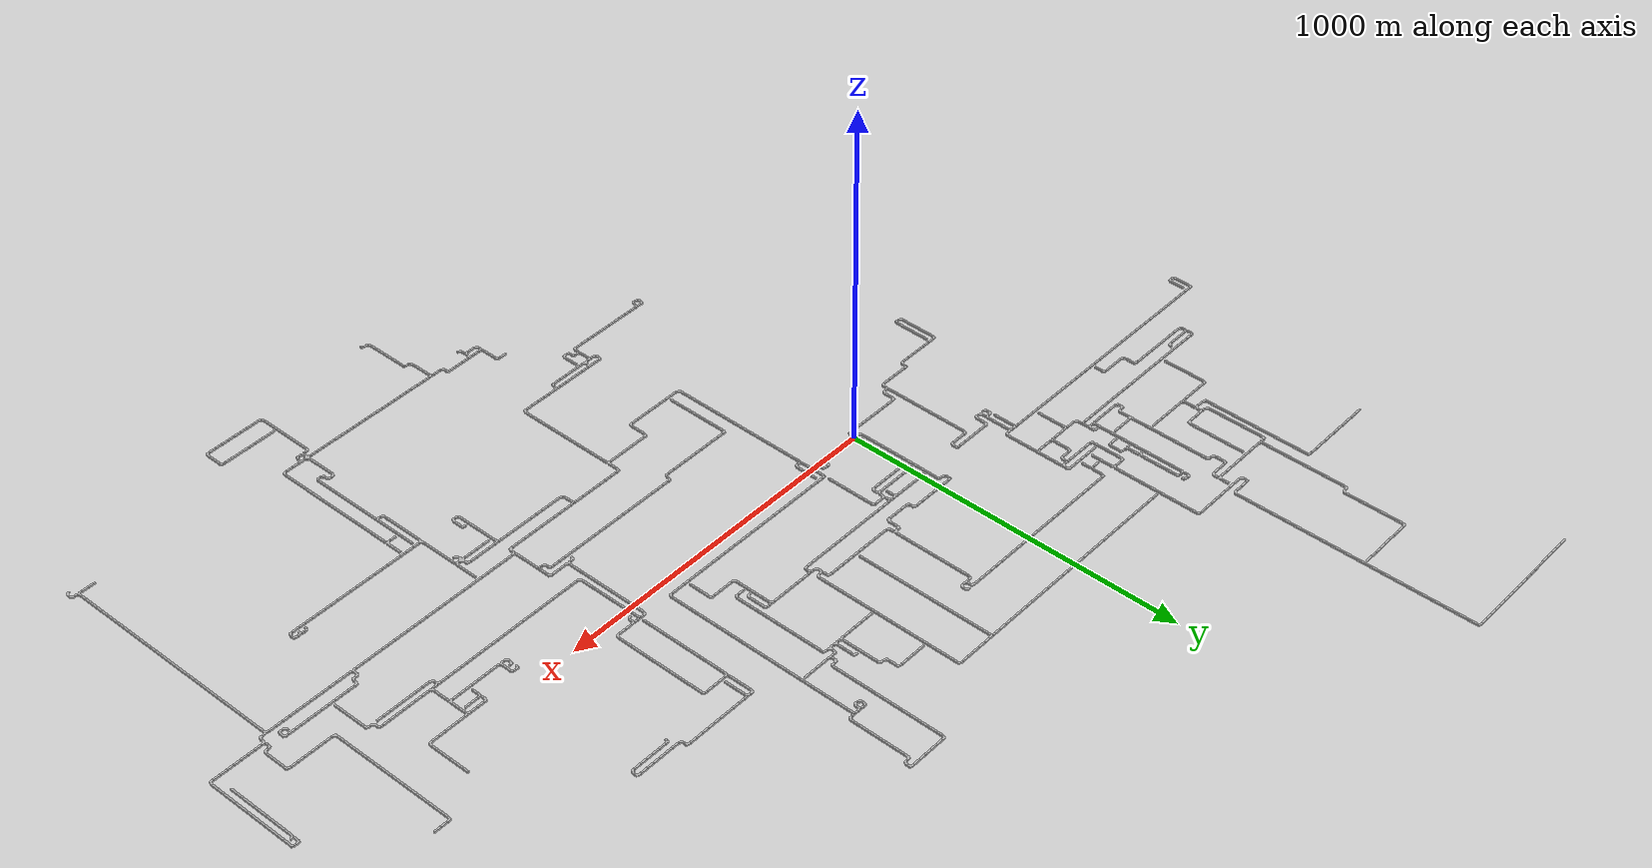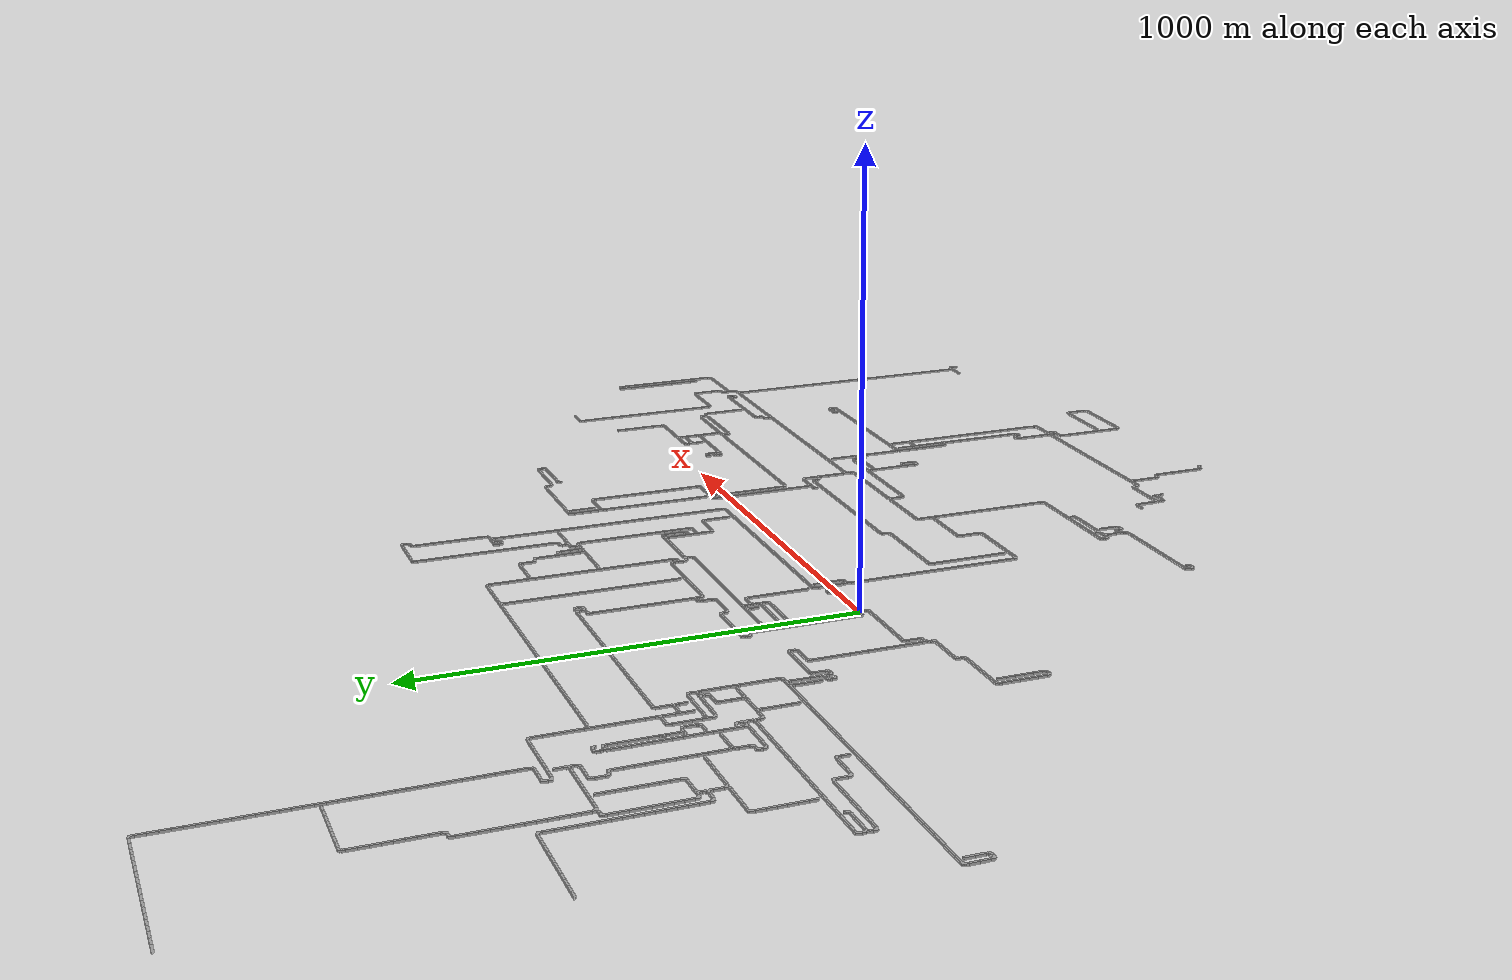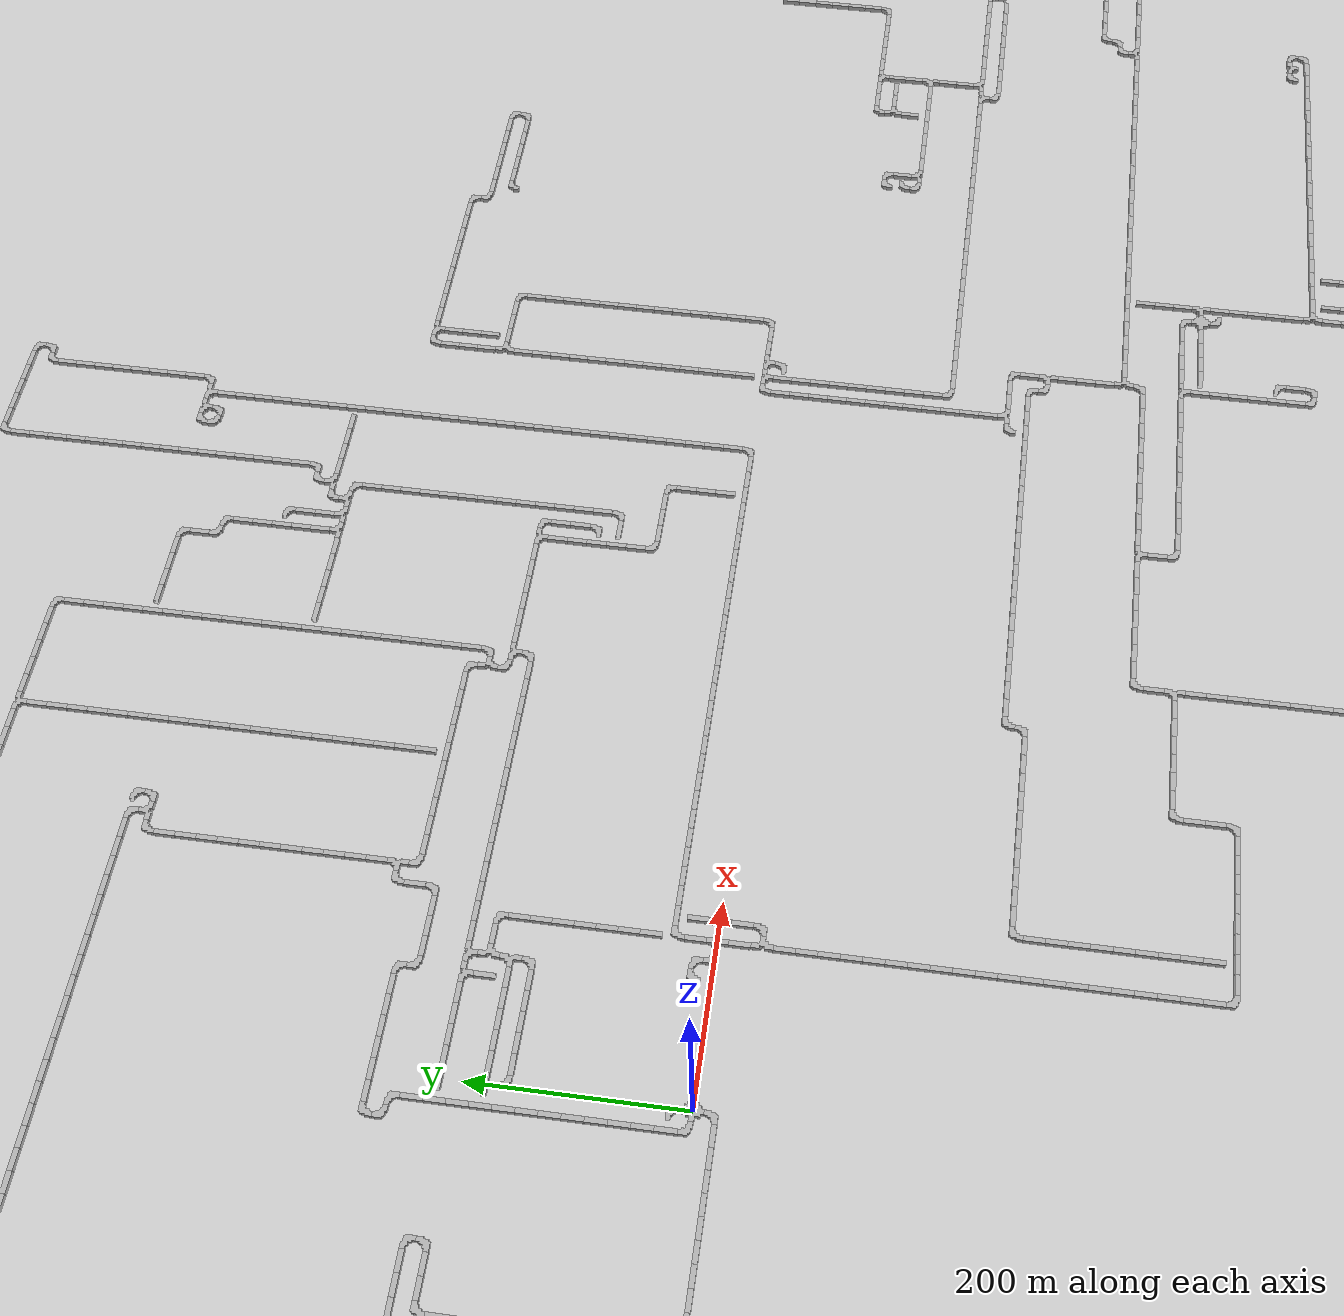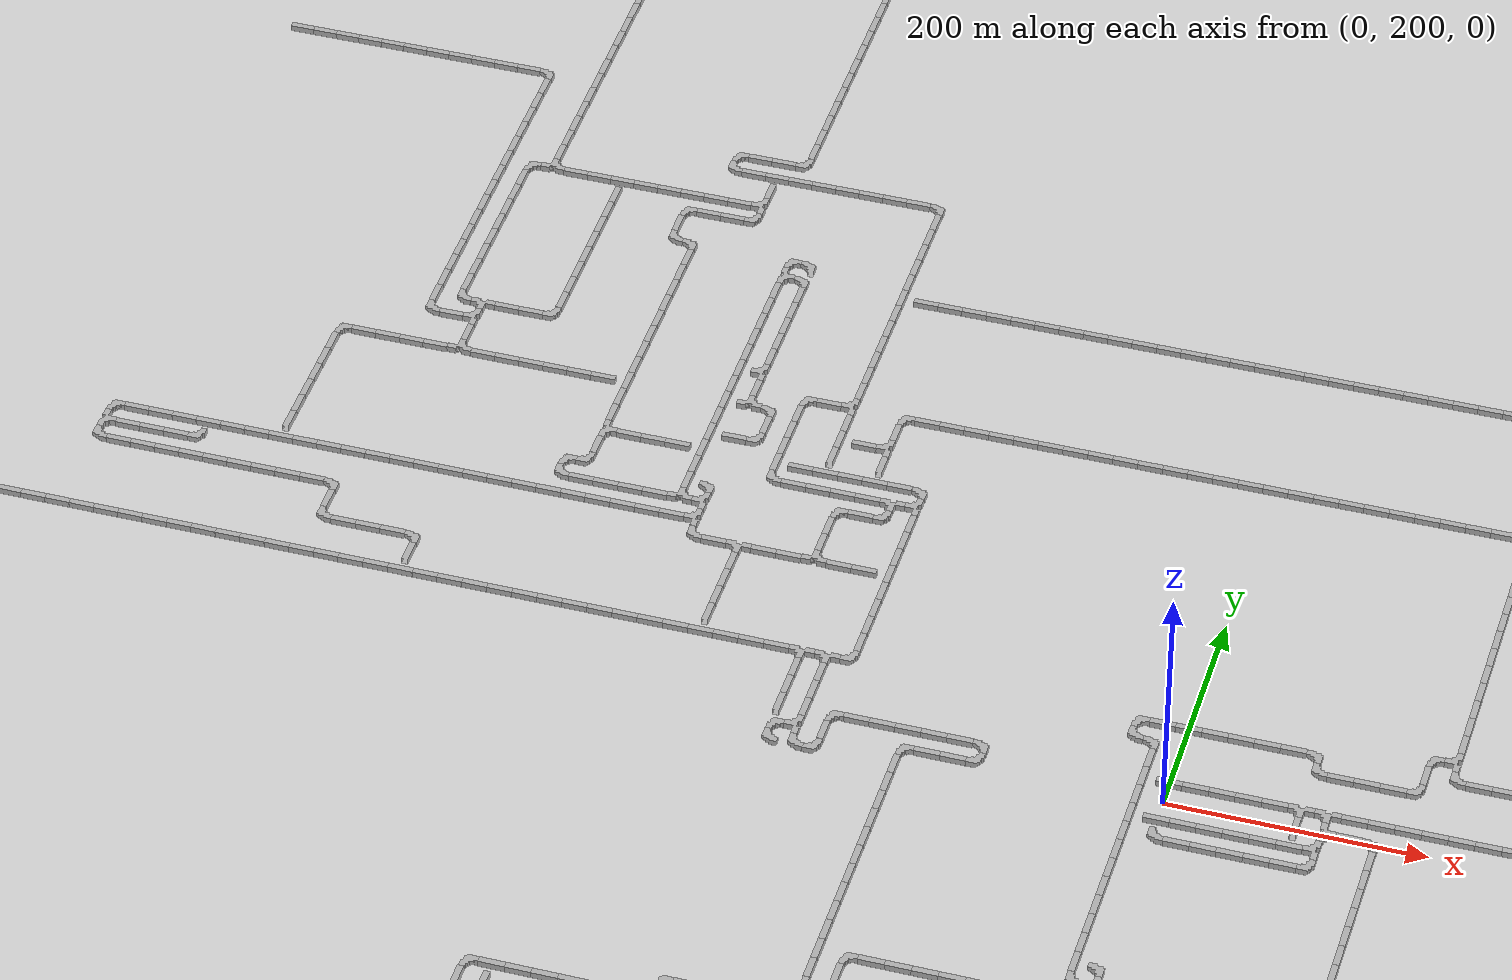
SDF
<sdf version="1.6">
 <world name="cave_32000_8">
  <include>
   <static>true</static>
   <name>cave_0_0</name>
   <pose>0 0 0 0 0 -1.5707963267948966</pose>
   <uri>model://cave_4way_20m</uri>
  </include>
  <include>
   <static>true</static>
   <name>cave_1_0</name>
   <pose>20 0 0 0 0 1.5707963267948966</pose>
   <uri>model://cave_straight_20m</uri>
  </include>
  <include>
   <static>true</static>
   <name>cave_2_0</name>
   <pose>40 0 0 0 0 1.5707963267948966</pose>
   <uri>model://cave_straight_20m</uri>
  </include>
  <include>
   <static>true</static>
   <name>cave_3_0</name>
   <pose>60 0 0 0 0 1.5707963267948966</pose>
   <uri>model://cave_straight_20m</uri>
  </include>
  <include>
   <static>true</static>
   <name>cave_4_0</name>
   <pose>80 0 0 0 0 1.5707963267948966</pose>
   <uri>model://cave_straight_20m</uri>
  </include>
  <include>
   <static>true</static>
   <name>cave_5_0</name>
   <pose>100 0 0 0 0 1.5707963267948966</pose>
   <uri>model://cave_straight_20m</uri>
  </include>
  <include>
   <static>true</static>
   <name>cave_6_0</name>
   <pose>120 0 0 0 0 1.5707963267948966</pose>
   <uri>model://cave_straight_20m</uri>
  </include>
  <include>
   <static>true</static>
   <name>cave_7_0</name>
   <pose>140 0 0 0 0 0.0</pose>
   <uri>model://cave_3way_20m</uri>
  </include>
  <include>
   <static>true</static>
   <name>cave_8_0</name>
   <pose>160 0 0 0 0 1.5707963267948966</pose>
   <uri>model://cave_3way_20m</uri>
  </include>
  <include>
   <static>true</static>
   <name>cave_8_-1</name>
   <pose>160 -20 0 0 0 0.0</pose>
   <uri>model://cave_straight_20m</uri>
  </include>
  <include>
   <static>true</static>
   <name>cave_8_-2</name>
   <pose>160 -40 0 0 0 -1.5707963267948966</pose>
   <uri>model://cave_3way_20m</uri>
  </include>
  <include>
   <static>true</static>
   <name>cave_9_-2</name>
   <pose>180 -40 0 0 0 1.5707963267948966</pose>
   <uri>model://cave_L_20m</uri>
  </include>
  <include>
   <static>true</static>
   <name>cave_9_-1</name>
   <pose>180 -20 0 0 0 0.0</pose>
   <uri>model://cave_straight_20m</uri>
  </include>
  <include>
   <static>true</static>
   <name>cave_9_0</name>
   <pose>180 0 0 0 0 0.0</pose>
   <uri>model://cave_straight_20m</uri>
  </include>
  <include>
   <static>true</static>
   <name>cave_9_1</name>
   <pose>180 20 0 0 0 0.0</pose>
   <uri>model://cave_straight_20m</uri>
  </include>
  <include>
   <static>true</static>
   <name>cave_8_-3</name>
   <pose>160 -60 0 0 0 0.0</pose>
   <uri>model://cave_straight_20m</uri>
  </include>
  <include>
   <static>true</static>
   <name>cave_8_-4</name>
   <pose>160 -80 0 0 0 0.0</pose>
   <uri>model://cave_straight_20m</uri>
  </include>
  <include>
   <static>true</static>
   <name>cave_8_-5</name>
   <pose>160 -100 0 0 0 0.0</pose>
   <uri>model://cave_straight_20m</uri>
  </include>
  <include>
   <static>true</static>
   <name>cave_8_-6</name>
   <pose>160 -120 0 0 0 0.0</pose>
   <uri>model://cave_straight_20m</uri>
  </include>
  <include>
   <static>true</static>
   <name>cave_8_-7</name>
   <pose>160 -140 0 0 0 0.0</pose>
   <uri>model://cave_straight_20m</uri>
  </include>
  <include>
   <static>true</static>
   <name>cave_8_-8</name>
   <pose>160 -160 0 0 0 0.0</pose>
   <uri>model://cave_straight_20m</uri>
  </include>
  <include>
   <static>true</static>
   <name>cave_8_-9</name>
   <pose>160 -180 0 0 0 0.0</pose>
   <uri>model://cave_straight_20m</uri>
  </include>
  <include>
   <static>true</static>
   <name>cave_8_-10</name>
   <pose>160 -200 0 0 0 0.0</pose>
   <uri>model://cave_straight_20m</uri>
  </include>
  <include>
   <static>true</static>
   <name>cave_8_-11</name>
   <pose>160 -220 0 0 0 0.0</pose>
   <uri>model://cave_straight_20m</uri>
  </include>
  <include>
   <static>true</static>
   <name>cave_8_-12</name>
   <pose>160 -240 0 0 0 0.0</pose>
   <uri>model://cave_straight_20m</uri>
  </include>
  <include>
   <static>true</static>
   <name>cave_8_-13</name>
   <pose>160 -260 0 0 0 0.0</pose>
   <uri>model://cave_straight_20m</uri>
  </include>
  <include>
   <static>true</static>
   <name>cave_8_-14</name>
   <pose>160 -280 0 0 0 0.0</pose>
   <uri>model://cave_straight_20m</uri>
  </include>
  <include>
   <static>true</static>
   <name>cave_8_-15</name>
   <pose>160 -300 0 0 0 0.0</pose>
   <uri>model://cave_straight_20m</uri>
  </include>
  <include>
   <static>true</static>
   <name>cave_8_-16</name>
   <pose>160 -320 0 0 0 0.0</pose>
   <uri>model://cave_straight_20m</uri>
  </include>
  <include>
   <static>true</static>
   <name>cave_8_-17</name>
   <pose>160 -340 0 0 0 0.0</pose>
   <uri>model://cave_straight_20m</uri>
  </include>
  <include>
   <static>true</static>
   <name>cave_8_-18</name>
   <pose>160 -360 0 0 0 0.0</pose>
   <uri>model://cave_straight_20m</uri>
  </include>
  <include>
   <static>true</static>
   <name>cave_8_-19</name>
   <pose>160 -380 0 0 0 0.0</pose>
   <uri>model://cave_straight_20m</uri>
  </include>
  <include>
   <static>true</static>
   <name>cave_8_-20</name>
   <pose>160 -400 0 0 0 0.0</pose>
   <uri>model://cave_straight_20m</uri>
  </include>
  <include>
   <static>true</static>
   <name>cave_8_-21</name>
   <pose>160 -420 0 0 0 0.0</pose>
   <uri>model://cave_straight_20m</uri>
  </include>
  <include>
   <static>true</static>
   <name>cave_8_-22</name>
   <pose>160 -440 0 0 0 0.0</pose>
   <uri>model://cave_straight_20m</uri>
  </include>
  <include>
   <static>true</static>
   <name>cave_8_-23</name>
   <pose>160 -460 0 0 0 0.0</pose>
   <uri>model://cave_L_20m</uri>
  </include>
  <include>
   <static>true</static>
   <name>cave_9_-23</name>
   <pose>180 -460 0 0 0 1.5707963267948966</pose>
   <uri>model://cave_straight_20m</uri>
  </include>
  <include>
   <static>true</static>
   <name>cave_10_-23</name>
   <pose>200 -460 0 0 0 1.5707963267948966</pose>
   <uri>model://cave_straight_20m</uri>
  </include>
  <include>
   <static>true</static>
   <name>cave_11_-23</name>
   <pose>220 -460 0 0 0 1.5707963267948966</pose>
   <uri>model://cave_straight_20m</uri>
  </include>
  <include>
   <static>true</static>
   <name>cave_12_-23</name>
   <pose>240 -460 0 0 0 1.5707963267948966</pose>
   <uri>model://cave_straight_20m</uri>
  </include>
  <include>
   <static>true</static>
   <name>cave_13_-23</name>
   <pose>260 -460 0 0 0 1.5707963267948966</pose>
   <uri>model://cave_straight_20m</uri>
  </include>
  <include>
   <static>true</static>
   <name>cave_14_-23</name>
   <pose>280 -460 0 0 0 1.5707963267948966</pose>
   <uri>model://cave_straight_20m</uri>
  </include>
  <include>
   <static>true</static>
   <name>cave_15_-23</name>
   <pose>300 -460 0 0 0 1.5707963267948966</pose>
   <uri>model://cave_straight_20m</uri>
  </include>
  <include>
   <static>true</static>
   <name>cave_16_-23</name>
   <pose>320 -460 0 0 0 1.5707963267948966</pose>
   <uri>model://cave_straight_20m</uri>
  </include>
  <include>
   <static>true</static>
   <name>cave_17_-23</name>
   <pose>340 -460 0 0 0 1.5707963267948966</pose>
   <uri>model://cave_L_20m</uri>
  </include>
  <include>
   <static>true</static>
   <name>cave_17_-22</name>
   <pose>340 -440 0 0 0 0.0</pose>
   <uri>model://cave_straight_20m</uri>
  </include>
  <include>
   <static>true</static>
   <name>cave_17_-21</name>
   <pose>340 -420 0 0 0 0.0</pose>
   <uri>model://cave_straight_20m</uri>
  </include>
  <include>
   <static>true</static>
   <name>cave_17_-20</name>
   <pose>340 -400 0 0 0 -1.5707963267948966</pose>
   <uri>model://cave_L_20m</uri>
  </include>
  <include>
   <static>true</static>
   <name>cave_18_-20</name>
   <pose>360 -400 0 0 0 1.5707963267948966</pose>
   <uri>model://cave_straight_20m</uri>
  </include>
  <include>
   <static>true</static>
   <name>cave_19_-20</name>
   <pose>380 -400 0 0 0 1.5707963267948966</pose>
   <uri>model://cave_straight_20m</uri>
  </include>
  <include>
   <static>true</static>
   <name>cave_20_-20</name>
   <pose>400 -400 0 0 0 1.5707963267948966</pose>
   <uri>model://cave_straight_20m</uri>
  </include>
  <include>
   <static>true</static>
   <name>cave_21_-20</name>
   <pose>420 -400 0 0 0 1.5707963267948966</pose>
   <uri>model://cave_straight_20m</uri>
  </include>
  <include>
   <static>true</static>
   <name>cave_22_-20</name>
   <pose>440 -400 0 0 0 1.5707963267948966</pose>
   <uri>model://cave_straight_20m</uri>
  </include>
  <include>
   <static>true</static>
   <name>cave_23_-20</name>
   <pose>460 -400 0 0 0 1.5707963267948966</pose>
   <uri>model://cave_straight_20m</uri>
  </include>
  <include>
   <static>true</static>
   <name>cave_24_-20</name>
   <pose>480 -400 0 0 0 1.5707963267948966</pose>
   <uri>model://cave_3way_20m</uri>
  </include>
  <include>
   <static>true</static>
   <name>cave_24_-21</name>
   <pose>480 -420 0 0 0 0.0</pose>
   <uri>model://cave_straight_20m</uri>
  </include>
  <include>
   <static>true</static>
   <name>cave_24_-22</name>
   <pose>480 -440 0 0 0 0.0</pose>
   <uri>model://cave_straight_20m</uri>
  </include>
  <include>
   <static>true</static>
   <name>cave_24_-23</name>
   <pose>480 -460 0 0 0 0.0</pose>
   <uri>model://cave_straight_20m</uri>
  </include>
  <include>
   <static>true</static>
   <name>cave_24_-24</name>
   <pose>480 -480 0 0 0 0.0</pose>
   <uri>model://cave_straight_20m</uri>
  </include>
  <include>
   <static>true</static>
   <name>cave_24_-25</name>
   <pose>480 -500 0 0 0 0.0</pose>
   <uri>model://cave_straight_20m</uri>
  </include>
  <include>
   <static>true</static>
   <name>cave_24_-26</name>
   <pose>480 -520 0 0 0 0.0</pose>
   <uri>model://cave_straight_20m</uri>
  </include>
  <include>
   <static>true</static>
   <name>cave_24_-27</name>
   <pose>480 -540 0 0 0 0.0</pose>
   <uri>model://cave_straight_20m</uri>
  </include>
  <include>
   <static>true</static>
   <name>cave_24_-28</name>
   <pose>480 -560 0 0 0 0.0</pose>
   <uri>model://cave_straight_20m</uri>
  </include>
  <include>
   <static>true</static>
   <name>cave_24_-29</name>
   <pose>480 -580 0 0 0 0.0</pose>
   <uri>model://cave_straight_20m</uri>
  </include>
  <include>
   <static>true</static>
   <name>cave_24_-30</name>
   <pose>480 -600 0 0 0 0.0</pose>
   <uri>model://cave_straight_20m</uri>
  </include>
  <include>
   <static>true</static>
   <name>cave_24_-31</name>
   <pose>480 -620 0 0 0 0.0</pose>
   <uri>model://cave_straight_20m</uri>
  </include>
  <include>
   <static>true</static>
   <name>cave_24_-32</name>
   <pose>480 -640 0 0 0 0.0</pose>
   <uri>model://cave_straight_20m</uri>
  </include>
  <include>
   <static>true</static>
   <name>cave_24_-33</name>
   <pose>480 -660 0 0 0 0.0</pose>
   <uri>model://cave_straight_20m</uri>
  </include>
  <include>
   <static>true</static>
   <name>cave_24_-34</name>
   <pose>480 -680 0 0 0 0.0</pose>
   <uri>model://cave_straight_20m</uri>
  </include>
  <include>
   <static>true</static>
   <name>cave_24_-35</name>
   <pose>480 -700 0 0 0 1.5707963267948966</pose>
   <uri>model://cave_L_20m</uri>
  </include>
  <include>
   <static>true</static>
   <name>cave_23_-35</name>
   <pose>460 -700 0 0 0 1.5707963267948966</pose>
   <uri>model://cave_straight_20m</uri>
  </include>
  <include>
   <static>true</static>
   <name>cave_22_-35</name>
   <pose>440 -700 0 0 0 1.5707963267948966</pose>
   <uri>model://cave_straight_20m</uri>
  </include>
  <include>
   <static>true</static>
   <name>cave_21_-35</name>
   <pose>420 -700 0 0 0 1.5707963267948966</pose>
   <uri>model://cave_straight_20m</uri>
  </include>
  <include>
   <static>true</static>
   <name>cave_20_-35</name>
   <pose>400 -700 0 0 0 1.5707963267948966</pose>
   <uri>model://cave_straight_20m</uri>
  </include>
  <include>
   <static>true</static>
   <name>cave_19_-35</name>
   <pose>380 -700 0 0 0 1.5707963267948966</pose>
   <uri>model://cave_straight_20m</uri>
  </include>
  <include>
   <static>true</static>
   <name>cave_18_-35</name>
   <pose>360 -700 0 0 0 1.5707963267948966</pose>
   <uri>model://cave_straight_20m</uri>
  </include>
  <include>
   <static>true</static>
   <name>cave_17_-35</name>
   <pose>340 -700 0 0 0 1.5707963267948966</pose>
   <uri>model://cave_straight_20m</uri>
  </include>
  <include>
   <static>true</static>
   <name>cave_16_-35</name>
   <pose>320 -700 0 0 0 1.5707963267948966</pose>
   <uri>model://cave_straight_20m</uri>
  </include>
  <include>
   <static>true</static>
   <name>cave_15_-35</name>
   <pose>300 -700 0 0 0 1.5707963267948966</pose>
   <uri>model://cave_straight_20m</uri>
  </include>
  <include>
   <static>true</static>
   <name>cave_14_-35</name>
   <pose>280 -700 0 0 0 1.5707963267948966</pose>
   <uri>model://cave_straight_20m</uri>
  </include>
  <include>
   <static>true</static>
   <name>cave_13_-35</name>
   <pose>260 -700 0 0 0 1.5707963267948966</pose>
   <uri>model://cave_straight_20m</uri>
  </include>
  <include>
   <static>true</static>
   <name>cave_12_-35</name>
   <pose>240 -700 0 0 0 1.5707963267948966</pose>
   <uri>model://cave_straight_20m</uri>
  </include>
  <include>
   <static>true</static>
   <name>cave_11_-35</name>
   <pose>220 -700 0 0 0 1.5707963267948966</pose>
   <uri>model://cave_straight_20m</uri>
  </include>
  <include>
   <static>true</static>
   <name>cave_10_-35</name>
   <pose>200 -700 0 0 0 -1.5707963267948966</pose>
   <uri>model://cave_L_20m</uri>
  </include>
  <include>
   <static>true</static>
   <name>cave_10_-36</name>
   <pose>200 -720 0 0 0 0.0</pose>
   <uri>model://cave_L_20m</uri>
  </include>
  <include>
   <static>true</static>
   <name>cave_11_-36</name>
   <pose>220 -720 0 0 0 3.141592653589793</pose>
   <uri>model://cave_3way_20m</uri>
  </include>
  <include>
   <static>true</static>
   <name>cave_12_-36</name>
   <pose>240 -720 0 0 0 0.0</pose>
   <uri>model://cave_3way_20m</uri>
  </include>
  <include>
   <static>true</static>
   <name>cave_13_-36</name>
   <pose>260 -720 0 0 0 1.5707963267948966</pose>
   <uri>model://cave_straight_20m</uri>
  </include>
  <include>
   <static>true</static>
   <name>cave_14_-36</name>
   <pose>280 -720 0 0 0 1.5707963267948966</pose>
   <uri>model://cave_straight_20m</uri>
  </include>
  <include>
   <static>true</static>
   <name>cave_15_-36</name>
   <pose>300 -720 0 0 0 1.5707963267948966</pose>
   <uri>model://cave_straight_20m</uri>
  </include>
  <include>
   <static>true</static>
   <name>cave_16_-36</name>
   <pose>320 -720 0 0 0 1.5707963267948966</pose>
   <uri>model://cave_straight_20m</uri>
  </include>
  <include>
   <static>true</static>
   <name>cave_17_-36</name>
   <pose>340 -720 0 0 0 1.5707963267948966</pose>
   <uri>model://cave_straight_20m</uri>
  </include>
  <include>
   <static>true</static>
   <name>cave_18_-36</name>
   <pose>360 -720 0 0 0 1.5707963267948966</pose>
   <uri>model://cave_L_20m</uri>
  </include>
  <include>
   <static>true</static>
   <name>cave_11_-37</name>
   <pose>220 -740 0 0 0 0.0</pose>
   <uri>model://cave_straight_20m</uri>
  </include>
  <include>
   <static>true</static>
   <name>cave_11_-38</name>
   <pose>220 -760 0 0 0 -1.5707963267948966</pose>
   <uri>model://cave_3way_20m</uri>
  </include>
  <include>
   <static>true</static>
   <name>cave_12_-38</name>
   <pose>240 -760 0 0 0 3.141592653589793</pose>
   <uri>model://cave_L_20m</uri>
  </include>
  <include>
   <static>true</static>
   <name>cave_12_-39</name>
   <pose>240 -780 0 0 0 0.0</pose>
   <uri>model://cave_L_20m</uri>
  </include>
  <include>
   <static>true</static>
   <name>cave_13_-39</name>
   <pose>260 -780 0 0 0 1.5707963267948966</pose>
   <uri>model://cave_L_20m</uri>
  </include>
  <include>
   <static>true</static>
   <name>cave_13_-38</name>
   <pose>260 -760 0 0 0 0.0</pose>
   <uri>model://cave_straight_20m</uri>
  </include>
  <include>
   <static>true</static>
   <name>cave_13_-37</name>
   <pose>260 -740 0 0 0 0.0</pose>
   <uri>model://cave_straight_20m</uri>
  </include>
  <include>
   <static>true</static>
   <name>cave_11_-39</name>
   <pose>220 -780 0 0 0 1.5707963267948966</pose>
   <uri>model://cave_L_20m</uri>
  </include>
  <include>
   <static>true</static>
   <name>cave_10_-39</name>
   <pose>200 -780 0 0 0 1.5707963267948966</pose>
   <uri>model://cave_straight_20m</uri>
  </include>
  <include>
   <static>true</static>
   <name>cave_9_-39</name>
   <pose>180 -780 0 0 0 1.5707963267948966</pose>
   <uri>model://cave_straight_20m</uri>
  </include>
  <include>
   <static>true</static>
   <name>cave_8_-39</name>
   <pose>160 -780 0 0 0 1.5707963267948966</pose>
   <uri>model://cave_straight_20m</uri>
  </include>
  <include>
   <static>true</static>
   <name>cave_7_-39</name>
   <pose>140 -780 0 0 0 1.5707963267948966</pose>
   <uri>model://cave_straight_20m</uri>
  </include>
  <include>
   <static>true</static>
   <name>cave_6_-39</name>
   <pose>120 -780 0 0 0 1.5707963267948966</pose>
   <uri>model://cave_straight_20m</uri>
  </include>
  <include>
   <static>true</static>
   <name>cave_5_-39</name>
   <pose>100 -780 0 0 0 1.5707963267948966</pose>
   <uri>model://cave_straight_20m</uri>
  </include>
  <include>
   <static>true</static>
   <name>cave_4_-39</name>
   <pose>80 -780 0 0 0 1.5707963267948966</pose>
   <uri>model://cave_straight_20m</uri>
  </include>
  <include>
   <static>true</static>
   <name>cave_3_-39</name>
   <pose>60 -780 0 0 0 1.5707963267948966</pose>
   <uri>model://cave_straight_20m</uri>
  </include>
  <include>
   <static>true</static>
   <name>cave_2_-39</name>
   <pose>40 -780 0 0 0 1.5707963267948966</pose>
   <uri>model://cave_straight_20m</uri>
  </include>
  <include>
   <static>true</static>
   <name>cave_1_-39</name>
   <pose>20 -780 0 0 0 1.5707963267948966</pose>
   <uri>model://cave_straight_20m</uri>
  </include>
  <include>
   <static>true</static>
   <name>cave_0_-39</name>
   <pose>0 -780 0 0 0 1.5707963267948966</pose>
   <uri>model://cave_straight_20m</uri>
  </include>
  <include>
   <static>true</static>
   <name>cave_-1_-39</name>
   <pose>-20 -780 0 0 0 1.5707963267948966</pose>
   <uri>model://cave_straight_20m</uri>
  </include>
  <include>
   <static>true</static>
   <name>cave_-2_-39</name>
   <pose>-40 -780 0 0 0 -1.5707963267948966</pose>
   <uri>model://cave_L_20m</uri>
  </include>
  <include>
   <static>true</static>
   <name>cave_-2_-40</name>
   <pose>-40 -800 0 0 0 0.0</pose>
   <uri>model://cave_L_20m</uri>
  </include>
  <include>
   <static>true</static>
   <name>cave_-1_-40</name>
   <pose>-20 -800 0 0 0 1.5707963267948966</pose>
   <uri>model://cave_L_20m</uri>
  </include>
  <include>
   <static>true</static>
   <name>cave_24_-19</name>
   <pose>480 -380 0 0 0 0.0</pose>
   <uri>model://cave_straight_20m</uri>
  </include>
  <include>
   <static>true</static>
   <name>cave_24_-18</name>
   <pose>480 -360 0 0 0 -1.5707963267948966</pose>
   <uri>model://cave_L_20m</uri>
  </include>
  <include>
   <static>true</static>
   <name>cave_25_-18</name>
   <pose>500 -360 0 0 0 1.5707963267948966</pose>
   <uri>model://cave_straight_20m</uri>
  </include>
  <include>
   <static>true</static>
   <name>cave_26_-18</name>
   <pose>520 -360 0 0 0 1.5707963267948966</pose>
   <uri>model://cave_straight_20m</uri>
  </include>
  <include>
   <static>true</static>
   <name>cave_27_-18</name>
   <pose>540 -360 0 0 0 1.5707963267948966</pose>
   <uri>model://cave_straight_20m</uri>
  </include>
  <include>
   <static>true</static>
   <name>cave_28_-18</name>
   <pose>560 -360 0 0 0 1.5707963267948966</pose>
   <uri>model://cave_straight_20m</uri>
  </include>
  <include>
   <static>true</static>
   <name>cave_29_-18</name>
   <pose>580 -360 0 0 0 1.5707963267948966</pose>
   <uri>model://cave_straight_20m</uri>
  </include>
  <include>
   <static>true</static>
   <name>cave_30_-18</name>
   <pose>600 -360 0 0 0 1.5707963267948966</pose>
   <uri>model://cave_straight_20m</uri>
  </include>
  <include>
   <static>true</static>
   <name>cave_31_-18</name>
   <pose>620 -360 0 0 0 1.5707963267948966</pose>
   <uri>model://cave_straight_20m</uri>
  </include>
  <include>
   <static>true</static>
   <name>cave_32_-18</name>
   <pose>640 -360 0 0 0 3.141592653589793</pose>
   <uri>model://cave_3way_20m</uri>
  </include>
  <include>
   <static>true</static>
   <name>cave_33_-18</name>
   <pose>660 -360 0 0 0 1.5707963267948966</pose>
   <uri>model://cave_straight_20m</uri>
  </include>
  <include>
   <static>true</static>
   <name>cave_34_-18</name>
   <pose>680 -360 0 0 0 1.5707963267948966</pose>
   <uri>model://cave_straight_20m</uri>
  </include>
  <include>
   <static>true</static>
   <name>cave_35_-18</name>
   <pose>700 -360 0 0 0 1.5707963267948966</pose>
   <uri>model://cave_straight_20m</uri>
  </include>
  <include>
   <static>true</static>
   <name>cave_36_-18</name>
   <pose>720 -360 0 0 0 1.5707963267948966</pose>
   <uri>model://cave_straight_20m</uri>
  </include>
  <include>
   <static>true</static>
   <name>cave_37_-18</name>
   <pose>740 -360 0 0 0 1.5707963267948966</pose>
   <uri>model://cave_straight_20m</uri>
  </include>
  <include>
   <static>true</static>
   <name>cave_38_-18</name>
   <pose>760 -360 0 0 0 1.5707963267948966</pose>
   <uri>model://cave_straight_20m</uri>
  </include>
  <include>
   <static>true</static>
   <name>cave_39_-18</name>
   <pose>780 -360 0 0 0 1.5707963267948966</pose>
   <uri>model://cave_straight_20m</uri>
  </include>
  <include>
   <static>true</static>
   <name>cave_40_-18</name>
   <pose>800 -360 0 0 0 1.5707963267948966</pose>
   <uri>model://cave_straight_20m</uri>
  </include>
  <include>
   <static>true</static>
   <name>cave_41_-18</name>
   <pose>820 -360 0 0 0 1.5707963267948966</pose>
   <uri>model://cave_straight_20m</uri>
  </include>
  <include>
   <static>true</static>
   <name>cave_42_-18</name>
   <pose>840 -360 0 0 0 1.5707963267948966</pose>
   <uri>model://cave_straight_20m</uri>
  </include>
  <include>
   <static>true</static>
   <name>cave_43_-18</name>
   <pose>860 -360 0 0 0 1.5707963267948966</pose>
   <uri>model://cave_L_20m</uri>
  </include>
  <include>
   <static>true</static>
   <name>cave_43_-17</name>
   <pose>860 -340 0 0 0 -1.5707963267948966</pose>
   <uri>model://cave_3way_20m</uri>
  </include>
  <include>
   <static>true</static>
   <name>cave_44_-17</name>
   <pose>880 -340 0 0 0 1.5707963267948966</pose>
   <uri>model://cave_straight_20m</uri>
  </include>
  <include>
   <static>true</static>
   <name>cave_45_-17</name>
   <pose>900 -340 0 0 0 1.5707963267948966</pose>
   <uri>model://cave_straight_20m</uri>
  </include>
  <include>
   <static>true</static>
   <name>cave_46_-17</name>
   <pose>920 -340 0 0 0 1.5707963267948966</pose>
   <uri>model://cave_straight_20m</uri>
  </include>
  <include>
   <static>true</static>
   <name>cave_47_-17</name>
   <pose>940 -340 0 0 0 1.5707963267948966</pose>
   <uri>model://cave_straight_20m</uri>
  </include>
  <include>
   <static>true</static>
   <name>cave_48_-17</name>
   <pose>960 -340 0 0 0 1.5707963267948966</pose>
   <uri>model://cave_straight_20m</uri>
  </include>
  <include>
   <static>true</static>
   <name>cave_49_-17</name>
   <pose>980 -340 0 0 0 1.5707963267948966</pose>
   <uri>model://cave_straight_20m</uri>
  </include>
  <include>
   <static>true</static>
   <name>cave_50_-17</name>
   <pose>1000 -340 0 0 0 1.5707963267948966</pose>
   <uri>model://cave_straight_20m</uri>
  </include>
  <include>
   <static>true</static>
   <name>cave_51_-17</name>
   <pose>1020 -340 0 0 0 1.5707963267948966</pose>
   <uri>model://cave_straight_20m</uri>
  </include>
  <include>
   <static>true</static>
   <name>cave_52_-17</name>
   <pose>1040 -340 0 0 0 1.5707963267948966</pose>
   <uri>model://cave_straight_20m</uri>
  </include>
  <include>
   <static>true</static>
   <name>cave_53_-17</name>
   <pose>1060 -340 0 0 0 1.5707963267948966</pose>
   <uri>model://cave_straight_20m</uri>
  </include>
  <include>
   <static>true</static>
   <name>cave_54_-17</name>
   <pose>1080 -340 0 0 0 1.5707963267948966</pose>
   <uri>model://cave_straight_20m</uri>
  </include>
  <include>
   <static>true</static>
   <name>cave_55_-17</name>
   <pose>1100 -340 0 0 0 1.5707963267948966</pose>
   <uri>model://cave_straight_20m</uri>
  </include>
  <include>
   <static>true</static>
   <name>cave_56_-17</name>
   <pose>1120 -340 0 0 0 1.5707963267948966</pose>
   <uri>model://cave_straight_20m</uri>
  </include>
  <include>
   <static>true</static>
   <name>cave_57_-17</name>
   <pose>1140 -340 0 0 0 1.5707963267948966</pose>
   <uri>model://cave_straight_20m</uri>
  </include>
  <include>
   <static>true</static>
   <name>cave_58_-17</name>
   <pose>1160 -340 0 0 0 1.5707963267948966</pose>
   <uri>model://cave_straight_20m</uri>
  </include>
  <include>
   <static>true</static>
   <name>cave_59_-17</name>
   <pose>1180 -340 0 0 0 1.5707963267948966</pose>
   <uri>model://cave_straight_20m</uri>
  </include>
  <include>
   <static>true</static>
   <name>cave_60_-17</name>
   <pose>1200 -340 0 0 0 1.5707963267948966</pose>
   <uri>model://cave_straight_20m</uri>
  </include>
  <include>
   <static>true</static>
   <name>cave_61_-17</name>
   <pose>1220 -340 0 0 0 1.5707963267948966</pose>
   <uri>model://cave_straight_20m</uri>
  </include>
  <include>
   <static>true</static>
   <name>cave_62_-17</name>
   <pose>1240 -340 0 0 0 1.5707963267948966</pose>
   <uri>model://cave_straight_20m</uri>
  </include>
  <include>
   <static>true</static>
   <name>cave_63_-17</name>
   <pose>1260 -340 0 0 0 1.5707963267948966</pose>
   <uri>model://cave_straight_20m</uri>
  </include>
  <include>
   <static>true</static>
   <name>cave_64_-17</name>
   <pose>1280 -340 0 0 0 1.5707963267948966</pose>
   <uri>model://cave_straight_20m</uri>
  </include>
  <include>
   <static>true</static>
   <name>cave_65_-17</name>
   <pose>1300 -340 0 0 0 1.5707963267948966</pose>
   <uri>model://cave_straight_20m</uri>
  </include>
  <include>
   <static>true</static>
   <name>cave_66_-17</name>
   <pose>1320 -340 0 0 0 1.5707963267948966</pose>
   <uri>model://cave_straight_20m</uri>
  </include>
  <include>
   <static>true</static>
   <name>cave_67_-17</name>
   <pose>1340 -340 0 0 0 1.5707963267948966</pose>
   <uri>model://cave_straight_20m</uri>
  </include>
  <include>
   <static>true</static>
   <name>cave_68_-17</name>
   <pose>1360 -340 0 0 0 1.5707963267948966</pose>
   <uri>model://cave_straight_20m</uri>
  </include>
  <include>
   <static>true</static>
   <name>cave_69_-17</name>
   <pose>1380 -340 0 0 0 0.0</pose>
   <uri>model://cave_3way_20m</uri>
  </include>
  <include>
   <static>true</static>
   <name>cave_70_-17</name>
   <pose>1400 -340 0 0 0 1.5707963267948966</pose>
   <uri>model://cave_straight_20m</uri>
  </include>
  <include>
   <static>true</static>
   <name>cave_71_-17</name>
   <pose>1420 -340 0 0 0 1.5707963267948966</pose>
   <uri>model://cave_straight_20m</uri>
  </include>
  <include>
   <static>true</static>
   <name>cave_72_-17</name>
   <pose>1440 -340 0 0 0 1.5707963267948966</pose>
   <uri>model://cave_straight_20m</uri>
  </include>
  <include>
   <static>true</static>
   <name>cave_73_-17</name>
   <pose>1460 -340 0 0 0 1.5707963267948966</pose>
   <uri>model://cave_straight_20m</uri>
  </include>
  <include>
   <static>true</static>
   <name>cave_74_-17</name>
   <pose>1480 -340 0 0 0 1.5707963267948966</pose>
   <uri>model://cave_straight_20m</uri>
  </include>
  <include>
   <static>true</static>
   <name>cave_75_-17</name>
   <pose>1500 -340 0 0 0 1.5707963267948966</pose>
   <uri>model://cave_straight_20m</uri>
  </include>
  <include>
   <static>true</static>
   <name>cave_76_-17</name>
   <pose>1520 -340 0 0 0 1.5707963267948966</pose>
   <uri>model://cave_straight_20m</uri>
  </include>
  <include>
   <static>true</static>
   <name>cave_77_-17</name>
   <pose>1540 -340 0 0 0 1.5707963267948966</pose>
   <uri>model://cave_straight_20m</uri>
  </include>
  <include>
   <static>true</static>
   <name>cave_78_-17</name>
   <pose>1560 -340 0 0 0 1.5707963267948966</pose>
   <uri>model://cave_straight_20m</uri>
  </include>
  <include>
   <static>true</static>
   <name>cave_79_-17</name>
   <pose>1580 -340 0 0 0 1.5707963267948966</pose>
   <uri>model://cave_straight_20m</uri>
  </include>
  <include>
   <static>true</static>
   <name>cave_80_-17</name>
   <pose>1600 -340 0 0 0 1.5707963267948966</pose>
   <uri>model://cave_straight_20m</uri>
  </include>
  <include>
   <static>true</static>
   <name>cave_81_-17</name>
   <pose>1620 -340 0 0 0 1.5707963267948966</pose>
   <uri>model://cave_straight_20m</uri>
  </include>
  <include>
   <static>true</static>
   <name>cave_82_-17</name>
   <pose>1640 -340 0 0 0 3.141592653589793</pose>
   <uri>model://cave_3way_20m</uri>
  </include>
  <include>
   <static>true</static>
   <name>cave_83_-17</name>
   <pose>1660 -340 0 0 0 1.5707963267948966</pose>
   <uri>model://cave_L_20m</uri>
  </include>
  <include>
   <static>true</static>
   <name>cave_83_-16</name>
   <pose>1660 -320 0 0 0 -1.5707963267948966</pose>
   <uri>model://cave_3way_20m</uri>
  </include>
  <include>
   <static>true</static>
   <name>cave_84_-16</name>
   <pose>1680 -320 0 0 0 1.5707963267948966</pose>
   <uri>model://cave_straight_20m</uri>
  </include>
  <include>
   <static>true</static>
   <name>cave_85_-16</name>
   <pose>1700 -320 0 0 0 1.5707963267948966</pose>
   <uri>model://cave_straight_20m</uri>
  </include>
  <include>
   <static>true</static>
   <name>cave_86_-16</name>
   <pose>1720 -320 0 0 0 1.5707963267948966</pose>
   <uri>model://cave_straight_20m</uri>
  </include>
  <include>
   <static>true</static>
   <name>cave_87_-16</name>
   <pose>1740 -320 0 0 0 1.5707963267948966</pose>
   <uri>model://cave_straight_20m</uri>
  </include>
  <include>
   <static>true</static>
   <name>cave_88_-16</name>
   <pose>1760 -320 0 0 0 1.5707963267948966</pose>
   <uri>model://cave_straight_20m</uri>
  </include>
  <include>
   <static>true</static>
   <name>cave_89_-16</name>
   <pose>1780 -320 0 0 0 1.5707963267948966</pose>
   <uri>model://cave_straight_20m</uri>
  </include>
  <include>
   <static>true</static>
   <name>cave_90_-16</name>
   <pose>1800 -320 0 0 0 1.5707963267948966</pose>
   <uri>model://cave_straight_20m</uri>
  </include>
  <include>
   <static>true</static>
   <name>cave_91_-16</name>
   <pose>1820 -320 0 0 0 1.5707963267948966</pose>
   <uri>model://cave_L_20m</uri>
  </include>
  <include>
   <static>true</static>
   <name>cave_91_-15</name>
   <pose>1820 -300 0 0 0 0.0</pose>
   <uri>model://cave_straight_20m</uri>
  </include>
  <include>
   <static>true</static>
   <name>cave_91_-14</name>
   <pose>1820 -280 0 0 0 0.0</pose>
   <uri>model://cave_straight_20m</uri>
  </include>
  <include>
   <static>true</static>
   <name>cave_91_-13</name>
   <pose>1820 -260 0 0 0 0.0</pose>
   <uri>model://cave_straight_20m</uri>
  </include>
  <include>
   <static>true</static>
   <name>cave_91_-12</name>
   <pose>1820 -240 0 0 0 0.0</pose>
   <uri>model://cave_straight_20m</uri>
  </include>
  <include>
   <static>true</static>
   <name>cave_91_-11</name>
   <pose>1820 -220 0 0 0 0.0</pose>
   <uri>model://cave_straight_20m</uri>
  </include>
  <include>
   <static>true</static>
   <name>cave_91_-10</name>
   <pose>1820 -200 0 0 0 0.0</pose>
   <uri>model://cave_straight_20m</uri>
  </include>
  <include>
   <static>true</static>
   <name>cave_91_-9</name>
   <pose>1820 -180 0 0 0 0.0</pose>
   <uri>model://cave_straight_20m</uri>
  </include>
  <include>
   <static>true</static>
   <name>cave_91_-8</name>
   <pose>1820 -160 0 0 0 0.0</pose>
   <uri>model://cave_straight_20m</uri>
  </include>
  <include>
   <static>true</static>
   <name>cave_91_-7</name>
   <pose>1820 -140 0 0 0 0.0</pose>
   <uri>model://cave_straight_20m</uri>
  </include>
  <include>
   <static>true</static>
   <name>cave_91_-6</name>
   <pose>1820 -120 0 0 0 0.0</pose>
   <uri>model://cave_straight_20m</uri>
  </include>
  <include>
   <static>true</static>
   <name>cave_91_-5</name>
   <pose>1820 -100 0 0 0 0.0</pose>
   <uri>model://cave_straight_20m</uri>
  </include>
  <include>
   <static>true</static>
   <name>cave_91_-4</name>
   <pose>1820 -80 0 0 0 0.0</pose>
   <uri>model://cave_straight_20m</uri>
  </include>
  <include>
   <static>true</static>
   <name>cave_91_-3</name>
   <pose>1820 -60 0 0 0 0.0</pose>
   <uri>model://cave_straight_20m</uri>
  </include>
  <include>
   <static>true</static>
   <name>cave_91_-2</name>
   <pose>1820 -40 0 0 0 3.141592653589793</pose>
   <uri>model://cave_L_20m</uri>
  </include>
  <include>
   <static>true</static>
   <name>cave_90_-2</name>
   <pose>1800 -40 0 0 0 -1.5707963267948966</pose>
   <uri>model://cave_L_20m</uri>
  </include>
  <include>
   <static>true</static>
   <name>cave_90_-3</name>
   <pose>1800 -60 0 0 0 -1.5707963267948966</pose>
   <uri>model://cave_3way_20m</uri>
  </include>
  <include>
   <static>true</static>
   <name>cave_90_-4</name>
   <pose>1800 -80 0 0 0 0.0</pose>
   <uri>model://cave_straight_20m</uri>
  </include>
  <include>
   <static>true</static>
   <name>cave_90_-5</name>
   <pose>1800 -100 0 0 0 0.0</pose>
   <uri>model://cave_straight_20m</uri>
  </include>
  <include>
   <static>true</static>
   <name>cave_90_-6</name>
   <pose>1800 -120 0 0 0 0.0</pose>
   <uri>model://cave_straight_20m</uri>
  </include>
  <include>
   <static>true</static>
   <name>cave_90_-7</name>
   <pose>1800 -140 0 0 0 0.0</pose>
   <uri>model://cave_straight_20m</uri>
  </include>
  <include>
   <static>true</static>
   <name>cave_90_-8</name>
   <pose>1800 -160 0 0 0 0.0</pose>
   <uri>model://cave_straight_20m</uri>
  </include>
  <include>
   <static>true</static>
   <name>cave_90_-9</name>
   <pose>1800 -180 0 0 0 0.0</pose>
   <uri>model://cave_straight_20m</uri>
  </include>
  <include>
   <static>true</static>
   <name>cave_90_-10</name>
   <pose>1800 -200 0 0 0 0.0</pose>
   <uri>model://cave_straight_20m</uri>
  </include>
  <include>
   <static>true</static>
   <name>cave_90_-11</name>
   <pose>1800 -220 0 0 0 0.0</pose>
   <uri>model://cave_straight_20m</uri>
  </include>
  <include>
   <static>true</static>
   <name>cave_90_-12</name>
   <pose>1800 -240 0 0 0 0.0</pose>
   <uri>model://cave_straight_20m</uri>
  </include>
  <include>
   <static>true</static>
   <name>cave_90_-13</name>
   <pose>1800 -260 0 0 0 0.0</pose>
   <uri>model://cave_straight_20m</uri>
  </include>
  <include>
   <static>true</static>
   <name>cave_83_-15</name>
   <pose>1660 -300 0 0 0 -1.5707963267948966</pose>
   <uri>model://cave_L_20m</uri>
  </include>
  <include>
   <static>true</static>
   <name>cave_84_-15</name>
   <pose>1680 -300 0 0 0 1.5707963267948966</pose>
   <uri>model://cave_L_20m</uri>
  </include>
  <include>
   <static>true</static>
   <name>cave_84_-14</name>
   <pose>1680 -280 0 0 0 0.0</pose>
   <uri>model://cave_straight_20m</uri>
  </include>
  <include>
   <static>true</static>
   <name>cave_84_-13</name>
   <pose>1680 -260 0 0 0 0.0</pose>
   <uri>model://cave_straight_20m</uri>
  </include>
  <include>
   <static>true</static>
   <name>cave_84_-12</name>
   <pose>1680 -240 0 0 0 0.0</pose>
   <uri>model://cave_straight_20m</uri>
  </include>
  <include>
   <static>true</static>
   <name>cave_84_-11</name>
   <pose>1680 -220 0 0 0 3.141592653589793</pose>
   <uri>model://cave_L_20m</uri>
  </include>
  <include>
   <static>true</static>
   <name>cave_83_-11</name>
   <pose>1660 -220 0 0 0 1.5707963267948966</pose>
   <uri>model://cave_straight_20m</uri>
  </include>
  <include>
   <static>true</static>
   <name>cave_82_-11</name>
   <pose>1640 -220 0 0 0 1.5707963267948966</pose>
   <uri>model://cave_straight_20m</uri>
  </include>
  <include>
   <static>true</static>
   <name>cave_81_-11</name>
   <pose>1620 -220 0 0 0 1.5707963267948966</pose>
   <uri>model://cave_straight_20m</uri>
  </include>
  <include>
   <static>true</static>
   <name>cave_80_-11</name>
   <pose>1600 -220 0 0 0 1.5707963267948966</pose>
   <uri>model://cave_straight_20m</uri>
  </include>
  <include>
   <static>true</static>
   <name>cave_79_-11</name>
   <pose>1580 -220 0 0 0 1.5707963267948966</pose>
   <uri>model://cave_straight_20m</uri>
  </include>
  <include>
   <static>true</static>
   <name>cave_78_-11</name>
   <pose>1560 -220 0 0 0 1.5707963267948966</pose>
   <uri>model://cave_straight_20m</uri>
  </include>
  <include>
   <static>true</static>
   <name>cave_77_-11</name>
   <pose>1540 -220 0 0 0 0.0</pose>
   <uri>model://cave_L_20m</uri>
  </include>
  <include>
   <static>true</static>
   <name>cave_77_-10</name>
   <pose>1540 -200 0 0 0 0.0</pose>
   <uri>model://cave_straight_20m</uri>
  </include>
  <include>
   <static>true</static>
   <name>cave_77_-9</name>
   <pose>1540 -180 0 0 0 0.0</pose>
   <uri>model://cave_straight_20m</uri>
  </include>
  <include>
   <static>true</static>
   <name>cave_77_-8</name>
   <pose>1540 -160 0 0 0 0.0</pose>
   <uri>model://cave_straight_20m</uri>
  </include>
  <include>
   <static>true</static>
   <name>cave_77_-7</name>
   <pose>1540 -140 0 0 0 0.0</pose>
   <uri>model://cave_straight_20m</uri>
  </include>
  <include>
   <static>true</static>
   <name>cave_77_-6</name>
   <pose>1540 -120 0 0 0 0.0</pose>
   <uri>model://cave_straight_20m</uri>
  </include>
  <include>
   <static>true</static>
   <name>cave_77_-5</name>
   <pose>1540 -100 0 0 0 0.0</pose>
   <uri>model://cave_straight_20m</uri>
  </include>
  <include>
   <static>true</static>
   <name>cave_77_-4</name>
   <pose>1540 -80 0 0 0 0.0</pose>
   <uri>model://cave_straight_20m</uri>
  </include>
  <include>
   <static>true</static>
   <name>cave_77_-3</name>
   <pose>1540 -60 0 0 0 0.0</pose>
   <uri>model://cave_straight_20m</uri>
  </include>
  <include>
   <static>true</static>
   <name>cave_77_-2</name>
   <pose>1540 -40 0 0 0 0.0</pose>
   <uri>model://cave_straight_20m</uri>
  </include>
  <include>
   <static>true</static>
   <name>cave_77_-1</name>
   <pose>1540 -20 0 0 0 0.0</pose>
   <uri>model://cave_straight_20m</uri>
  </include>
  <include>
   <static>true</static>
   <name>cave_77_0</name>
   <pose>1540 0 0 0 0 0.0</pose>
   <uri>model://cave_straight_20m</uri>
  </include>
  <include>
   <static>true</static>
   <name>cave_77_1</name>
   <pose>1540 20 0 0 0 0.0</pose>
   <uri>model://cave_straight_20m</uri>
  </include>
  <include>
   <static>true</static>
   <name>cave_77_2</name>
   <pose>1540 40 0 0 0 0.0</pose>
   <uri>model://cave_straight_20m</uri>
  </include>
  <include>
   <static>true</static>
   <name>cave_77_3</name>
   <pose>1540 60 0 0 0 0.0</pose>
   <uri>model://cave_straight_20m</uri>
  </include>
  <include>
   <static>true</static>
   <name>cave_77_4</name>
   <pose>1540 80 0 0 0 0.0</pose>
   <uri>model://cave_straight_20m</uri>
  </include>
  <include>
   <static>true</static>
   <name>cave_77_5</name>
   <pose>1540 100 0 0 0 0.0</pose>
   <uri>model://cave_straight_20m</uri>
  </include>
  <include>
   <static>true</static>
   <name>cave_77_6</name>
   <pose>1540 120 0 0 0 0.0</pose>
   <uri>model://cave_straight_20m</uri>
  </include>
  <include>
   <static>true</static>
   <name>cave_77_7</name>
   <pose>1540 140 0 0 0 0.0</pose>
   <uri>model://cave_straight_20m</uri>
  </include>
  <include>
   <static>true</static>
   <name>cave_77_8</name>
   <pose>1540 160 0 0 0 -1.5707963267948966</pose>
   <uri>model://cave_L_20m</uri>
  </include>
  <include>
   <static>true</static>
   <name>cave_78_8</name>
   <pose>1560 160 0 0 0 1.5707963267948966</pose>
   <uri>model://cave_straight_20m</uri>
  </include>
  <include>
   <static>true</static>
   <name>cave_79_8</name>
   <pose>1580 160 0 0 0 1.5707963267948966</pose>
   <uri>model://cave_straight_20m</uri>
  </include>
  <include>
   <static>true</static>
   <name>cave_82_-18</name>
   <pose>1640 -360 0 0 0 0.0</pose>
   <uri>model://cave_straight_20m</uri>
  </include>
  <include>
   <static>true</static>
   <name>cave_82_-19</name>
   <pose>1640 -380 0 0 0 0.0</pose>
   <uri>model://cave_straight_20m</uri>
  </include>
  <include>
   <static>true</static>
   <name>cave_82_-20</name>
   <pose>1640 -400 0 0 0 0.0</pose>
   <uri>model://cave_straight_20m</uri>
  </include>
  <include>
   <static>true</static>
   <name>cave_82_-21</name>
   <pose>1640 -420 0 0 0 0.0</pose>
   <uri>model://cave_straight_20m</uri>
  </include>
  <include>
   <static>true</static>
   <name>cave_82_-22</name>
   <pose>1640 -440 0 0 0 0.0</pose>
   <uri>model://cave_straight_20m</uri>
  </include>
  <include>
   <static>true</static>
   <name>cave_82_-23</name>
   <pose>1640 -460 0 0 0 0.0</pose>
   <uri>model://cave_straight_20m</uri>
  </include>
  <include>
   <static>true</static>
   <name>cave_82_-24</name>
   <pose>1640 -480 0 0 0 0.0</pose>
   <uri>model://cave_straight_20m</uri>
  </include>
  <include>
   <static>true</static>
   <name>cave_82_-25</name>
   <pose>1640 -500 0 0 0 0.0</pose>
   <uri>model://cave_straight_20m</uri>
  </include>
  <include>
   <static>true</static>
   <name>cave_82_-26</name>
   <pose>1640 -520 0 0 0 0.0</pose>
   <uri>model://cave_straight_20m</uri>
  </include>
  <include>
   <static>true</static>
   <name>cave_82_-27</name>
   <pose>1640 -540 0 0 0 0.0</pose>
   <uri>model://cave_straight_20m</uri>
  </include>
  <include>
   <static>true</static>
   <name>cave_82_-28</name>
   <pose>1640 -560 0 0 0 0.0</pose>
   <uri>model://cave_straight_20m</uri>
  </include>
  <include>
   <static>true</static>
   <name>cave_82_-29</name>
   <pose>1640 -580 0 0 0 0.0</pose>
   <uri>model://cave_straight_20m</uri>
  </include>
  <include>
   <static>true</static>
   <name>cave_82_-30</name>
   <pose>1640 -600 0 0 0 0.0</pose>
   <uri>model://cave_straight_20m</uri>
  </include>
  <include>
   <static>true</static>
   <name>cave_82_-31</name>
   <pose>1640 -620 0 0 0 0.0</pose>
   <uri>model://cave_straight_20m</uri>
  </include>
  <include>
   <static>true</static>
   <name>cave_82_-32</name>
   <pose>1640 -640 0 0 0 0.0</pose>
   <uri>model://cave_straight_20m</uri>
  </include>
  <include>
   <static>true</static>
   <name>cave_82_-33</name>
   <pose>1640 -660 0 0 0 0.0</pose>
   <uri>model://cave_straight_20m</uri>
  </include>
  <include>
   <static>true</static>
   <name>cave_82_-34</name>
   <pose>1640 -680 0 0 0 0.0</pose>
   <uri>model://cave_straight_20m</uri>
  </include>
  <include>
   <static>true</static>
   <name>cave_82_-35</name>
   <pose>1640 -700 0 0 0 0.0</pose>
   <uri>model://cave_straight_20m</uri>
  </include>
  <include>
   <static>true</static>
   <name>cave_82_-36</name>
   <pose>1640 -720 0 0 0 0.0</pose>
   <uri>model://cave_straight_20m</uri>
  </include>
  <include>
   <static>true</static>
   <name>cave_82_-37</name>
   <pose>1640 -740 0 0 0 0.0</pose>
   <uri>model://cave_straight_20m</uri>
  </include>
  <include>
   <static>true</static>
   <name>cave_82_-38</name>
   <pose>1640 -760 0 0 0 0.0</pose>
   <uri>model://cave_straight_20m</uri>
  </include>
  <include>
   <static>true</static>
   <name>cave_82_-39</name>
   <pose>1640 -780 0 0 0 0.0</pose>
   <uri>model://cave_straight_20m</uri>
  </include>
  <include>
   <static>true</static>
   <name>cave_82_-40</name>
   <pose>1640 -800 0 0 0 0.0</pose>
   <uri>model://cave_straight_20m</uri>
  </include>
  <include>
   <static>true</static>
   <name>cave_82_-41</name>
   <pose>1640 -820 0 0 0 0.0</pose>
   <uri>model://cave_straight_20m</uri>
  </include>
  <include>
   <static>true</static>
   <name>cave_82_-42</name>
   <pose>1640 -840 0 0 0 0.0</pose>
   <uri>model://cave_straight_20m</uri>
  </include>
  <include>
   <static>true</static>
   <name>cave_82_-43</name>
   <pose>1640 -860 0 0 0 0.0</pose>
   <uri>model://cave_straight_20m</uri>
  </include>
  <include>
   <static>true</static>
   <name>cave_82_-44</name>
   <pose>1640 -880 0 0 0 0.0</pose>
   <uri>model://cave_straight_20m</uri>
  </include>
  <include>
   <static>true</static>
   <name>cave_82_-45</name>
   <pose>1640 -900 0 0 0 0.0</pose>
   <uri>model://cave_straight_20m</uri>
  </include>
  <include>
   <static>true</static>
   <name>cave_82_-46</name>
   <pose>1640 -920 0 0 0 0.0</pose>
   <uri>model://cave_straight_20m</uri>
  </include>
  <include>
   <static>true</static>
   <name>cave_82_-47</name>
   <pose>1640 -940 0 0 0 0.0</pose>
   <uri>model://cave_straight_20m</uri>
  </include>
  <include>
   <static>true</static>
   <name>cave_82_-48</name>
   <pose>1640 -960 0 0 0 0.0</pose>
   <uri>model://cave_straight_20m</uri>
  </include>
  <include>
   <static>true</static>
   <name>cave_82_-49</name>
   <pose>1640 -980 0 0 0 0.0</pose>
   <uri>model://cave_straight_20m</uri>
  </include>
  <include>
   <static>true</static>
   <name>cave_82_-50</name>
   <pose>1640 -1000 0 0 0 0.0</pose>
   <uri>model://cave_straight_20m</uri>
  </include>
  <include>
   <static>true</static>
   <name>cave_82_-51</name>
   <pose>1640 -1020 0 0 0 0.0</pose>
   <uri>model://cave_3way_20m</uri>
  </include>
  <include>
   <static>true</static>
   <name>cave_83_-51</name>
   <pose>1660 -1020 0 0 0 3.141592653589793</pose>
   <uri>model://cave_L_20m</uri>
  </include>
  <include>
   <static>true</static>
   <name>cave_83_-52</name>
   <pose>1660 -1040 0 0 0 1.5707963267948966</pose>
   <uri>model://cave_L_20m</uri>
  </include>
  <include>
   <static>true</static>
   <name>cave_81_-51</name>
   <pose>1620 -1020 0 0 0 1.5707963267948966</pose>
   <uri>model://cave_straight_20m</uri>
  </include>
  <include>
   <static>true</static>
   <name>cave_80_-51</name>
   <pose>1600 -1020 0 0 0 1.5707963267948966</pose>
   <uri>model://cave_straight_20m</uri>
  </include>
  <include>
   <static>true</static>
   <name>cave_69_-16</name>
   <pose>1380 -320 0 0 0 -1.5707963267948966</pose>
   <uri>model://cave_L_20m</uri>
  </include>
  <include>
   <static>true</static>
   <name>cave_70_-16</name>
   <pose>1400 -320 0 0 0 1.5707963267948966</pose>
   <uri>model://cave_L_20m</uri>
  </include>
  <include>
   <static>true</static>
   <name>cave_70_-15</name>
   <pose>1400 -300 0 0 0 -1.5707963267948966</pose>
   <uri>model://cave_L_20m</uri>
  </include>
  <include>
   <static>true</static>
   <name>cave_71_-15</name>
   <pose>1420 -300 0 0 0 1.5707963267948966</pose>
   <uri>model://cave_straight_20m</uri>
  </include>
  <include>
   <static>true</static>
   <name>cave_72_-15</name>
   <pose>1440 -300 0 0 0 1.5707963267948966</pose>
   <uri>model://cave_straight_20m</uri>
  </include>
  <include>
   <static>true</static>
   <name>cave_73_-15</name>
   <pose>1460 -300 0 0 0 1.5707963267948966</pose>
   <uri>model://cave_straight_20m</uri>
  </include>
  <include>
   <static>true</static>
   <name>cave_74_-15</name>
   <pose>1480 -300 0 0 0 1.5707963267948966</pose>
   <uri>model://cave_straight_20m</uri>
  </include>
  <include>
   <static>true</static>
   <name>cave_75_-15</name>
   <pose>1500 -300 0 0 0 1.5707963267948966</pose>
   <uri>model://cave_straight_20m</uri>
  </include>
  <include>
   <static>true</static>
   <name>cave_76_-15</name>
   <pose>1520 -300 0 0 0 1.5707963267948966</pose>
   <uri>model://cave_straight_20m</uri>
  </include>
  <include>
   <static>true</static>
   <name>cave_77_-15</name>
   <pose>1540 -300 0 0 0 1.5707963267948966</pose>
   <uri>model://cave_straight_20m</uri>
  </include>
  <include>
   <static>true</static>
   <name>cave_78_-15</name>
   <pose>1560 -300 0 0 0 1.5707963267948966</pose>
   <uri>model://cave_straight_20m</uri>
  </include>
  <include>
   <static>true</static>
   <name>cave_79_-15</name>
   <pose>1580 -300 0 0 0 1.5707963267948966</pose>
   <uri>model://cave_straight_20m</uri>
  </include>
  <include>
   <static>true</static>
   <name>cave_80_-15</name>
   <pose>1600 -300 0 0 0 1.5707963267948966</pose>
   <uri>model://cave_straight_20m</uri>
  </include>
  <include>
   <static>true</static>
   <name>cave_81_-15</name>
   <pose>1620 -300 0 0 0 3.141592653589793</pose>
   <uri>model://cave_L_20m</uri>
  </include>
  <include>
   <static>true</static>
   <name>cave_81_-16</name>
   <pose>1620 -320 0 0 0 1.5707963267948966</pose>
   <uri>model://cave_L_20m</uri>
  </include>
  <include>
   <static>true</static>
   <name>cave_80_-16</name>
   <pose>1600 -320 0 0 0 0.0</pose>
   <uri>model://cave_L_20m</uri>
  </include>
  <include>
   <static>true</static>
   <name>cave_43_-16</name>
   <pose>860 -320 0 0 0 0.0</pose>
   <uri>model://cave_straight_20m</uri>
  </include>
  <include>
   <static>true</static>
   <name>cave_43_-15</name>
   <pose>860 -300 0 0 0 0.0</pose>
   <uri>model://cave_straight_20m</uri>
  </include>
  <include>
   <static>true</static>
   <name>cave_43_-14</name>
   <pose>860 -280 0 0 0 0.0</pose>
   <uri>model://cave_straight_20m</uri>
  </include>
  <include>
   <static>true</static>
   <name>cave_43_-13</name>
   <pose>860 -260 0 0 0 1.5707963267948966</pose>
   <uri>model://cave_3way_20m</uri>
  </include>
  <include>
   <static>true</static>
   <name>cave_42_-13</name>
   <pose>840 -260 0 0 0 0.0</pose>
   <uri>model://cave_L_20m</uri>
  </include>
  <include>
   <static>true</static>
   <name>cave_42_-12</name>
   <pose>840 -240 0 0 0 3.141592653589793</pose>
   <uri>model://cave_L_20m</uri>
  </include>
  <include>
   <static>true</static>
   <name>cave_41_-12</name>
   <pose>820 -240 0 0 0 1.5707963267948966</pose>
   <uri>model://cave_straight_20m</uri>
  </include>
  <include>
   <static>true</static>
   <name>cave_40_-12</name>
   <pose>800 -240 0 0 0 1.5707963267948966</pose>
   <uri>model://cave_straight_20m</uri>
  </include>
  <include>
   <static>true</static>
   <name>cave_39_-12</name>
   <pose>780 -240 0 0 0 1.5707963267948966</pose>
   <uri>model://cave_straight_20m</uri>
  </include>
  <include>
   <static>true</static>
   <name>cave_38_-12</name>
   <pose>760 -240 0 0 0 1.5707963267948966</pose>
   <uri>model://cave_straight_20m</uri>
  </include>
  <include>
   <static>true</static>
   <name>cave_37_-12</name>
   <pose>740 -240 0 0 0 1.5707963267948966</pose>
   <uri>model://cave_straight_20m</uri>
  </include>
  <include>
   <static>true</static>
   <name>cave_36_-12</name>
   <pose>720 -240 0 0 0 1.5707963267948966</pose>
   <uri>model://cave_straight_20m</uri>
  </include>
  <include>
   <static>true</static>
   <name>cave_35_-12</name>
   <pose>700 -240 0 0 0 1.5707963267948966</pose>
   <uri>model://cave_straight_20m</uri>
  </include>
  <include>
   <static>true</static>
   <name>cave_34_-12</name>
   <pose>680 -240 0 0 0 1.5707963267948966</pose>
   <uri>model://cave_straight_20m</uri>
  </include>
  <include>
   <static>true</static>
   <name>cave_33_-12</name>
   <pose>660 -240 0 0 0 1.5707963267948966</pose>
   <uri>model://cave_straight_20m</uri>
  </include>
  <include>
   <static>true</static>
   <name>cave_32_-12</name>
   <pose>640 -240 0 0 0 1.5707963267948966</pose>
   <uri>model://cave_straight_20m</uri>
  </include>
  <include>
   <static>true</static>
   <name>cave_31_-12</name>
   <pose>620 -240 0 0 0 1.5707963267948966</pose>
   <uri>model://cave_straight_20m</uri>
  </include>
  <include>
   <static>true</static>
   <name>cave_30_-12</name>
   <pose>600 -240 0 0 0 1.5707963267948966</pose>
   <uri>model://cave_straight_20m</uri>
  </include>
  <include>
   <static>true</static>
   <name>cave_29_-12</name>
   <pose>580 -240 0 0 0 1.5707963267948966</pose>
   <uri>model://cave_straight_20m</uri>
  </include>
  <include>
   <static>true</static>
   <name>cave_28_-12</name>
   <pose>560 -240 0 0 0 1.5707963267948966</pose>
   <uri>model://cave_straight_20m</uri>
  </include>
  <include>
   <static>true</static>
   <name>cave_27_-12</name>
   <pose>540 -240 0 0 0 1.5707963267948966</pose>
   <uri>model://cave_straight_20m</uri>
  </include>
  <include>
   <static>true</static>
   <name>cave_26_-12</name>
   <pose>520 -240 0 0 0 1.5707963267948966</pose>
   <uri>model://cave_straight_20m</uri>
  </include>
  <include>
   <static>true</static>
   <name>cave_25_-12</name>
   <pose>500 -240 0 0 0 1.5707963267948966</pose>
   <uri>model://cave_straight_20m</uri>
  </include>
  <include>
   <static>true</static>
   <name>cave_24_-12</name>
   <pose>480 -240 0 0 0 1.5707963267948966</pose>
   <uri>model://cave_straight_20m</uri>
  </include>
  <include>
   <static>true</static>
   <name>cave_23_-12</name>
   <pose>460 -240 0 0 0 1.5707963267948966</pose>
   <uri>model://cave_straight_20m</uri>
  </include>
  <include>
   <static>true</static>
   <name>cave_22_-12</name>
   <pose>440 -240 0 0 0 1.5707963267948966</pose>
   <uri>model://cave_straight_20m</uri>
  </include>
  <include>
   <static>true</static>
   <name>cave_21_-12</name>
   <pose>420 -240 0 0 0 -1.5707963267948966</pose>
   <uri>model://cave_L_20m</uri>
  </include>
  <include>
   <static>true</static>
   <name>cave_21_-13</name>
   <pose>420 -260 0 0 0 1.5707963267948966</pose>
   <uri>model://cave_L_20m</uri>
  </include>
  <include>
   <static>true</static>
   <name>cave_20_-13</name>
   <pose>400 -260 0 0 0 1.5707963267948966</pose>
   <uri>model://cave_straight_20m</uri>
  </include>
  <include>
   <static>true</static>
   <name>cave_19_-13</name>
   <pose>380 -260 0 0 0 1.5707963267948966</pose>
   <uri>model://cave_straight_20m</uri>
  </include>
  <include>
   <static>true</static>
   <name>cave_18_-13</name>
   <pose>360 -260 0 0 0 1.5707963267948966</pose>
   <uri>model://cave_straight_20m</uri>
  </include>
  <include>
   <static>true</static>
   <name>cave_17_-13</name>
   <pose>340 -260 0 0 0 1.5707963267948966</pose>
   <uri>model://cave_straight_20m</uri>
  </include>
  <include>
   <static>true</static>
   <name>cave_16_-13</name>
   <pose>320 -260 0 0 0 1.5707963267948966</pose>
   <uri>model://cave_straight_20m</uri>
  </include>
  <include>
   <static>true</static>
   <name>cave_15_-13</name>
   <pose>300 -260 0 0 0 1.5707963267948966</pose>
   <uri>model://cave_straight_20m</uri>
  </include>
  <include>
   <static>true</static>
   <name>cave_14_-13</name>
   <pose>280 -260 0 0 0 1.5707963267948966</pose>
   <uri>model://cave_straight_20m</uri>
  </include>
  <include>
   <static>true</static>
   <name>cave_13_-13</name>
   <pose>260 -260 0 0 0 1.5707963267948966</pose>
   <uri>model://cave_straight_20m</uri>
  </include>
  <include>
   <static>true</static>
   <name>cave_12_-13</name>
   <pose>240 -260 0 0 0 1.5707963267948966</pose>
   <uri>model://cave_straight_20m</uri>
  </include>
  <include>
   <static>true</static>
   <name>cave_11_-13</name>
   <pose>220 -260 0 0 0 1.5707963267948966</pose>
   <uri>model://cave_straight_20m</uri>
  </include>
  <include>
   <static>true</static>
   <name>cave_10_-13</name>
   <pose>200 -260 0 0 0 -1.5707963267948966</pose>
   <uri>model://cave_L_20m</uri>
  </include>
  <include>
   <static>true</static>
   <name>cave_10_-14</name>
   <pose>200 -280 0 0 0 0.0</pose>
   <uri>model://cave_straight_20m</uri>
  </include>
  <include>
   <static>true</static>
   <name>cave_10_-15</name>
   <pose>200 -300 0 0 0 0.0</pose>
   <uri>model://cave_straight_20m</uri>
  </include>
  <include>
   <static>true</static>
   <name>cave_10_-16</name>
   <pose>200 -320 0 0 0 0.0</pose>
   <uri>model://cave_straight_20m</uri>
  </include>
  <include>
   <static>true</static>
   <name>cave_10_-17</name>
   <pose>200 -340 0 0 0 0.0</pose>
   <uri>model://cave_straight_20m</uri>
  </include>
  <include>
   <static>true</static>
   <name>cave_10_-18</name>
   <pose>200 -360 0 0 0 0.0</pose>
   <uri>model://cave_straight_20m</uri>
  </include>
  <include>
   <static>true</static>
   <name>cave_10_-19</name>
   <pose>200 -380 0 0 0 0.0</pose>
   <uri>model://cave_straight_20m</uri>
  </include>
  <include>
   <static>true</static>
   <name>cave_10_-20</name>
   <pose>200 -400 0 0 0 0.0</pose>
   <uri>model://cave_straight_20m</uri>
  </include>
  <include>
   <static>true</static>
   <name>cave_10_-21</name>
   <pose>200 -420 0 0 0 0.0</pose>
   <uri>model://cave_straight_20m</uri>
  </include>
  <include>
   <static>true</static>
   <name>cave_10_-22</name>
   <pose>200 -440 0 0 0 0.0</pose>
   <uri>model://cave_straight_20m</uri>
  </include>
  <include>
   <static>true</static>
   <name>cave_43_-12</name>
   <pose>860 -240 0 0 0 0.0</pose>
   <uri>model://cave_straight_20m</uri>
  </include>
  <include>
   <static>true</static>
   <name>cave_43_-11</name>
   <pose>860 -220 0 0 0 3.141592653589793</pose>
   <uri>model://cave_L_20m</uri>
  </include>
  <include>
   <static>true</static>
   <name>cave_42_-11</name>
   <pose>840 -220 0 0 0 1.5707963267948966</pose>
   <uri>model://cave_straight_20m</uri>
  </include>
  <include>
   <static>true</static>
   <name>cave_41_-11</name>
   <pose>820 -220 0 0 0 1.5707963267948966</pose>
   <uri>model://cave_straight_20m</uri>
  </include>
  <include>
   <static>true</static>
   <name>cave_40_-11</name>
   <pose>800 -220 0 0 0 0.0</pose>
   <uri>model://cave_3way_20m</uri>
  </include>
  <include>
   <static>true</static>
   <name>cave_39_-11</name>
   <pose>780 -220 0 0 0 -1.5707963267948966</pose>
   <uri>model://cave_L_20m</uri>
  </include>
  <include>
   <static>true</static>
   <name>cave_40_-10</name>
   <pose>800 -200 0 0 0 0.0</pose>
   <uri>model://cave_straight_20m</uri>
  </include>
  <include>
   <static>true</static>
   <name>cave_40_-9</name>
   <pose>800 -180 0 0 0 0.0</pose>
   <uri>model://cave_straight_20m</uri>
  </include>
  <include>
   <static>true</static>
   <name>cave_40_-8</name>
   <pose>800 -160 0 0 0 0.0</pose>
   <uri>model://cave_straight_20m</uri>
  </include>
  <include>
   <static>true</static>
   <name>cave_40_-7</name>
   <pose>800 -140 0 0 0 0.0</pose>
   <uri>model://cave_straight_20m</uri>
  </include>
  <include>
   <static>true</static>
   <name>cave_40_-6</name>
   <pose>800 -120 0 0 0 0.0</pose>
   <uri>model://cave_straight_20m</uri>
  </include>
  <include>
   <static>true</static>
   <name>cave_40_-5</name>
   <pose>800 -100 0 0 0 0.0</pose>
   <uri>model://cave_straight_20m</uri>
  </include>
  <include>
   <static>true</static>
   <name>cave_40_-4</name>
   <pose>800 -80 0 0 0 0.0</pose>
   <uri>model://cave_straight_20m</uri>
  </include>
  <include>
   <static>true</static>
   <name>cave_40_-3</name>
   <pose>800 -60 0 0 0 0.0</pose>
   <uri>model://cave_straight_20m</uri>
  </include>
  <include>
   <static>true</static>
   <name>cave_40_-2</name>
   <pose>800 -40 0 0 0 0.0</pose>
   <uri>model://cave_straight_20m</uri>
  </include>
  <include>
   <static>true</static>
   <name>cave_40_-1</name>
   <pose>800 -20 0 0 0 0.0</pose>
   <uri>model://cave_straight_20m</uri>
  </include>
  <include>
   <static>true</static>
   <name>cave_40_0</name>
   <pose>800 0 0 0 0 0.0</pose>
   <uri>model://cave_straight_20m</uri>
  </include>
  <include>
   <static>true</static>
   <name>cave_40_1</name>
   <pose>800 20 0 0 0 0.0</pose>
   <uri>model://cave_straight_20m</uri>
  </include>
  <include>
   <static>true</static>
   <name>cave_40_2</name>
   <pose>800 40 0 0 0 -1.5707963267948966</pose>
   <uri>model://cave_L_20m</uri>
  </include>
  <include>
   <static>true</static>
   <name>cave_41_2</name>
   <pose>820 40 0 0 0 3.141592653589793</pose>
   <uri>model://cave_3way_20m</uri>
  </include>
  <include>
   <static>true</static>
   <name>cave_42_2</name>
   <pose>840 40 0 0 0 3.141592653589793</pose>
   <uri>model://cave_3way_20m</uri>
  </include>
  <include>
   <static>true</static>
   <name>cave_43_2</name>
   <pose>860 40 0 0 0 1.5707963267948966</pose>
   <uri>model://cave_straight_20m</uri>
  </include>
  <include>
   <static>true</static>
   <name>cave_44_2</name>
   <pose>880 40 0 0 0 1.5707963267948966</pose>
   <uri>model://cave_straight_20m</uri>
  </include>
  <include>
   <static>true</static>
   <name>cave_45_2</name>
   <pose>900 40 0 0 0 1.5707963267948966</pose>
   <uri>model://cave_L_20m</uri>
  </include>
  <include>
   <static>true</static>
   <name>cave_45_3</name>
   <pose>900 60 0 0 0 0.0</pose>
   <uri>model://cave_straight_20m</uri>
  </include>
  <include>
   <static>true</static>
   <name>cave_45_4</name>
   <pose>900 80 0 0 0 0.0</pose>
   <uri>model://cave_straight_20m</uri>
  </include>
  <include>
   <static>true</static>
   <name>cave_45_5</name>
   <pose>900 100 0 0 0 0.0</pose>
   <uri>model://cave_straight_20m</uri>
  </include>
  <include>
   <static>true</static>
   <name>cave_45_6</name>
   <pose>900 120 0 0 0 0.0</pose>
   <uri>model://cave_straight_20m</uri>
  </include>
  <include>
   <static>true</static>
   <name>cave_45_7</name>
   <pose>900 140 0 0 0 0.0</pose>
   <uri>model://cave_straight_20m</uri>
  </include>
  <include>
   <static>true</static>
   <name>cave_45_8</name>
   <pose>900 160 0 0 0 0.0</pose>
   <uri>model://cave_straight_20m</uri>
  </include>
  <include>
   <static>true</static>
   <name>cave_45_9</name>
   <pose>900 180 0 0 0 0.0</pose>
   <uri>model://cave_straight_20m</uri>
  </include>
  <include>
   <static>true</static>
   <name>cave_45_10</name>
   <pose>900 200 0 0 0 0.0</pose>
   <uri>model://cave_straight_20m</uri>
  </include>
  <include>
   <static>true</static>
   <name>cave_45_11</name>
   <pose>900 220 0 0 0 0.0</pose>
   <uri>model://cave_straight_20m</uri>
  </include>
  <include>
   <static>true</static>
   <name>cave_45_12</name>
   <pose>900 240 0 0 0 0.0</pose>
   <uri>model://cave_straight_20m</uri>
  </include>
  <include>
   <static>true</static>
   <name>cave_45_13</name>
   <pose>900 260 0 0 0 0.0</pose>
   <uri>model://cave_straight_20m</uri>
  </include>
  <include>
   <static>true</static>
   <name>cave_45_14</name>
   <pose>900 280 0 0 0 0.0</pose>
   <uri>model://cave_straight_20m</uri>
  </include>
  <include>
   <static>true</static>
   <name>cave_45_15</name>
   <pose>900 300 0 0 0 0.0</pose>
   <uri>model://cave_straight_20m</uri>
  </include>
  <include>
   <static>true</static>
   <name>cave_45_16</name>
   <pose>900 320 0 0 0 3.141592653589793</pose>
   <uri>model://cave_L_20m</uri>
  </include>
  <include>
   <static>true</static>
   <name>cave_44_16</name>
   <pose>880 320 0 0 0 1.5707963267948966</pose>
   <uri>model://cave_straight_20m</uri>
  </include>
  <include>
   <static>true</static>
   <name>cave_43_16</name>
   <pose>860 320 0 0 0 1.5707963267948966</pose>
   <uri>model://cave_straight_20m</uri>
  </include>
  <include>
   <static>true</static>
   <name>cave_42_16</name>
   <pose>840 320 0 0 0 1.5707963267948966</pose>
   <uri>model://cave_straight_20m</uri>
  </include>
  <include>
   <static>true</static>
   <name>cave_41_16</name>
   <pose>820 320 0 0 0 -1.5707963267948966</pose>
   <uri>model://cave_3way_20m</uri>
  </include>
  <include>
   <static>true</static>
   <name>cave_41_15</name>
   <pose>820 300 0 0 0 0.0</pose>
   <uri>model://cave_straight_20m</uri>
  </include>
  <include>
   <static>true</static>
   <name>cave_41_14</name>
   <pose>820 280 0 0 0 0.0</pose>
   <uri>model://cave_straight_20m</uri>
  </include>
  <include>
   <static>true</static>
   <name>cave_41_13</name>
   <pose>820 260 0 0 0 0.0</pose>
   <uri>model://cave_straight_20m</uri>
  </include>
  <include>
   <static>true</static>
   <name>cave_41_12</name>
   <pose>820 240 0 0 0 0.0</pose>
   <uri>model://cave_straight_20m</uri>
  </include>
  <include>
   <static>true</static>
   <name>cave_41_11</name>
   <pose>820 220 0 0 0 0.0</pose>
   <uri>model://cave_straight_20m</uri>
  </include>
  <include>
   <static>true</static>
   <name>cave_41_10</name>
   <pose>820 200 0 0 0 0.0</pose>
   <uri>model://cave_straight_20m</uri>
  </include>
  <include>
   <static>true</static>
   <name>cave_41_9</name>
   <pose>820 180 0 0 0 0.0</pose>
   <uri>model://cave_straight_20m</uri>
  </include>
  <include>
   <static>true</static>
   <name>cave_41_8</name>
   <pose>820 160 0 0 0 0.0</pose>
   <uri>model://cave_straight_20m</uri>
  </include>
  <include>
   <static>true</static>
   <name>cave_41_7</name>
   <pose>820 140 0 0 0 0.0</pose>
   <uri>model://cave_straight_20m</uri>
  </include>
  <include>
   <static>true</static>
   <name>cave_41_6</name>
   <pose>820 120 0 0 0 0.0</pose>
   <uri>model://cave_straight_20m</uri>
  </include>
  <include>
   <static>true</static>
   <name>cave_41_5</name>
   <pose>820 100 0 0 0 0.0</pose>
   <uri>model://cave_straight_20m</uri>
  </include>
  <include>
   <static>true</static>
   <name>cave_41_4</name>
   <pose>820 80 0 0 0 0.0</pose>
   <uri>model://cave_straight_20m</uri>
  </include>
  <include>
   <static>true</static>
   <name>cave_41_3</name>
   <pose>820 60 0 0 0 0.0</pose>
   <uri>model://cave_straight_20m</uri>
  </include>
  <include>
   <static>true</static>
   <name>cave_41_17</name>
   <pose>820 340 0 0 0 0.0</pose>
   <uri>model://cave_straight_20m</uri>
  </include>
  <include>
   <static>true</static>
   <name>cave_41_18</name>
   <pose>820 360 0 0 0 0.0</pose>
   <uri>model://cave_straight_20m</uri>
  </include>
  <include>
   <static>true</static>
   <name>cave_41_19</name>
   <pose>820 380 0 0 0 0.0</pose>
   <uri>model://cave_straight_20m</uri>
  </include>
  <include>
   <static>true</static>
   <name>cave_41_20</name>
   <pose>820 400 0 0 0 -1.5707963267948966</pose>
   <uri>model://cave_L_20m</uri>
  </include>
  <include>
   <static>true</static>
   <name>cave_42_20</name>
   <pose>840 400 0 0 0 3.141592653589793</pose>
   <uri>model://cave_3way_20m</uri>
  </include>
  <include>
   <static>true</static>
   <name>cave_43_20</name>
   <pose>860 400 0 0 0 1.5707963267948966</pose>
   <uri>model://cave_straight_20m</uri>
  </include>
  <include>
   <static>true</static>
   <name>cave_44_20</name>
   <pose>880 400 0 0 0 1.5707963267948966</pose>
   <uri>model://cave_straight_20m</uri>
  </include>
  <include>
   <static>true</static>
   <name>cave_45_20</name>
   <pose>900 400 0 0 0 1.5707963267948966</pose>
   <uri>model://cave_straight_20m</uri>
  </include>
  <include>
   <static>true</static>
   <name>cave_46_20</name>
   <pose>920 400 0 0 0 1.5707963267948966</pose>
   <uri>model://cave_straight_20m</uri>
  </include>
  <include>
   <static>true</static>
   <name>cave_47_20</name>
   <pose>940 400 0 0 0 1.5707963267948966</pose>
   <uri>model://cave_straight_20m</uri>
  </include>
  <include>
   <static>true</static>
   <name>cave_48_20</name>
   <pose>960 400 0 0 0 1.5707963267948966</pose>
   <uri>model://cave_straight_20m</uri>
  </include>
  <include>
   <static>true</static>
   <name>cave_49_20</name>
   <pose>980 400 0 0 0 1.5707963267948966</pose>
   <uri>model://cave_straight_20m</uri>
  </include>
  <include>
   <static>true</static>
   <name>cave_50_20</name>
   <pose>1000 400 0 0 0 1.5707963267948966</pose>
   <uri>model://cave_straight_20m</uri>
  </include>
  <include>
   <static>true</static>
   <name>cave_51_20</name>
   <pose>1020 400 0 0 0 1.5707963267948966</pose>
   <uri>model://cave_straight_20m</uri>
  </include>
  <include>
   <static>true</static>
   <name>cave_52_20</name>
   <pose>1040 400 0 0 0 3.141592653589793</pose>
   <uri>model://cave_L_20m</uri>
  </include>
  <include>
   <static>true</static>
   <name>cave_52_19</name>
   <pose>1040 380 0 0 0 0.0</pose>
   <uri>model://cave_L_20m</uri>
  </include>
  <include>
   <static>true</static>
   <name>cave_53_19</name>
   <pose>1060 380 0 0 0 1.5707963267948966</pose>
   <uri>model://cave_straight_20m</uri>
  </include>
  <include>
   <static>true</static>
   <name>cave_54_19</name>
   <pose>1080 380 0 0 0 1.5707963267948966</pose>
   <uri>model://cave_straight_20m</uri>
  </include>
  <include>
   <static>true</static>
   <name>cave_55_19</name>
   <pose>1100 380 0 0 0 1.5707963267948966</pose>
   <uri>model://cave_straight_20m</uri>
  </include>
  <include>
   <static>true</static>
   <name>cave_56_19</name>
   <pose>1120 380 0 0 0 1.5707963267948966</pose>
   <uri>model://cave_straight_20m</uri>
  </include>
  <include>
   <static>true</static>
   <name>cave_57_19</name>
   <pose>1140 380 0 0 0 1.5707963267948966</pose>
   <uri>model://cave_straight_20m</uri>
  </include>
  <include>
   <static>true</static>
   <name>cave_58_19</name>
   <pose>1160 380 0 0 0 1.5707963267948966</pose>
   <uri>model://cave_straight_20m</uri>
  </include>
  <include>
   <static>true</static>
   <name>cave_59_19</name>
   <pose>1180 380 0 0 0 3.141592653589793</pose>
   <uri>model://cave_L_20m</uri>
  </include>
  <include>
   <static>true</static>
   <name>cave_59_18</name>
   <pose>1180 360 0 0 0 1.5707963267948966</pose>
   <uri>model://cave_L_20m</uri>
  </include>
  <include>
   <static>true</static>
   <name>cave_58_18</name>
   <pose>1160 360 0 0 0 1.5707963267948966</pose>
   <uri>model://cave_straight_20m</uri>
  </include>
  <include>
   <static>true</static>
   <name>cave_57_18</name>
   <pose>1140 360 0 0 0 1.5707963267948966</pose>
   <uri>model://cave_straight_20m</uri>
  </include>
  <include>
   <static>true</static>
   <name>cave_56_18</name>
   <pose>1120 360 0 0 0 1.5707963267948966</pose>
   <uri>model://cave_straight_20m</uri>
  </include>
  <include>
   <static>true</static>
   <name>cave_55_18</name>
   <pose>1100 360 0 0 0 1.5707963267948966</pose>
   <uri>model://cave_straight_20m</uri>
  </include>
  <include>
   <static>true</static>
   <name>cave_54_18</name>
   <pose>1080 360 0 0 0 1.5707963267948966</pose>
   <uri>model://cave_straight_20m</uri>
  </include>
  <include>
   <static>true</static>
   <name>cave_53_18</name>
   <pose>1060 360 0 0 0 -1.5707963267948966</pose>
   <uri>model://cave_L_20m</uri>
  </include>
  <include>
   <static>true</static>
   <name>cave_42_19</name>
   <pose>840 380 0 0 0 0.0</pose>
   <uri>model://cave_straight_20m</uri>
  </include>
  <include>
   <static>true</static>
   <name>cave_42_18</name>
   <pose>840 360 0 0 0 0.0</pose>
   <uri>model://cave_straight_20m</uri>
  </include>
  <include>
   <static>true</static>
   <name>cave_42_17</name>
   <pose>840 340 0 0 0 0.0</pose>
   <uri>model://cave_straight_20m</uri>
  </include>
  <include>
   <static>true</static>
   <name>cave_42_1</name>
   <pose>840 20 0 0 0 1.5707963267948966</pose>
   <uri>model://cave_L_20m</uri>
  </include>
  <include>
   <static>true</static>
   <name>cave_41_1</name>
   <pose>820 20 0 0 0 0.0</pose>
   <uri>model://cave_straight_20m</uri>
  </include>
  <include>
   <static>true</static>
   <name>cave_41_0</name>
   <pose>820 0 0 0 0 0.0</pose>
   <uri>model://cave_straight_20m</uri>
  </include>
  <include>
   <static>true</static>
   <name>cave_41_-1</name>
   <pose>820 -20 0 0 0 0.0</pose>
   <uri>model://cave_straight_20m</uri>
  </include>
  <include>
   <static>true</static>
   <name>cave_41_-2</name>
   <pose>820 -40 0 0 0 0.0</pose>
   <uri>model://cave_straight_20m</uri>
  </include>
  <include>
   <static>true</static>
   <name>cave_41_-3</name>
   <pose>820 -60 0 0 0 0.0</pose>
   <uri>model://cave_straight_20m</uri>
  </include>
  <include>
   <static>true</static>
   <name>cave_41_-4</name>
   <pose>820 -80 0 0 0 0.0</pose>
   <uri>model://cave_straight_20m</uri>
  </include>
  <include>
   <static>true</static>
   <name>cave_41_-5</name>
   <pose>820 -100 0 0 0 0.0</pose>
   <uri>model://cave_straight_20m</uri>
  </include>
  <include>
   <static>true</static>
   <name>cave_41_-6</name>
   <pose>820 -120 0 0 0 0.0</pose>
   <uri>model://cave_straight_20m</uri>
  </include>
  <include>
   <static>true</static>
   <name>cave_41_-7</name>
   <pose>820 -140 0 0 0 0.0</pose>
   <uri>model://cave_straight_20m</uri>
  </include>
  <include>
   <static>true</static>
   <name>cave_41_-8</name>
   <pose>820 -160 0 0 0 0.0</pose>
   <uri>model://cave_L_20m</uri>
  </include>
  <include>
   <static>true</static>
   <name>cave_42_-8</name>
   <pose>840 -160 0 0 0 1.5707963267948966</pose>
   <uri>model://cave_straight_20m</uri>
  </include>
  <include>
   <static>true</static>
   <name>cave_43_-8</name>
   <pose>860 -160 0 0 0 1.5707963267948966</pose>
   <uri>model://cave_straight_20m</uri>
  </include>
  <include>
   <static>true</static>
   <name>cave_44_-8</name>
   <pose>880 -160 0 0 0 1.5707963267948966</pose>
   <uri>model://cave_straight_20m</uri>
  </include>
  <include>
   <static>true</static>
   <name>cave_45_-8</name>
   <pose>900 -160 0 0 0 1.5707963267948966</pose>
   <uri>model://cave_straight_20m</uri>
  </include>
  <include>
   <static>true</static>
   <name>cave_46_-8</name>
   <pose>920 -160 0 0 0 1.5707963267948966</pose>
   <uri>model://cave_straight_20m</uri>
  </include>
  <include>
   <static>true</static>
   <name>cave_47_-8</name>
   <pose>940 -160 0 0 0 1.5707963267948966</pose>
   <uri>model://cave_straight_20m</uri>
  </include>
  <include>
   <static>true</static>
   <name>cave_48_-8</name>
   <pose>960 -160 0 0 0 1.5707963267948966</pose>
   <uri>model://cave_straight_20m</uri>
  </include>
  <include>
   <static>true</static>
   <name>cave_49_-8</name>
   <pose>980 -160 0 0 0 1.5707963267948966</pose>
   <uri>model://cave_straight_20m</uri>
  </include>
  <include>
   <static>true</static>
   <name>cave_50_-8</name>
   <pose>1000 -160 0 0 0 1.5707963267948966</pose>
   <uri>model://cave_straight_20m</uri>
  </include>
  <include>
   <static>true</static>
   <name>cave_51_-8</name>
   <pose>1020 -160 0 0 0 1.5707963267948966</pose>
   <uri>model://cave_straight_20m</uri>
  </include>
  <include>
   <static>true</static>
   <name>cave_52_-8</name>
   <pose>1040 -160 0 0 0 1.5707963267948966</pose>
   <uri>model://cave_straight_20m</uri>
  </include>
  <include>
   <static>true</static>
   <name>cave_53_-8</name>
   <pose>1060 -160 0 0 0 1.5707963267948966</pose>
   <uri>model://cave_straight_20m</uri>
  </include>
  <include>
   <static>true</static>
   <name>cave_54_-8</name>
   <pose>1080 -160 0 0 0 1.5707963267948966</pose>
   <uri>model://cave_straight_20m</uri>
  </include>
  <include>
   <static>true</static>
   <name>cave_55_-8</name>
   <pose>1100 -160 0 0 0 1.5707963267948966</pose>
   <uri>model://cave_straight_20m</uri>
  </include>
  <include>
   <static>true</static>
   <name>cave_56_-8</name>
   <pose>1120 -160 0 0 0 1.5707963267948966</pose>
   <uri>model://cave_straight_20m</uri>
  </include>
  <include>
   <static>true</static>
   <name>cave_57_-8</name>
   <pose>1140 -160 0 0 0 1.5707963267948966</pose>
   <uri>model://cave_straight_20m</uri>
  </include>
  <include>
   <static>true</static>
   <name>cave_58_-8</name>
   <pose>1160 -160 0 0 0 1.5707963267948966</pose>
   <uri>model://cave_straight_20m</uri>
  </include>
  <include>
   <static>true</static>
   <name>cave_59_-8</name>
   <pose>1180 -160 0 0 0 1.5707963267948966</pose>
   <uri>model://cave_straight_20m</uri>
  </include>
  <include>
   <static>true</static>
   <name>cave_60_-8</name>
   <pose>1200 -160 0 0 0 1.5707963267948966</pose>
   <uri>model://cave_straight_20m</uri>
  </include>
  <include>
   <static>true</static>
   <name>cave_61_-8</name>
   <pose>1220 -160 0 0 0 1.5707963267948966</pose>
   <uri>model://cave_straight_20m</uri>
  </include>
  <include>
   <static>true</static>
   <name>cave_62_-8</name>
   <pose>1240 -160 0 0 0 1.5707963267948966</pose>
   <uri>model://cave_straight_20m</uri>
  </include>
  <include>
   <static>true</static>
   <name>cave_63_-8</name>
   <pose>1260 -160 0 0 0 1.5707963267948966</pose>
   <uri>model://cave_straight_20m</uri>
  </include>
  <include>
   <static>true</static>
   <name>cave_64_-8</name>
   <pose>1280 -160 0 0 0 3.141592653589793</pose>
   <uri>model://cave_3way_20m</uri>
  </include>
  <include>
   <static>true</static>
   <name>cave_65_-8</name>
   <pose>1300 -160 0 0 0 0.0</pose>
   <uri>model://cave_3way_20m</uri>
  </include>
  <include>
   <static>true</static>
   <name>cave_66_-8</name>
   <pose>1320 -160 0 0 0 1.5707963267948966</pose>
   <uri>model://cave_straight_20m</uri>
  </include>
  <include>
   <static>true</static>
   <name>cave_67_-8</name>
   <pose>1340 -160 0 0 0 1.5707963267948966</pose>
   <uri>model://cave_straight_20m</uri>
  </include>
  <include>
   <static>true</static>
   <name>cave_68_-8</name>
   <pose>1360 -160 0 0 0 1.5707963267948966</pose>
   <uri>model://cave_straight_20m</uri>
  </include>
  <include>
   <static>true</static>
   <name>cave_69_-8</name>
   <pose>1380 -160 0 0 0 1.5707963267948966</pose>
   <uri>model://cave_straight_20m</uri>
  </include>
  <include>
   <static>true</static>
   <name>cave_70_-8</name>
   <pose>1400 -160 0 0 0 1.5707963267948966</pose>
   <uri>model://cave_straight_20m</uri>
  </include>
  <include>
   <static>true</static>
   <name>cave_71_-8</name>
   <pose>1420 -160 0 0 0 1.5707963267948966</pose>
   <uri>model://cave_straight_20m</uri>
  </include>
  <include>
   <static>true</static>
   <name>cave_72_-8</name>
   <pose>1440 -160 0 0 0 1.5707963267948966</pose>
   <uri>model://cave_straight_20m</uri>
  </include>
  <include>
   <static>true</static>
   <name>cave_73_-8</name>
   <pose>1460 -160 0 0 0 3.141592653589793</pose>
   <uri>model://cave_L_20m</uri>
  </include>
  <include>
   <static>true</static>
   <name>cave_73_-9</name>
   <pose>1460 -180 0 0 0 0.0</pose>
   <uri>model://cave_L_20m</uri>
  </include>
  <include>
   <static>true</static>
   <name>cave_74_-9</name>
   <pose>1480 -180 0 0 0 3.141592653589793</pose>
   <uri>model://cave_L_20m</uri>
  </include>
  <include>
   <static>true</static>
   <name>cave_74_-10</name>
   <pose>1480 -200 0 0 0 0.0</pose>
   <uri>model://cave_straight_20m</uri>
  </include>
  <include>
   <static>true</static>
   <name>cave_74_-11</name>
   <pose>1480 -220 0 0 0 0.0</pose>
   <uri>model://cave_straight_20m</uri>
  </include>
  <include>
   <static>true</static>
   <name>cave_74_-12</name>
   <pose>1480 -240 0 0 0 0.0</pose>
   <uri>model://cave_straight_20m</uri>
  </include>
  <include>
   <static>true</static>
   <name>cave_74_-13</name>
   <pose>1480 -260 0 0 0 0.0</pose>
   <uri>model://cave_straight_20m</uri>
  </include>
  <include>
   <static>true</static>
   <name>cave_74_-14</name>
   <pose>1480 -280 0 0 0 0.0</pose>
   <uri>model://cave_straight_20m</uri>
  </include>
  <include>
   <static>true</static>
   <name>cave_65_-7</name>
   <pose>1300 -140 0 0 0 0.0</pose>
   <uri>model://cave_straight_20m</uri>
  </include>
  <include>
   <static>true</static>
   <name>cave_65_-6</name>
   <pose>1300 -120 0 0 0 0.0</pose>
   <uri>model://cave_straight_20m</uri>
  </include>
  <include>
   <static>true</static>
   <name>cave_65_-5</name>
   <pose>1300 -100 0 0 0 1.5707963267948966</pose>
   <uri>model://cave_3way_20m</uri>
  </include>
  <include>
   <static>true</static>
   <name>cave_64_-5</name>
   <pose>1280 -100 0 0 0 1.5707963267948966</pose>
   <uri>model://cave_straight_20m</uri>
  </include>
  <include>
   <static>true</static>
   <name>cave_63_-5</name>
   <pose>1260 -100 0 0 0 1.5707963267948966</pose>
   <uri>model://cave_straight_20m</uri>
  </include>
  <include>
   <static>true</static>
   <name>cave_62_-5</name>
   <pose>1240 -100 0 0 0 1.5707963267948966</pose>
   <uri>model://cave_straight_20m</uri>
  </include>
  <include>
   <static>true</static>
   <name>cave_61_-5</name>
   <pose>1220 -100 0 0 0 1.5707963267948966</pose>
   <uri>model://cave_straight_20m</uri>
  </include>
  <include>
   <static>true</static>
   <name>cave_60_-5</name>
   <pose>1200 -100 0 0 0 1.5707963267948966</pose>
   <uri>model://cave_straight_20m</uri>
  </include>
  <include>
   <static>true</static>
   <name>cave_59_-5</name>
   <pose>1180 -100 0 0 0 1.5707963267948966</pose>
   <uri>model://cave_straight_20m</uri>
  </include>
  <include>
   <static>true</static>
   <name>cave_58_-5</name>
   <pose>1160 -100 0 0 0 1.5707963267948966</pose>
   <uri>model://cave_straight_20m</uri>
  </include>
  <include>
   <static>true</static>
   <name>cave_57_-5</name>
   <pose>1140 -100 0 0 0 0.0</pose>
   <uri>model://cave_3way_20m</uri>
  </include>
  <include>
   <static>true</static>
   <name>cave_56_-5</name>
   <pose>1120 -100 0 0 0 0.0</pose>
   <uri>model://cave_L_20m</uri>
  </include>
  <include>
   <static>true</static>
   <name>cave_56_-4</name>
   <pose>1120 -80 0 0 0 -1.5707963267948966</pose>
   <uri>model://cave_L_20m</uri>
  </include>
  <include>
   <static>true</static>
   <name>cave_57_-4</name>
   <pose>1140 -80 0 0 0 0.0</pose>
   <uri>model://cave_straight_20m</uri>
  </include>
  <include>
   <static>true</static>
   <name>cave_57_-3</name>
   <pose>1140 -60 0 0 0 3.141592653589793</pose>
   <uri>model://cave_L_20m</uri>
  </include>
  <include>
   <static>true</static>
   <name>cave_56_-3</name>
   <pose>1120 -60 0 0 0 -1.5707963267948966</pose>
   <uri>model://cave_L_20m</uri>
  </include>
  <include>
   <static>true</static>
   <name>cave_65_-4</name>
   <pose>1300 -80 0 0 0 0.0</pose>
   <uri>model://cave_straight_20m</uri>
  </include>
  <include>
   <static>true</static>
   <name>cave_65_-3</name>
   <pose>1300 -60 0 0 0 0.0</pose>
   <uri>model://cave_straight_20m</uri>
  </include>
  <include>
   <static>true</static>
   <name>cave_65_-2</name>
   <pose>1300 -40 0 0 0 3.141592653589793</pose>
   <uri>model://cave_3way_20m</uri>
  </include>
  <include>
   <static>true</static>
   <name>cave_66_-2</name>
   <pose>1320 -40 0 0 0 1.5707963267948966</pose>
   <uri>model://cave_straight_20m</uri>
  </include>
  <include>
   <static>true</static>
   <name>cave_67_-2</name>
   <pose>1340 -40 0 0 0 1.5707963267948966</pose>
   <uri>model://cave_straight_20m</uri>
  </include>
  <include>
   <static>true</static>
   <name>cave_68_-2</name>
   <pose>1360 -40 0 0 0 1.5707963267948966</pose>
   <uri>model://cave_straight_20m</uri>
  </include>
  <include>
   <static>true</static>
   <name>cave_69_-2</name>
   <pose>1380 -40 0 0 0 1.5707963267948966</pose>
   <uri>model://cave_straight_20m</uri>
  </include>
  <include>
   <static>true</static>
   <name>cave_70_-2</name>
   <pose>1400 -40 0 0 0 1.5707963267948966</pose>
   <uri>model://cave_straight_20m</uri>
  </include>
  <include>
   <static>true</static>
   <name>cave_71_-2</name>
   <pose>1420 -40 0 0 0 1.5707963267948966</pose>
   <uri>model://cave_L_20m</uri>
  </include>
  <include>
   <static>true</static>
   <name>cave_71_-1</name>
   <pose>1420 -20 0 0 0 0.0</pose>
   <uri>model://cave_straight_20m</uri>
  </include>
  <include>
   <static>true</static>
   <name>cave_71_0</name>
   <pose>1420 0 0 0 0 0.0</pose>
   <uri>model://cave_straight_20m</uri>
  </include>
  <include>
   <static>true</static>
   <name>cave_71_1</name>
   <pose>1420 20 0 0 0 0.0</pose>
   <uri>model://cave_straight_20m</uri>
  </include>
  <include>
   <static>true</static>
   <name>cave_71_2</name>
   <pose>1420 40 0 0 0 0.0</pose>
   <uri>model://cave_straight_20m</uri>
  </include>
  <include>
   <static>true</static>
   <name>cave_71_3</name>
   <pose>1420 60 0 0 0 0.0</pose>
   <uri>model://cave_straight_20m</uri>
  </include>
  <include>
   <static>true</static>
   <name>cave_71_4</name>
   <pose>1420 80 0 0 0 0.0</pose>
   <uri>model://cave_straight_20m</uri>
  </include>
  <include>
   <static>true</static>
   <name>cave_64_-2</name>
   <pose>1280 -40 0 0 0 1.5707963267948966</pose>
   <uri>model://cave_straight_20m</uri>
  </include>
  <include>
   <static>true</static>
   <name>cave_63_-2</name>
   <pose>1260 -40 0 0 0 1.5707963267948966</pose>
   <uri>model://cave_straight_20m</uri>
  </include>
  <include>
   <static>true</static>
   <name>cave_62_-2</name>
   <pose>1240 -40 0 0 0 -1.5707963267948966</pose>
   <uri>model://cave_L_20m</uri>
  </include>
  <include>
   <static>true</static>
   <name>cave_62_-3</name>
   <pose>1240 -60 0 0 0 -1.5707963267948966</pose>
   <uri>model://cave_3way_20m</uri>
  </include>
  <include>
   <static>true</static>
   <name>cave_63_-3</name>
   <pose>1260 -60 0 0 0 1.5707963267948966</pose>
   <uri>model://cave_straight_20m</uri>
  </include>
  <include>
   <static>true</static>
   <name>cave_64_-3</name>
   <pose>1280 -60 0 0 0 1.5707963267948966</pose>
   <uri>model://cave_straight_20m</uri>
  </include>
  <include>
   <static>true</static>
   <name>cave_62_-4</name>
   <pose>1240 -80 0 0 0 0.0</pose>
   <uri>model://cave_straight_20m</uri>
  </include>
  <include>
   <static>true</static>
   <name>cave_64_-9</name>
   <pose>1280 -180 0 0 0 0.0</pose>
   <uri>model://cave_L_20m</uri>
  </include>
  <include>
   <static>true</static>
   <name>cave_65_-9</name>
   <pose>1300 -180 0 0 0 1.5707963267948966</pose>
   <uri>model://cave_straight_20m</uri>
  </include>
  <include>
   <static>true</static>
   <name>cave_66_-9</name>
   <pose>1320 -180 0 0 0 1.5707963267948966</pose>
   <uri>model://cave_straight_20m</uri>
  </include>
  <include>
   <static>true</static>
   <name>cave_67_-9</name>
   <pose>1340 -180 0 0 0 1.5707963267948966</pose>
   <uri>model://cave_straight_20m</uri>
  </include>
  <include>
   <static>true</static>
   <name>cave_68_-9</name>
   <pose>1360 -180 0 0 0 1.5707963267948966</pose>
   <uri>model://cave_straight_20m</uri>
  </include>
  <include>
   <static>true</static>
   <name>cave_69_-9</name>
   <pose>1380 -180 0 0 0 1.5707963267948966</pose>
   <uri>model://cave_straight_20m</uri>
  </include>
  <include>
   <static>true</static>
   <name>cave_70_-9</name>
   <pose>1400 -180 0 0 0 1.5707963267948966</pose>
   <uri>model://cave_straight_20m</uri>
  </include>
  <include>
   <static>true</static>
   <name>cave_71_-9</name>
   <pose>1420 -180 0 0 0 1.5707963267948966</pose>
   <uri>model://cave_straight_20m</uri>
  </include>
  <include>
   <static>true</static>
   <name>cave_72_-9</name>
   <pose>1440 -180 0 0 0 1.5707963267948966</pose>
   <uri>model://cave_straight_20m</uri>
  </include>
  <include>
   <static>true</static>
   <name>cave_32_-19</name>
   <pose>640 -380 0 0 0 0.0</pose>
   <uri>model://cave_straight_20m</uri>
  </include>
  <include>
   <static>true</static>
   <name>cave_32_-20</name>
   <pose>640 -400 0 0 0 0.0</pose>
   <uri>model://cave_L_20m</uri>
  </include>
  <include>
   <static>true</static>
   <name>cave_33_-20</name>
   <pose>660 -400 0 0 0 1.5707963267948966</pose>
   <uri>model://cave_straight_20m</uri>
  </include>
  <include>
   <static>true</static>
   <name>cave_34_-20</name>
   <pose>680 -400 0 0 0 1.5707963267948966</pose>
   <uri>model://cave_straight_20m</uri>
  </include>
  <include>
   <static>true</static>
   <name>cave_35_-20</name>
   <pose>700 -400 0 0 0 1.5707963267948966</pose>
   <uri>model://cave_straight_20m</uri>
  </include>
  <include>
   <static>true</static>
   <name>cave_36_-20</name>
   <pose>720 -400 0 0 0 1.5707963267948966</pose>
   <uri>model://cave_straight_20m</uri>
  </include>
  <include>
   <static>true</static>
   <name>cave_37_-20</name>
   <pose>740 -400 0 0 0 1.5707963267948966</pose>
   <uri>model://cave_straight_20m</uri>
  </include>
  <include>
   <static>true</static>
   <name>cave_38_-20</name>
   <pose>760 -400 0 0 0 1.5707963267948966</pose>
   <uri>model://cave_straight_20m</uri>
  </include>
  <include>
   <static>true</static>
   <name>cave_39_-20</name>
   <pose>780 -400 0 0 0 1.5707963267948966</pose>
   <uri>model://cave_straight_20m</uri>
  </include>
  <include>
   <static>true</static>
   <name>cave_40_-20</name>
   <pose>800 -400 0 0 0 1.5707963267948966</pose>
   <uri>model://cave_straight_20m</uri>
  </include>
  <include>
   <static>true</static>
   <name>cave_41_-20</name>
   <pose>820 -400 0 0 0 1.5707963267948966</pose>
   <uri>model://cave_straight_20m</uri>
  </include>
  <include>
   <static>true</static>
   <name>cave_42_-20</name>
   <pose>840 -400 0 0 0 1.5707963267948966</pose>
   <uri>model://cave_straight_20m</uri>
  </include>
  <include>
   <static>true</static>
   <name>cave_43_-20</name>
   <pose>860 -400 0 0 0 3.141592653589793</pose>
   <uri>model://cave_3way_20m</uri>
  </include>
  <include>
   <static>true</static>
   <name>cave_44_-20</name>
   <pose>880 -400 0 0 0 1.5707963267948966</pose>
   <uri>model://cave_straight_20m</uri>
  </include>
  <include>
   <static>true</static>
   <name>cave_45_-20</name>
   <pose>900 -400 0 0 0 1.5707963267948966</pose>
   <uri>model://cave_straight_20m</uri>
  </include>
  <include>
   <static>true</static>
   <name>cave_46_-20</name>
   <pose>920 -400 0 0 0 1.5707963267948966</pose>
   <uri>model://cave_straight_20m</uri>
  </include>
  <include>
   <static>true</static>
   <name>cave_47_-20</name>
   <pose>940 -400 0 0 0 1.5707963267948966</pose>
   <uri>model://cave_straight_20m</uri>
  </include>
  <include>
   <static>true</static>
   <name>cave_48_-20</name>
   <pose>960 -400 0 0 0 3.141592653589793</pose>
   <uri>model://cave_L_20m</uri>
  </include>
  <include>
   <static>true</static>
   <name>cave_48_-21</name>
   <pose>960 -420 0 0 0 -1.5707963267948966</pose>
   <uri>model://cave_4way_20m</uri>
  </include>
  <include>
   <static>true</static>
   <name>cave_49_-21</name>
   <pose>980 -420 0 0 0 1.5707963267948966</pose>
   <uri>model://cave_3way_20m</uri>
  </include>
  <include>
   <static>true</static>
   <name>cave_49_-22</name>
   <pose>980 -440 0 0 0 0.0</pose>
   <uri>model://cave_straight_20m</uri>
  </include>
  <include>
   <static>true</static>
   <name>cave_49_-23</name>
   <pose>980 -460 0 0 0 0.0</pose>
   <uri>model://cave_straight_20m</uri>
  </include>
  <include>
   <static>true</static>
   <name>cave_49_-24</name>
   <pose>980 -480 0 0 0 0.0</pose>
   <uri>model://cave_straight_20m</uri>
  </include>
  <include>
   <static>true</static>
   <name>cave_49_-25</name>
   <pose>980 -500 0 0 0 0.0</pose>
   <uri>model://cave_straight_20m</uri>
  </include>
  <include>
   <static>true</static>
   <name>cave_49_-26</name>
   <pose>980 -520 0 0 0 0.0</pose>
   <uri>model://cave_straight_20m</uri>
  </include>
  <include>
   <static>true</static>
   <name>cave_49_-27</name>
   <pose>980 -540 0 0 0 -1.5707963267948966</pose>
   <uri>model://cave_3way_20m</uri>
  </include>
  <include>
   <static>true</static>
   <name>cave_50_-27</name>
   <pose>1000 -540 0 0 0 1.5707963267948966</pose>
   <uri>model://cave_straight_20m</uri>
  </include>
  <include>
   <static>true</static>
   <name>cave_51_-27</name>
   <pose>1020 -540 0 0 0 1.5707963267948966</pose>
   <uri>model://cave_straight_20m</uri>
  </include>
  <include>
   <static>true</static>
   <name>cave_52_-27</name>
   <pose>1040 -540 0 0 0 1.5707963267948966</pose>
   <uri>model://cave_straight_20m</uri>
  </include>
  <include>
   <static>true</static>
   <name>cave_53_-27</name>
   <pose>1060 -540 0 0 0 1.5707963267948966</pose>
   <uri>model://cave_straight_20m</uri>
  </include>
  <include>
   <static>true</static>
   <name>cave_54_-27</name>
   <pose>1080 -540 0 0 0 1.5707963267948966</pose>
   <uri>model://cave_straight_20m</uri>
  </include>
  <include>
   <static>true</static>
   <name>cave_55_-27</name>
   <pose>1100 -540 0 0 0 1.5707963267948966</pose>
   <uri>model://cave_straight_20m</uri>
  </include>
  <include>
   <static>true</static>
   <name>cave_56_-27</name>
   <pose>1120 -540 0 0 0 1.5707963267948966</pose>
   <uri>model://cave_straight_20m</uri>
  </include>
  <include>
   <static>true</static>
   <name>cave_57_-27</name>
   <pose>1140 -540 0 0 0 1.5707963267948966</pose>
   <uri>model://cave_straight_20m</uri>
  </include>
  <include>
   <static>true</static>
   <name>cave_58_-27</name>
   <pose>1160 -540 0 0 0 1.5707963267948966</pose>
   <uri>model://cave_straight_20m</uri>
  </include>
  <include>
   <static>true</static>
   <name>cave_59_-27</name>
   <pose>1180 -540 0 0 0 1.5707963267948966</pose>
   <uri>model://cave_straight_20m</uri>
  </include>
  <include>
   <static>true</static>
   <name>cave_60_-27</name>
   <pose>1200 -540 0 0 0 1.5707963267948966</pose>
   <uri>model://cave_straight_20m</uri>
  </include>
  <include>
   <static>true</static>
   <name>cave_61_-27</name>
   <pose>1220 -540 0 0 0 1.5707963267948966</pose>
   <uri>model://cave_straight_20m</uri>
  </include>
  <include>
   <static>true</static>
   <name>cave_62_-27</name>
   <pose>1240 -540 0 0 0 1.5707963267948966</pose>
   <uri>model://cave_straight_20m</uri>
  </include>
  <include>
   <static>true</static>
   <name>cave_63_-27</name>
   <pose>1260 -540 0 0 0 1.5707963267948966</pose>
   <uri>model://cave_straight_20m</uri>
  </include>
  <include>
   <static>true</static>
   <name>cave_64_-27</name>
   <pose>1280 -540 0 0 0 1.5707963267948966</pose>
   <uri>model://cave_straight_20m</uri>
  </include>
  <include>
   <static>true</static>
   <name>cave_65_-27</name>
   <pose>1300 -540 0 0 0 1.5707963267948966</pose>
   <uri>model://cave_straight_20m</uri>
  </include>
  <include>
   <static>true</static>
   <name>cave_66_-27</name>
   <pose>1320 -540 0 0 0 1.5707963267948966</pose>
   <uri>model://cave_straight_20m</uri>
  </include>
  <include>
   <static>true</static>
   <name>cave_67_-27</name>
   <pose>1340 -540 0 0 0 1.5707963267948966</pose>
   <uri>model://cave_straight_20m</uri>
  </include>
  <include>
   <static>true</static>
   <name>cave_68_-27</name>
   <pose>1360 -540 0 0 0 1.5707963267948966</pose>
   <uri>model://cave_straight_20m</uri>
  </include>
  <include>
   <static>true</static>
   <name>cave_69_-27</name>
   <pose>1380 -540 0 0 0 1.5707963267948966</pose>
   <uri>model://cave_straight_20m</uri>
  </include>
  <include>
   <static>true</static>
   <name>cave_70_-27</name>
   <pose>1400 -540 0 0 0 1.5707963267948966</pose>
   <uri>model://cave_L_20m</uri>
  </include>
  <include>
   <static>true</static>
   <name>cave_70_-26</name>
   <pose>1400 -520 0 0 0 3.141592653589793</pose>
   <uri>model://cave_L_20m</uri>
  </include>
  <include>
   <static>true</static>
   <name>cave_69_-26</name>
   <pose>1380 -520 0 0 0 3.141592653589793</pose>
   <uri>model://cave_3way_20m</uri>
  </include>
  <include>
   <static>true</static>
   <name>cave_68_-26</name>
   <pose>1360 -520 0 0 0 -1.5707963267948966</pose>
   <uri>model://cave_L_20m</uri>
  </include>
  <include>
   <static>true</static>
   <name>cave_49_-28</name>
   <pose>980 -560 0 0 0 0.0</pose>
   <uri>model://cave_straight_20m</uri>
  </include>
  <include>
   <static>true</static>
   <name>cave_49_-29</name>
   <pose>980 -580 0 0 0 0.0</pose>
   <uri>model://cave_straight_20m</uri>
  </include>
  <include>
   <static>true</static>
   <name>cave_49_-30</name>
   <pose>980 -600 0 0 0 0.0</pose>
   <uri>model://cave_straight_20m</uri>
  </include>
  <include>
   <static>true</static>
   <name>cave_49_-31</name>
   <pose>980 -620 0 0 0 0.0</pose>
   <uri>model://cave_straight_20m</uri>
  </include>
  <include>
   <static>true</static>
   <name>cave_49_-32</name>
   <pose>980 -640 0 0 0 0.0</pose>
   <uri>model://cave_straight_20m</uri>
  </include>
  <include>
   <static>true</static>
   <name>cave_49_-33</name>
   <pose>980 -660 0 0 0 0.0</pose>
   <uri>model://cave_straight_20m</uri>
  </include>
  <include>
   <static>true</static>
   <name>cave_49_-34</name>
   <pose>980 -680 0 0 0 0.0</pose>
   <uri>model://cave_L_20m</uri>
  </include>
  <include>
   <static>true</static>
   <name>cave_50_-34</name>
   <pose>1000 -680 0 0 0 1.5707963267948966</pose>
   <uri>model://cave_3way_20m</uri>
  </include>
  <include>
   <static>true</static>
   <name>cave_50_-35</name>
   <pose>1000 -700 0 0 0 0.0</pose>
   <uri>model://cave_straight_20m</uri>
  </include>
  <include>
   <static>true</static>
   <name>cave_50_-36</name>
   <pose>1000 -720 0 0 0 0.0</pose>
   <uri>model://cave_straight_20m</uri>
  </include>
  <include>
   <static>true</static>
   <name>cave_50_-37</name>
   <pose>1000 -740 0 0 0 0.0</pose>
   <uri>model://cave_straight_20m</uri>
  </include>
  <include>
   <static>true</static>
   <name>cave_50_-38</name>
   <pose>1000 -760 0 0 0 0.0</pose>
   <uri>model://cave_straight_20m</uri>
  </include>
  <include>
   <static>true</static>
   <name>cave_50_-39</name>
   <pose>1000 -780 0 0 0 0.0</pose>
   <uri>model://cave_straight_20m</uri>
  </include>
  <include>
   <static>true</static>
   <name>cave_50_-40</name>
   <pose>1000 -800 0 0 0 0.0</pose>
   <uri>model://cave_straight_20m</uri>
  </include>
  <include>
   <static>true</static>
   <name>cave_50_-41</name>
   <pose>1000 -820 0 0 0 0.0</pose>
   <uri>model://cave_straight_20m</uri>
  </include>
  <include>
   <static>true</static>
   <name>cave_50_-42</name>
   <pose>1000 -840 0 0 0 0.0</pose>
   <uri>model://cave_straight_20m</uri>
  </include>
  <include>
   <static>true</static>
   <name>cave_50_-43</name>
   <pose>1000 -860 0 0 0 0.0</pose>
   <uri>model://cave_straight_20m</uri>
  </include>
  <include>
   <static>true</static>
   <name>cave_50_-44</name>
   <pose>1000 -880 0 0 0 0.0</pose>
   <uri>model://cave_straight_20m</uri>
  </include>
  <include>
   <static>true</static>
   <name>cave_50_-45</name>
   <pose>1000 -900 0 0 0 1.5707963267948966</pose>
   <uri>model://cave_L_20m</uri>
  </include>
  <include>
   <static>true</static>
   <name>cave_49_-45</name>
   <pose>980 -900 0 0 0 0.0</pose>
   <uri>model://cave_L_20m</uri>
  </include>
  <include>
   <static>true</static>
   <name>cave_49_-44</name>
   <pose>980 -880 0 0 0 3.141592653589793</pose>
   <uri>model://cave_L_20m</uri>
  </include>
  <include>
   <static>true</static>
   <name>cave_48_-44</name>
   <pose>960 -880 0 0 0 -1.5707963267948966</pose>
   <uri>model://cave_L_20m</uri>
  </include>
  <include>
   <static>true</static>
   <name>cave_48_-45</name>
   <pose>960 -900 0 0 0 0.0</pose>
   <uri>model://cave_straight_20m</uri>
  </include>
  <include>
   <static>true</static>
   <name>cave_48_-46</name>
   <pose>960 -920 0 0 0 0.0</pose>
   <uri>model://cave_straight_20m</uri>
  </include>
  <include>
   <static>true</static>
   <name>cave_48_-47</name>
   <pose>960 -940 0 0 0 0.0</pose>
   <uri>model://cave_straight_20m</uri>
  </include>
  <include>
   <static>true</static>
   <name>cave_48_-48</name>
   <pose>960 -960 0 0 0 0.0</pose>
   <uri>model://cave_straight_20m</uri>
  </include>
  <include>
   <static>true</static>
   <name>cave_48_-49</name>
   <pose>960 -980 0 0 0 -1.5707963267948966</pose>
   <uri>model://cave_4way_20m</uri>
  </include>
  <include>
   <static>true</static>
   <name>cave_49_-49</name>
   <pose>980 -980 0 0 0 1.5707963267948966</pose>
   <uri>model://cave_straight_20m</uri>
  </include>
  <include>
   <static>true</static>
   <name>cave_50_-49</name>
   <pose>1000 -980 0 0 0 1.5707963267948966</pose>
   <uri>model://cave_straight_20m</uri>
  </include>
  <include>
   <static>true</static>
   <name>cave_51_-49</name>
   <pose>1020 -980 0 0 0 1.5707963267948966</pose>
   <uri>model://cave_straight_20m</uri>
  </include>
  <include>
   <static>true</static>
   <name>cave_52_-49</name>
   <pose>1040 -980 0 0 0 1.5707963267948966</pose>
   <uri>model://cave_L_20m</uri>
  </include>
  <include>
   <static>true</static>
   <name>cave_52_-48</name>
   <pose>1040 -960 0 0 0 0.0</pose>
   <uri>model://cave_straight_20m</uri>
  </include>
  <include>
   <static>true</static>
   <name>cave_52_-47</name>
   <pose>1040 -940 0 0 0 0.0</pose>
   <uri>model://cave_straight_20m</uri>
  </include>
  <include>
   <static>true</static>
   <name>cave_52_-46</name>
   <pose>1040 -920 0 0 0 0.0</pose>
   <uri>model://cave_straight_20m</uri>
  </include>
  <include>
   <static>true</static>
   <name>cave_52_-45</name>
   <pose>1040 -900 0 0 0 0.0</pose>
   <uri>model://cave_straight_20m</uri>
  </include>
  <include>
   <static>true</static>
   <name>cave_52_-44</name>
   <pose>1040 -880 0 0 0 0.0</pose>
   <uri>model://cave_straight_20m</uri>
  </include>
  <include>
   <static>true</static>
   <name>cave_52_-43</name>
   <pose>1040 -860 0 0 0 0.0</pose>
   <uri>model://cave_straight_20m</uri>
  </include>
  <include>
   <static>true</static>
   <name>cave_52_-42</name>
   <pose>1040 -840 0 0 0 0.0</pose>
   <uri>model://cave_straight_20m</uri>
  </include>
  <include>
   <static>true</static>
   <name>cave_52_-41</name>
   <pose>1040 -820 0 0 0 0.0</pose>
   <uri>model://cave_straight_20m</uri>
  </include>
  <include>
   <static>true</static>
   <name>cave_52_-40</name>
   <pose>1040 -800 0 0 0 0.0</pose>
   <uri>model://cave_straight_20m</uri>
  </include>
  <include>
   <static>true</static>
   <name>cave_52_-39</name>
   <pose>1040 -780 0 0 0 0.0</pose>
   <uri>model://cave_straight_20m</uri>
  </include>
  <include>
   <static>true</static>
   <name>cave_52_-38</name>
   <pose>1040 -760 0 0 0 0.0</pose>
   <uri>model://cave_straight_20m</uri>
  </include>
  <include>
   <static>true</static>
   <name>cave_52_-37</name>
   <pose>1040 -740 0 0 0 0.0</pose>
   <uri>model://cave_straight_20m</uri>
  </include>
  <include>
   <static>true</static>
   <name>cave_52_-36</name>
   <pose>1040 -720 0 0 0 0.0</pose>
   <uri>model://cave_straight_20m</uri>
  </include>
  <include>
   <static>true</static>
   <name>cave_52_-35</name>
   <pose>1040 -700 0 0 0 0.0</pose>
   <uri>model://cave_straight_20m</uri>
  </include>
  <include>
   <static>true</static>
   <name>cave_52_-34</name>
   <pose>1040 -680 0 0 0 0.0</pose>
   <uri>model://cave_straight_20m</uri>
  </include>
  <include>
   <static>true</static>
   <name>cave_52_-33</name>
   <pose>1040 -660 0 0 0 0.0</pose>
   <uri>model://cave_straight_20m</uri>
  </include>
  <include>
   <static>true</static>
   <name>cave_52_-32</name>
   <pose>1040 -640 0 0 0 0.0</pose>
   <uri>model://cave_straight_20m</uri>
  </include>
  <include>
   <static>true</static>
   <name>cave_52_-31</name>
   <pose>1040 -620 0 0 0 0.0</pose>
   <uri>model://cave_straight_20m</uri>
  </include>
  <include>
   <static>true</static>
   <name>cave_52_-30</name>
   <pose>1040 -600 0 0 0 1.5707963267948966</pose>
   <uri>model://cave_3way_20m</uri>
  </include>
  <include>
   <static>true</static>
   <name>cave_51_-30</name>
   <pose>1020 -600 0 0 0 1.5707963267948966</pose>
   <uri>model://cave_straight_20m</uri>
  </include>
  <include>
   <static>true</static>
   <name>cave_52_-29</name>
   <pose>1040 -580 0 0 0 0.0</pose>
   <uri>model://cave_straight_20m</uri>
  </include>
  <include>
   <static>true</static>
   <name>cave_52_-28</name>
   <pose>1040 -560 0 0 0 0.0</pose>
   <uri>model://cave_straight_20m</uri>
  </include>
  <include>
   <static>true</static>
   <name>cave_48_-50</name>
   <pose>960 -1000 0 0 0 0.0</pose>
   <uri>model://cave_3way_20m</uri>
  </include>
  <include>
   <static>true</static>
   <name>cave_49_-50</name>
   <pose>980 -1000 0 0 0 1.5707963267948966</pose>
   <uri>model://cave_L_20m</uri>
  </include>
  <include>
   <static>true</static>
   <name>cave_47_-50</name>
   <pose>940 -1000 0 0 0 -1.5707963267948966</pose>
   <uri>model://cave_L_20m</uri>
  </include>
  <include>
   <static>true</static>
   <name>cave_47_-51</name>
   <pose>940 -1020 0 0 0 0.0</pose>
   <uri>model://cave_straight_20m</uri>
  </include>
  <include>
   <static>true</static>
   <name>cave_47_-52</name>
   <pose>940 -1040 0 0 0 0.0</pose>
   <uri>model://cave_straight_20m</uri>
  </include>
  <include>
   <static>true</static>
   <name>cave_47_-53</name>
   <pose>940 -1060 0 0 0 0.0</pose>
   <uri>model://cave_straight_20m</uri>
  </include>
  <include>
   <static>true</static>
   <name>cave_47_-54</name>
   <pose>940 -1080 0 0 0 0.0</pose>
   <uri>model://cave_straight_20m</uri>
  </include>
  <include>
   <static>true</static>
   <name>cave_47_-55</name>
   <pose>940 -1100 0 0 0 0.0</pose>
   <uri>model://cave_straight_20m</uri>
  </include>
  <include>
   <static>true</static>
   <name>cave_47_-56</name>
   <pose>940 -1120 0 0 0 0.0</pose>
   <uri>model://cave_straight_20m</uri>
  </include>
  <include>
   <static>true</static>
   <name>cave_47_-57</name>
   <pose>940 -1140 0 0 0 0.0</pose>
   <uri>model://cave_straight_20m</uri>
  </include>
  <include>
   <static>true</static>
   <name>cave_47_-58</name>
   <pose>940 -1160 0 0 0 0.0</pose>
   <uri>model://cave_straight_20m</uri>
  </include>
  <include>
   <static>true</static>
   <name>cave_47_-59</name>
   <pose>940 -1180 0 0 0 0.0</pose>
   <uri>model://cave_L_20m</uri>
  </include>
  <include>
   <static>true</static>
   <name>cave_48_-59</name>
   <pose>960 -1180 0 0 0 1.5707963267948966</pose>
   <uri>model://cave_straight_20m</uri>
  </include>
  <include>
   <static>true</static>
   <name>cave_49_-59</name>
   <pose>980 -1180 0 0 0 1.5707963267948966</pose>
   <uri>model://cave_straight_20m</uri>
  </include>
  <include>
   <static>true</static>
   <name>cave_50_-59</name>
   <pose>1000 -1180 0 0 0 1.5707963267948966</pose>
   <uri>model://cave_straight_20m</uri>
  </include>
  <include>
   <static>true</static>
   <name>cave_51_-59</name>
   <pose>1020 -1180 0 0 0 1.5707963267948966</pose>
   <uri>model://cave_straight_20m</uri>
  </include>
  <include>
   <static>true</static>
   <name>cave_52_-59</name>
   <pose>1040 -1180 0 0 0 1.5707963267948966</pose>
   <uri>model://cave_straight_20m</uri>
  </include>
  <include>
   <static>true</static>
   <name>cave_53_-59</name>
   <pose>1060 -1180 0 0 0 1.5707963267948966</pose>
   <uri>model://cave_straight_20m</uri>
  </include>
  <include>
   <static>true</static>
   <name>cave_54_-59</name>
   <pose>1080 -1180 0 0 0 1.5707963267948966</pose>
   <uri>model://cave_straight_20m</uri>
  </include>
  <include>
   <static>true</static>
   <name>cave_55_-59</name>
   <pose>1100 -1180 0 0 0 1.5707963267948966</pose>
   <uri>model://cave_straight_20m</uri>
  </include>
  <include>
   <static>true</static>
   <name>cave_56_-59</name>
   <pose>1120 -1180 0 0 0 1.5707963267948966</pose>
   <uri>model://cave_L_20m</uri>
  </include>
  <include>
   <static>true</static>
   <name>cave_56_-58</name>
   <pose>1120 -1160 0 0 0 0.0</pose>
   <uri>model://cave_straight_20m</uri>
  </include>
  <include>
   <static>true</static>
   <name>cave_56_-57</name>
   <pose>1120 -1140 0 0 0 0.0</pose>
   <uri>model://cave_straight_20m</uri>
  </include>
  <include>
   <static>true</static>
   <name>cave_56_-56</name>
   <pose>1120 -1120 0 0 0 3.141592653589793</pose>
   <uri>model://cave_L_20m</uri>
  </include>
  <include>
   <static>true</static>
   <name>cave_55_-56</name>
   <pose>1100 -1120 0 0 0 1.5707963267948966</pose>
   <uri>model://cave_straight_20m</uri>
  </include>
  <include>
   <static>true</static>
   <name>cave_54_-56</name>
   <pose>1080 -1120 0 0 0 1.5707963267948966</pose>
   <uri>model://cave_straight_20m</uri>
  </include>
  <include>
   <static>true</static>
   <name>cave_53_-56</name>
   <pose>1060 -1120 0 0 0 1.5707963267948966</pose>
   <uri>model://cave_straight_20m</uri>
  </include>
  <include>
   <static>true</static>
   <name>cave_52_-56</name>
   <pose>1040 -1120 0 0 0 1.5707963267948966</pose>
   <uri>model://cave_straight_20m</uri>
  </include>
  <include>
   <static>true</static>
   <name>cave_51_-56</name>
   <pose>1020 -1120 0 0 0 1.5707963267948966</pose>
   <uri>model://cave_straight_20m</uri>
  </include>
  <include>
   <static>true</static>
   <name>cave_50_-56</name>
   <pose>1000 -1120 0 0 0 1.5707963267948966</pose>
   <uri>model://cave_straight_20m</uri>
  </include>
  <include>
   <static>true</static>
   <name>cave_49_-56</name>
   <pose>980 -1120 0 0 0 1.5707963267948966</pose>
   <uri>model://cave_straight_20m</uri>
  </include>
  <include>
   <static>true</static>
   <name>cave_48_-56</name>
   <pose>960 -1120 0 0 0 1.5707963267948966</pose>
   <uri>model://cave_straight_20m</uri>
  </include>
  <include>
   <static>true</static>
   <name>cave_47_-49</name>
   <pose>940 -980 0 0 0 1.5707963267948966</pose>
   <uri>model://cave_straight_20m</uri>
  </include>
  <include>
   <static>true</static>
   <name>cave_46_-49</name>
   <pose>920 -980 0 0 0 1.5707963267948966</pose>
   <uri>model://cave_straight_20m</uri>
  </include>
  <include>
   <static>true</static>
   <name>cave_45_-49</name>
   <pose>900 -980 0 0 0 1.5707963267948966</pose>
   <uri>model://cave_straight_20m</uri>
  </include>
  <include>
   <static>true</static>
   <name>cave_44_-49</name>
   <pose>880 -980 0 0 0 1.5707963267948966</pose>
   <uri>model://cave_straight_20m</uri>
  </include>
  <include>
   <static>true</static>
   <name>cave_43_-49</name>
   <pose>860 -980 0 0 0 1.5707963267948966</pose>
   <uri>model://cave_straight_20m</uri>
  </include>
  <include>
   <static>true</static>
   <name>cave_42_-49</name>
   <pose>840 -980 0 0 0 1.5707963267948966</pose>
   <uri>model://cave_straight_20m</uri>
  </include>
  <include>
   <static>true</static>
   <name>cave_41_-49</name>
   <pose>820 -980 0 0 0 1.5707963267948966</pose>
   <uri>model://cave_straight_20m</uri>
  </include>
  <include>
   <static>true</static>
   <name>cave_40_-49</name>
   <pose>800 -980 0 0 0 1.5707963267948966</pose>
   <uri>model://cave_straight_20m</uri>
  </include>
  <include>
   <static>true</static>
   <name>cave_39_-49</name>
   <pose>780 -980 0 0 0 1.5707963267948966</pose>
   <uri>model://cave_straight_20m</uri>
  </include>
  <include>
   <static>true</static>
   <name>cave_38_-49</name>
   <pose>760 -980 0 0 0 1.5707963267948966</pose>
   <uri>model://cave_straight_20m</uri>
  </include>
  <include>
   <static>true</static>
   <name>cave_37_-49</name>
   <pose>740 -980 0 0 0 1.5707963267948966</pose>
   <uri>model://cave_straight_20m</uri>
  </include>
  <include>
   <static>true</static>
   <name>cave_36_-49</name>
   <pose>720 -980 0 0 0 1.5707963267948966</pose>
   <uri>model://cave_straight_20m</uri>
  </include>
  <include>
   <static>true</static>
   <name>cave_35_-49</name>
   <pose>700 -980 0 0 0 1.5707963267948966</pose>
   <uri>model://cave_straight_20m</uri>
  </include>
  <include>
   <static>true</static>
   <name>cave_34_-49</name>
   <pose>680 -980 0 0 0 1.5707963267948966</pose>
   <uri>model://cave_straight_20m</uri>
  </include>
  <include>
   <static>true</static>
   <name>cave_33_-49</name>
   <pose>660 -980 0 0 0 1.5707963267948966</pose>
   <uri>model://cave_straight_20m</uri>
  </include>
  <include>
   <static>true</static>
   <name>cave_32_-49</name>
   <pose>640 -980 0 0 0 1.5707963267948966</pose>
   <uri>model://cave_straight_20m</uri>
  </include>
  <include>
   <static>true</static>
   <name>cave_31_-49</name>
   <pose>620 -980 0 0 0 1.5707963267948966</pose>
   <uri>model://cave_straight_20m</uri>
  </include>
  <include>
   <static>true</static>
   <name>cave_30_-49</name>
   <pose>600 -980 0 0 0 1.5707963267948966</pose>
   <uri>model://cave_straight_20m</uri>
  </include>
  <include>
   <static>true</static>
   <name>cave_29_-49</name>
   <pose>580 -980 0 0 0 1.5707963267948966</pose>
   <uri>model://cave_straight_20m</uri>
  </include>
  <include>
   <static>true</static>
   <name>cave_28_-49</name>
   <pose>560 -980 0 0 0 1.5707963267948966</pose>
   <uri>model://cave_straight_20m</uri>
  </include>
  <include>
   <static>true</static>
   <name>cave_27_-49</name>
   <pose>540 -980 0 0 0 3.141592653589793</pose>
   <uri>model://cave_3way_20m</uri>
  </include>
  <include>
   <static>true</static>
   <name>cave_27_-50</name>
   <pose>540 -1000 0 0 0 0.0</pose>
   <uri>model://cave_straight_20m</uri>
  </include>
  <include>
   <static>true</static>
   <name>cave_27_-51</name>
   <pose>540 -1020 0 0 0 0.0</pose>
   <uri>model://cave_straight_20m</uri>
  </include>
  <include>
   <static>true</static>
   <name>cave_27_-52</name>
   <pose>540 -1040 0 0 0 0.0</pose>
   <uri>model://cave_straight_20m</uri>
  </include>
  <include>
   <static>true</static>
   <name>cave_27_-53</name>
   <pose>540 -1060 0 0 0 0.0</pose>
   <uri>model://cave_L_20m</uri>
  </include>
  <include>
   <static>true</static>
   <name>cave_28_-53</name>
   <pose>560 -1060 0 0 0 3.141592653589793</pose>
   <uri>model://cave_L_20m</uri>
  </include>
  <include>
   <static>true</static>
   <name>cave_28_-54</name>
   <pose>560 -1080 0 0 0 0.0</pose>
   <uri>model://cave_straight_20m</uri>
  </include>
  <include>
   <static>true</static>
   <name>cave_28_-55</name>
   <pose>560 -1100 0 0 0 0.0</pose>
   <uri>model://cave_straight_20m</uri>
  </include>
  <include>
   <static>true</static>
   <name>cave_28_-56</name>
   <pose>560 -1120 0 0 0 0.0</pose>
   <uri>model://cave_straight_20m</uri>
  </include>
  <include>
   <static>true</static>
   <name>cave_28_-57</name>
   <pose>560 -1140 0 0 0 0.0</pose>
   <uri>model://cave_straight_20m</uri>
  </include>
  <include>
   <static>true</static>
   <name>cave_28_-58</name>
   <pose>560 -1160 0 0 0 0.0</pose>
   <uri>model://cave_straight_20m</uri>
  </include>
  <include>
   <static>true</static>
   <name>cave_28_-59</name>
   <pose>560 -1180 0 0 0 0.0</pose>
   <uri>model://cave_straight_20m</uri>
  </include>
  <include>
   <static>true</static>
   <name>cave_28_-60</name>
   <pose>560 -1200 0 0 0 0.0</pose>
   <uri>model://cave_L_20m</uri>
  </include>
  <include>
   <static>true</static>
   <name>cave_29_-60</name>
   <pose>580 -1200 0 0 0 3.141592653589793</pose>
   <uri>model://cave_L_20m</uri>
  </include>
  <include>
   <static>true</static>
   <name>cave_26_-49</name>
   <pose>520 -980 0 0 0 1.5707963267948966</pose>
   <uri>model://cave_straight_20m</uri>
  </include>
  <include>
   <static>true</static>
   <name>cave_25_-49</name>
   <pose>500 -980 0 0 0 0.0</pose>
   <uri>model://cave_L_20m</uri>
  </include>
  <include>
   <static>true</static>
   <name>cave_25_-48</name>
   <pose>500 -960 0 0 0 3.141592653589793</pose>
   <uri>model://cave_L_20m</uri>
  </include>
  <include>
   <static>true</static>
   <name>cave_24_-48</name>
   <pose>480 -960 0 0 0 1.5707963267948966</pose>
   <uri>model://cave_straight_20m</uri>
  </include>
  <include>
   <static>true</static>
   <name>cave_23_-48</name>
   <pose>460 -960 0 0 0 1.5707963267948966</pose>
   <uri>model://cave_straight_20m</uri>
  </include>
  <include>
   <static>true</static>
   <name>cave_22_-48</name>
   <pose>440 -960 0 0 0 1.5707963267948966</pose>
   <uri>model://cave_straight_20m</uri>
  </include>
  <include>
   <static>true</static>
   <name>cave_21_-48</name>
   <pose>420 -960 0 0 0 1.5707963267948966</pose>
   <uri>model://cave_straight_20m</uri>
  </include>
  <include>
   <static>true</static>
   <name>cave_20_-48</name>
   <pose>400 -960 0 0 0 1.5707963267948966</pose>
   <uri>model://cave_straight_20m</uri>
  </include>
  <include>
   <static>true</static>
   <name>cave_19_-48</name>
   <pose>380 -960 0 0 0 -1.5707963267948966</pose>
   <uri>model://cave_3way_20m</uri>
  </include>
  <include>
   <static>true</static>
   <name>cave_19_-49</name>
   <pose>380 -980 0 0 0 0.0</pose>
   <uri>model://cave_L_20m</uri>
  </include>
  <include>
   <static>true</static>
   <name>cave_20_-49</name>
   <pose>400 -980 0 0 0 1.5707963267948966</pose>
   <uri>model://cave_straight_20m</uri>
  </include>
  <include>
   <static>true</static>
   <name>cave_21_-49</name>
   <pose>420 -980 0 0 0 1.5707963267948966</pose>
   <uri>model://cave_3way_20m</uri>
  </include>
  <include>
   <static>true</static>
   <name>cave_21_-50</name>
   <pose>420 -1000 0 0 0 0.0</pose>
   <uri>model://cave_L_20m</uri>
  </include>
  <include>
   <static>true</static>
   <name>cave_19_-47</name>
   <pose>380 -940 0 0 0 0.0</pose>
   <uri>model://cave_straight_20m</uri>
  </include>
  <include>
   <static>true</static>
   <name>cave_19_-46</name>
   <pose>380 -920 0 0 0 0.0</pose>
   <uri>model://cave_straight_20m</uri>
  </include>
  <include>
   <static>true</static>
   <name>cave_19_-45</name>
   <pose>380 -900 0 0 0 3.141592653589793</pose>
   <uri>model://cave_L_20m</uri>
  </include>
  <include>
   <static>true</static>
   <name>cave_18_-45</name>
   <pose>360 -900 0 0 0 1.5707963267948966</pose>
   <uri>model://cave_straight_20m</uri>
  </include>
  <include>
   <static>true</static>
   <name>cave_50_-33</name>
   <pose>1000 -660 0 0 0 0.0</pose>
   <uri>model://cave_straight_20m</uri>
  </include>
  <include>
   <static>true</static>
   <name>cave_50_-32</name>
   <pose>1000 -640 0 0 0 0.0</pose>
   <uri>model://cave_straight_20m</uri>
  </include>
  <include>
   <static>true</static>
   <name>cave_50_-31</name>
   <pose>1000 -620 0 0 0 0.0</pose>
   <uri>model://cave_straight_20m</uri>
  </include>
  <include>
   <static>true</static>
   <name>cave_50_-30</name>
   <pose>1000 -600 0 0 0 0.0</pose>
   <uri>model://cave_straight_20m</uri>
  </include>
  <include>
   <static>true</static>
   <name>cave_50_-29</name>
   <pose>1000 -580 0 0 0 0.0</pose>
   <uri>model://cave_straight_20m</uri>
  </include>
  <include>
   <static>true</static>
   <name>cave_50_-28</name>
   <pose>1000 -560 0 0 0 0.0</pose>
   <uri>model://cave_straight_20m</uri>
  </include>
  <include>
   <static>true</static>
   <name>cave_49_-20</name>
   <pose>980 -400 0 0 0 0.0</pose>
   <uri>model://cave_straight_20m</uri>
  </include>
  <include>
   <static>true</static>
   <name>cave_49_-19</name>
   <pose>980 -380 0 0 0 0.0</pose>
   <uri>model://cave_straight_20m</uri>
  </include>
  <include>
   <static>true</static>
   <name>cave_49_-18</name>
   <pose>980 -360 0 0 0 0.0</pose>
   <uri>model://cave_straight_20m</uri>
  </include>
  <include>
   <static>true</static>
   <name>cave_48_-22</name>
   <pose>960 -440 0 0 0 0.0</pose>
   <uri>model://cave_L_20m</uri>
  </include>
  <include>
   <static>true</static>
   <name>cave_47_-21</name>
   <pose>940 -420 0 0 0 1.5707963267948966</pose>
   <uri>model://cave_straight_20m</uri>
  </include>
  <include>
   <static>true</static>
   <name>cave_46_-21</name>
   <pose>920 -420 0 0 0 1.5707963267948966</pose>
   <uri>model://cave_straight_20m</uri>
  </include>
  <include>
   <static>true</static>
   <name>cave_45_-21</name>
   <pose>900 -420 0 0 0 1.5707963267948966</pose>
   <uri>model://cave_straight_20m</uri>
  </include>
  <include>
   <static>true</static>
   <name>cave_44_-21</name>
   <pose>880 -420 0 0 0 1.5707963267948966</pose>
   <uri>model://cave_straight_20m</uri>
  </include>
  <include>
   <static>true</static>
   <name>cave_43_-21</name>
   <pose>860 -420 0 0 0 0.0</pose>
   <uri>model://cave_straight_20m</uri>
  </include>
  <include>
   <static>true</static>
   <name>cave_43_-22</name>
   <pose>860 -440 0 0 0 0.0</pose>
   <uri>model://cave_straight_20m</uri>
  </include>
  <include>
   <static>true</static>
   <name>cave_43_-23</name>
   <pose>860 -460 0 0 0 0.0</pose>
   <uri>model://cave_straight_20m</uri>
  </include>
  <include>
   <static>true</static>
   <name>cave_43_-24</name>
   <pose>860 -480 0 0 0 0.0</pose>
   <uri>model://cave_straight_20m</uri>
  </include>
  <include>
   <static>true</static>
   <name>cave_43_-25</name>
   <pose>860 -500 0 0 0 0.0</pose>
   <uri>model://cave_straight_20m</uri>
  </include>
  <include>
   <static>true</static>
   <name>cave_43_-26</name>
   <pose>860 -520 0 0 0 0.0</pose>
   <uri>model://cave_straight_20m</uri>
  </include>
  <include>
   <static>true</static>
   <name>cave_43_-27</name>
   <pose>860 -540 0 0 0 0.0</pose>
   <uri>model://cave_L_20m</uri>
  </include>
  <include>
   <static>true</static>
   <name>cave_44_-27</name>
   <pose>880 -540 0 0 0 1.5707963267948966</pose>
   <uri>model://cave_L_20m</uri>
  </include>
  <include>
   <static>true</static>
   <name>cave_44_-26</name>
   <pose>880 -520 0 0 0 0.0</pose>
   <uri>model://cave_straight_20m</uri>
  </include>
  <include>
   <static>true</static>
   <name>cave_44_-25</name>
   <pose>880 -500 0 0 0 3.141592653589793</pose>
   <uri>model://cave_L_20m</uri>
  </include>
  <include>
   <static>true</static>
   <name>cave_8_1</name>
   <pose>160 20 0 0 0 0.0</pose>
   <uri>model://cave_straight_20m</uri>
  </include>
  <include>
   <static>true</static>
   <name>cave_8_2</name>
   <pose>160 40 0 0 0 -1.5707963267948966</pose>
   <uri>model://cave_L_20m</uri>
  </include>
  <include>
   <static>true</static>
   <name>cave_9_2</name>
   <pose>180 40 0 0 0 1.5707963267948966</pose>
   <uri>model://cave_straight_20m</uri>
  </include>
  <include>
   <static>true</static>
   <name>cave_10_2</name>
   <pose>200 40 0 0 0 1.5707963267948966</pose>
   <uri>model://cave_straight_20m</uri>
  </include>
  <include>
   <static>true</static>
   <name>cave_11_2</name>
   <pose>220 40 0 0 0 1.5707963267948966</pose>
   <uri>model://cave_straight_20m</uri>
  </include>
  <include>
   <static>true</static>
   <name>cave_12_2</name>
   <pose>240 40 0 0 0 1.5707963267948966</pose>
   <uri>model://cave_straight_20m</uri>
  </include>
  <include>
   <static>true</static>
   <name>cave_13_2</name>
   <pose>260 40 0 0 0 1.5707963267948966</pose>
   <uri>model://cave_straight_20m</uri>
  </include>
  <include>
   <static>true</static>
   <name>cave_14_2</name>
   <pose>280 40 0 0 0 1.5707963267948966</pose>
   <uri>model://cave_straight_20m</uri>
  </include>
  <include>
   <static>true</static>
   <name>cave_15_2</name>
   <pose>300 40 0 0 0 1.5707963267948966</pose>
   <uri>model://cave_straight_20m</uri>
  </include>
  <include>
   <static>true</static>
   <name>cave_16_2</name>
   <pose>320 40 0 0 0 1.5707963267948966</pose>
   <uri>model://cave_straight_20m</uri>
  </include>
  <include>
   <static>true</static>
   <name>cave_17_2</name>
   <pose>340 40 0 0 0 1.5707963267948966</pose>
   <uri>model://cave_straight_20m</uri>
  </include>
  <include>
   <static>true</static>
   <name>cave_18_2</name>
   <pose>360 40 0 0 0 1.5707963267948966</pose>
   <uri>model://cave_straight_20m</uri>
  </include>
  <include>
   <static>true</static>
   <name>cave_19_2</name>
   <pose>380 40 0 0 0 1.5707963267948966</pose>
   <uri>model://cave_straight_20m</uri>
  </include>
  <include>
   <static>true</static>
   <name>cave_20_2</name>
   <pose>400 40 0 0 0 1.5707963267948966</pose>
   <uri>model://cave_straight_20m</uri>
  </include>
  <include>
   <static>true</static>
   <name>cave_21_2</name>
   <pose>420 40 0 0 0 1.5707963267948966</pose>
   <uri>model://cave_straight_20m</uri>
  </include>
  <include>
   <static>true</static>
   <name>cave_22_2</name>
   <pose>440 40 0 0 0 1.5707963267948966</pose>
   <uri>model://cave_straight_20m</uri>
  </include>
  <include>
   <static>true</static>
   <name>cave_23_2</name>
   <pose>460 40 0 0 0 1.5707963267948966</pose>
   <uri>model://cave_straight_20m</uri>
  </include>
  <include>
   <static>true</static>
   <name>cave_24_2</name>
   <pose>480 40 0 0 0 1.5707963267948966</pose>
   <uri>model://cave_straight_20m</uri>
  </include>
  <include>
   <static>true</static>
   <name>cave_25_2</name>
   <pose>500 40 0 0 0 1.5707963267948966</pose>
   <uri>model://cave_straight_20m</uri>
  </include>
  <include>
   <static>true</static>
   <name>cave_26_2</name>
   <pose>520 40 0 0 0 1.5707963267948966</pose>
   <uri>model://cave_straight_20m</uri>
  </include>
  <include>
   <static>true</static>
   <name>cave_27_2</name>
   <pose>540 40 0 0 0 1.5707963267948966</pose>
   <uri>model://cave_straight_20m</uri>
  </include>
  <include>
   <static>true</static>
   <name>cave_28_2</name>
   <pose>560 40 0 0 0 1.5707963267948966</pose>
   <uri>model://cave_straight_20m</uri>
  </include>
  <include>
   <static>true</static>
   <name>cave_29_2</name>
   <pose>580 40 0 0 0 1.5707963267948966</pose>
   <uri>model://cave_straight_20m</uri>
  </include>
  <include>
   <static>true</static>
   <name>cave_30_2</name>
   <pose>600 40 0 0 0 1.5707963267948966</pose>
   <uri>model://cave_straight_20m</uri>
  </include>
  <include>
   <static>true</static>
   <name>cave_31_2</name>
   <pose>620 40 0 0 0 1.5707963267948966</pose>
   <uri>model://cave_straight_20m</uri>
  </include>
  <include>
   <static>true</static>
   <name>cave_32_2</name>
   <pose>640 40 0 0 0 1.5707963267948966</pose>
   <uri>model://cave_straight_20m</uri>
  </include>
  <include>
   <static>true</static>
   <name>cave_33_2</name>
   <pose>660 40 0 0 0 1.5707963267948966</pose>
   <uri>model://cave_straight_20m</uri>
  </include>
  <include>
   <static>true</static>
   <name>cave_34_2</name>
   <pose>680 40 0 0 0 1.5707963267948966</pose>
   <uri>model://cave_straight_20m</uri>
  </include>
  <include>
   <static>true</static>
   <name>cave_35_2</name>
   <pose>700 40 0 0 0 1.5707963267948966</pose>
   <uri>model://cave_straight_20m</uri>
  </include>
  <include>
   <static>true</static>
   <name>cave_36_2</name>
   <pose>720 40 0 0 0 1.5707963267948966</pose>
   <uri>model://cave_L_20m</uri>
  </include>
  <include>
   <static>true</static>
   <name>cave_36_3</name>
   <pose>720 60 0 0 0 0.0</pose>
   <uri>model://cave_straight_20m</uri>
  </include>
  <include>
   <static>true</static>
   <name>cave_36_4</name>
   <pose>720 80 0 0 0 0.0</pose>
   <uri>model://cave_straight_20m</uri>
  </include>
  <include>
   <static>true</static>
   <name>cave_36_5</name>
   <pose>720 100 0 0 0 0.0</pose>
   <uri>model://cave_straight_20m</uri>
  </include>
  <include>
   <static>true</static>
   <name>cave_36_6</name>
   <pose>720 120 0 0 0 0.0</pose>
   <uri>model://cave_straight_20m</uri>
  </include>
  <include>
   <static>true</static>
   <name>cave_36_7</name>
   <pose>720 140 0 0 0 0.0</pose>
   <uri>model://cave_straight_20m</uri>
  </include>
  <include>
   <static>true</static>
   <name>cave_36_8</name>
   <pose>720 160 0 0 0 0.0</pose>
   <uri>model://cave_straight_20m</uri>
  </include>
  <include>
   <static>true</static>
   <name>cave_36_9</name>
   <pose>720 180 0 0 0 0.0</pose>
   <uri>model://cave_straight_20m</uri>
  </include>
  <include>
   <static>true</static>
   <name>cave_36_10</name>
   <pose>720 200 0 0 0 0.0</pose>
   <uri>model://cave_straight_20m</uri>
  </include>
  <include>
   <static>true</static>
   <name>cave_36_11</name>
   <pose>720 220 0 0 0 0.0</pose>
   <uri>model://cave_straight_20m</uri>
  </include>
  <include>
   <static>true</static>
   <name>cave_36_12</name>
   <pose>720 240 0 0 0 0.0</pose>
   <uri>model://cave_straight_20m</uri>
  </include>
  <include>
   <static>true</static>
   <name>cave_36_13</name>
   <pose>720 260 0 0 0 0.0</pose>
   <uri>model://cave_straight_20m</uri>
  </include>
  <include>
   <static>true</static>
   <name>cave_36_14</name>
   <pose>720 280 0 0 0 0.0</pose>
   <uri>model://cave_straight_20m</uri>
  </include>
  <include>
   <static>true</static>
   <name>cave_36_15</name>
   <pose>720 300 0 0 0 0.0</pose>
   <uri>model://cave_straight_20m</uri>
  </include>
  <include>
   <static>true</static>
   <name>cave_36_16</name>
   <pose>720 320 0 0 0 0.0</pose>
   <uri>model://cave_straight_20m</uri>
  </include>
  <include>
   <static>true</static>
   <name>cave_36_17</name>
   <pose>720 340 0 0 0 0.0</pose>
   <uri>model://cave_straight_20m</uri>
  </include>
  <include>
   <static>true</static>
   <name>cave_36_18</name>
   <pose>720 360 0 0 0 0.0</pose>
   <uri>model://cave_straight_20m</uri>
  </include>
  <include>
   <static>true</static>
   <name>cave_36_19</name>
   <pose>720 380 0 0 0 0.0</pose>
   <uri>model://cave_straight_20m</uri>
  </include>
  <include>
   <static>true</static>
   <name>cave_36_20</name>
   <pose>720 400 0 0 0 0.0</pose>
   <uri>model://cave_straight_20m</uri>
  </include>
  <include>
   <static>true</static>
   <name>cave_36_21</name>
   <pose>720 420 0 0 0 0.0</pose>
   <uri>model://cave_straight_20m</uri>
  </include>
  <include>
   <static>true</static>
   <name>cave_36_22</name>
   <pose>720 440 0 0 0 0.0</pose>
   <uri>model://cave_straight_20m</uri>
  </include>
  <include>
   <static>true</static>
   <name>cave_36_23</name>
   <pose>720 460 0 0 0 0.0</pose>
   <uri>model://cave_straight_20m</uri>
  </include>
  <include>
   <static>true</static>
   <name>cave_36_24</name>
   <pose>720 480 0 0 0 0.0</pose>
   <uri>model://cave_straight_20m</uri>
  </include>
  <include>
   <static>true</static>
   <name>cave_36_25</name>
   <pose>720 500 0 0 0 0.0</pose>
   <uri>model://cave_straight_20m</uri>
  </include>
  <include>
   <static>true</static>
   <name>cave_36_26</name>
   <pose>720 520 0 0 0 0.0</pose>
   <uri>model://cave_straight_20m</uri>
  </include>
  <include>
   <static>true</static>
   <name>cave_36_27</name>
   <pose>720 540 0 0 0 0.0</pose>
   <uri>model://cave_straight_20m</uri>
  </include>
  <include>
   <static>true</static>
   <name>cave_36_28</name>
   <pose>720 560 0 0 0 0.0</pose>
   <uri>model://cave_straight_20m</uri>
  </include>
  <include>
   <static>true</static>
   <name>cave_36_29</name>
   <pose>720 580 0 0 0 0.0</pose>
   <uri>model://cave_straight_20m</uri>
  </include>
  <include>
   <static>true</static>
   <name>cave_36_30</name>
   <pose>720 600 0 0 0 0.0</pose>
   <uri>model://cave_straight_20m</uri>
  </include>
  <include>
   <static>true</static>
   <name>cave_36_31</name>
   <pose>720 620 0 0 0 3.141592653589793</pose>
   <uri>model://cave_3way_20m</uri>
  </include>
  <include>
   <static>true</static>
   <name>cave_37_31</name>
   <pose>740 620 0 0 0 1.5707963267948966</pose>
   <uri>model://cave_L_20m</uri>
  </include>
  <include>
   <static>true</static>
   <name>cave_37_32</name>
   <pose>740 640 0 0 0 0.0</pose>
   <uri>model://cave_straight_20m</uri>
  </include>
  <include>
   <static>true</static>
   <name>cave_37_33</name>
   <pose>740 660 0 0 0 0.0</pose>
   <uri>model://cave_straight_20m</uri>
  </include>
  <include>
   <static>true</static>
   <name>cave_37_34</name>
   <pose>740 680 0 0 0 0.0</pose>
   <uri>model://cave_straight_20m</uri>
  </include>
  <include>
   <static>true</static>
   <name>cave_37_35</name>
   <pose>740 700 0 0 0 0.0</pose>
   <uri>model://cave_straight_20m</uri>
  </include>
  <include>
   <static>true</static>
   <name>cave_37_36</name>
   <pose>740 720 0 0 0 0.0</pose>
   <uri>model://cave_straight_20m</uri>
  </include>
  <include>
   <static>true</static>
   <name>cave_37_37</name>
   <pose>740 740 0 0 0 0.0</pose>
   <uri>model://cave_straight_20m</uri>
  </include>
  <include>
   <static>true</static>
   <name>cave_37_38</name>
   <pose>740 760 0 0 0 0.0</pose>
   <uri>model://cave_straight_20m</uri>
  </include>
  <include>
   <static>true</static>
   <name>cave_37_39</name>
   <pose>740 780 0 0 0 0.0</pose>
   <uri>model://cave_straight_20m</uri>
  </include>
  <include>
   <static>true</static>
   <name>cave_37_40</name>
   <pose>740 800 0 0 0 -1.5707963267948966</pose>
   <uri>model://cave_L_20m</uri>
  </include>
  <include>
   <static>true</static>
   <name>cave_38_40</name>
   <pose>760 800 0 0 0 1.5707963267948966</pose>
   <uri>model://cave_L_20m</uri>
  </include>
  <include>
   <static>true</static>
   <name>cave_38_41</name>
   <pose>760 820 0 0 0 3.141592653589793</pose>
   <uri>model://cave_L_20m</uri>
  </include>
  <include>
   <static>true</static>
   <name>cave_37_41</name>
   <pose>740 820 0 0 0 1.5707963267948966</pose>
   <uri>model://cave_straight_20m</uri>
  </include>
  <include>
   <static>true</static>
   <name>cave_36_41</name>
   <pose>720 820 0 0 0 1.5707963267948966</pose>
   <uri>model://cave_straight_20m</uri>
  </include>
  <include>
   <static>true</static>
   <name>cave_35_41</name>
   <pose>700 820 0 0 0 1.5707963267948966</pose>
   <uri>model://cave_straight_20m</uri>
  </include>
  <include>
   <static>true</static>
   <name>cave_34_41</name>
   <pose>680 820 0 0 0 1.5707963267948966</pose>
   <uri>model://cave_straight_20m</uri>
  </include>
  <include>
   <static>true</static>
   <name>cave_33_41</name>
   <pose>660 820 0 0 0 1.5707963267948966</pose>
   <uri>model://cave_straight_20m</uri>
  </include>
  <include>
   <static>true</static>
   <name>cave_32_41</name>
   <pose>640 820 0 0 0 -1.5707963267948966</pose>
   <uri>model://cave_L_20m</uri>
  </include>
  <include>
   <static>true</static>
   <name>cave_32_40</name>
   <pose>640 800 0 0 0 0.0</pose>
   <uri>model://cave_straight_20m</uri>
  </include>
  <include>
   <static>true</static>
   <name>cave_32_39</name>
   <pose>640 780 0 0 0 0.0</pose>
   <uri>model://cave_straight_20m</uri>
  </include>
  <include>
   <static>true</static>
   <name>cave_32_38</name>
   <pose>640 760 0 0 0 0.0</pose>
   <uri>model://cave_straight_20m</uri>
  </include>
  <include>
   <static>true</static>
   <name>cave_32_37</name>
   <pose>640 740 0 0 0 0.0</pose>
   <uri>model://cave_straight_20m</uri>
  </include>
  <include>
   <static>true</static>
   <name>cave_32_36</name>
   <pose>640 720 0 0 0 0.0</pose>
   <uri>model://cave_straight_20m</uri>
  </include>
  <include>
   <static>true</static>
   <name>cave_32_35</name>
   <pose>640 700 0 0 0 0.0</pose>
   <uri>model://cave_straight_20m</uri>
  </include>
  <include>
   <static>true</static>
   <name>cave_32_34</name>
   <pose>640 680 0 0 0 0.0</pose>
   <uri>model://cave_straight_20m</uri>
  </include>
  <include>
   <static>true</static>
   <name>cave_32_33</name>
   <pose>640 660 0 0 0 0.0</pose>
   <uri>model://cave_straight_20m</uri>
  </include>
  <include>
   <static>true</static>
   <name>cave_32_32</name>
   <pose>640 640 0 0 0 0.0</pose>
   <uri>model://cave_straight_20m</uri>
  </include>
  <include>
   <static>true</static>
   <name>cave_32_31</name>
   <pose>640 620 0 0 0 0.0</pose>
   <uri>model://cave_straight_20m</uri>
  </include>
  <include>
   <static>true</static>
   <name>cave_32_30</name>
   <pose>640 600 0 0 0 0.0</pose>
   <uri>model://cave_straight_20m</uri>
  </include>
  <include>
   <static>true</static>
   <name>cave_32_29</name>
   <pose>640 580 0 0 0 0.0</pose>
   <uri>model://cave_straight_20m</uri>
  </include>
  <include>
   <static>true</static>
   <name>cave_32_28</name>
   <pose>640 560 0 0 0 0.0</pose>
   <uri>model://cave_straight_20m</uri>
  </include>
  <include>
   <static>true</static>
   <name>cave_32_27</name>
   <pose>640 540 0 0 0 0.0</pose>
   <uri>model://cave_straight_20m</uri>
  </include>
  <include>
   <static>true</static>
   <name>cave_32_26</name>
   <pose>640 520 0 0 0 0.0</pose>
   <uri>model://cave_straight_20m</uri>
  </include>
  <include>
   <static>true</static>
   <name>cave_32_25</name>
   <pose>640 500 0 0 0 0.0</pose>
   <uri>model://cave_straight_20m</uri>
  </include>
  <include>
   <static>true</static>
   <name>cave_32_24</name>
   <pose>640 480 0 0 0 1.5707963267948966</pose>
   <uri>model://cave_L_20m</uri>
  </include>
  <include>
   <static>true</static>
   <name>cave_31_24</name>
   <pose>620 480 0 0 0 -1.5707963267948966</pose>
   <uri>model://cave_L_20m</uri>
  </include>
  <include>
   <static>true</static>
   <name>cave_31_23</name>
   <pose>620 460 0 0 0 0.0</pose>
   <uri>model://cave_3way_20m</uri>
  </include>
  <include>
   <static>true</static>
   <name>cave_32_23</name>
   <pose>640 460 0 0 0 1.5707963267948966</pose>
   <uri>model://cave_straight_20m</uri>
  </include>
  <include>
   <static>true</static>
   <name>cave_33_23</name>
   <pose>660 460 0 0 0 1.5707963267948966</pose>
   <uri>model://cave_straight_20m</uri>
  </include>
  <include>
   <static>true</static>
   <name>cave_34_23</name>
   <pose>680 460 0 0 0 1.5707963267948966</pose>
   <uri>model://cave_straight_20m</uri>
  </include>
  <include>
   <static>true</static>
   <name>cave_35_23</name>
   <pose>700 460 0 0 0 1.5707963267948966</pose>
   <uri>model://cave_straight_20m</uri>
  </include>
  <include>
   <static>true</static>
   <name>cave_30_23</name>
   <pose>600 460 0 0 0 -1.5707963267948966</pose>
   <uri>model://cave_L_20m</uri>
  </include>
  <include>
   <static>true</static>
   <name>cave_30_22</name>
   <pose>600 440 0 0 0 0.0</pose>
   <uri>model://cave_3way_20m</uri>
  </include>
  <include>
   <static>true</static>
   <name>cave_31_22</name>
   <pose>620 440 0 0 0 3.141592653589793</pose>
   <uri>model://cave_L_20m</uri>
  </include>
  <include>
   <static>true</static>
   <name>cave_31_21</name>
   <pose>620 420 0 0 0 0.0</pose>
   <uri>model://cave_straight_20m</uri>
  </include>
  <include>
   <static>true</static>
   <name>cave_31_20</name>
   <pose>620 400 0 0 0 0.0</pose>
   <uri>model://cave_straight_20m</uri>
  </include>
  <include>
   <static>true</static>
   <name>cave_31_19</name>
   <pose>620 380 0 0 0 0.0</pose>
   <uri>model://cave_straight_20m</uri>
  </include>
  <include>
   <static>true</static>
   <name>cave_31_18</name>
   <pose>620 360 0 0 0 0.0</pose>
   <uri>model://cave_straight_20m</uri>
  </include>
  <include>
   <static>true</static>
   <name>cave_31_17</name>
   <pose>620 340 0 0 0 0.0</pose>
   <uri>model://cave_straight_20m</uri>
  </include>
  <include>
   <static>true</static>
   <name>cave_31_16</name>
   <pose>620 320 0 0 0 0.0</pose>
   <uri>model://cave_straight_20m</uri>
  </include>
  <include>
   <static>true</static>
   <name>cave_31_15</name>
   <pose>620 300 0 0 0 0.0</pose>
   <uri>model://cave_straight_20m</uri>
  </include>
  <include>
   <static>true</static>
   <name>cave_31_14</name>
   <pose>620 280 0 0 0 0.0</pose>
   <uri>model://cave_straight_20m</uri>
  </include>
  <include>
   <static>true</static>
   <name>cave_31_13</name>
   <pose>620 260 0 0 0 0.0</pose>
   <uri>model://cave_straight_20m</uri>
  </include>
  <include>
   <static>true</static>
   <name>cave_31_12</name>
   <pose>620 240 0 0 0 0.0</pose>
   <uri>model://cave_straight_20m</uri>
  </include>
  <include>
   <static>true</static>
   <name>cave_31_11</name>
   <pose>620 220 0 0 0 0.0</pose>
   <uri>model://cave_straight_20m</uri>
  </include>
  <include>
   <static>true</static>
   <name>cave_31_10</name>
   <pose>620 200 0 0 0 0.0</pose>
   <uri>model://cave_straight_20m</uri>
  </include>
  <include>
   <static>true</static>
   <name>cave_31_9</name>
   <pose>620 180 0 0 0 0.0</pose>
   <uri>model://cave_straight_20m</uri>
  </include>
  <include>
   <static>true</static>
   <name>cave_31_8</name>
   <pose>620 160 0 0 0 1.5707963267948966</pose>
   <uri>model://cave_L_20m</uri>
  </include>
  <include>
   <static>true</static>
   <name>cave_30_8</name>
   <pose>600 160 0 0 0 1.5707963267948966</pose>
   <uri>model://cave_straight_20m</uri>
  </include>
  <include>
   <static>true</static>
   <name>cave_29_22</name>
   <pose>580 440 0 0 0 0.0</pose>
   <uri>model://cave_3way_20m</uri>
  </include>
  <include>
   <static>true</static>
   <name>cave_28_22</name>
   <pose>560 440 0 0 0 0.0</pose>
   <uri>model://cave_3way_20m</uri>
  </include>
  <include>
   <static>true</static>
   <name>cave_27_22</name>
   <pose>540 440 0 0 0 1.5707963267948966</pose>
   <uri>model://cave_straight_20m</uri>
  </include>
  <include>
   <static>true</static>
   <name>cave_26_22</name>
   <pose>520 440 0 0 0 1.5707963267948966</pose>
   <uri>model://cave_straight_20m</uri>
  </include>
  <include>
   <static>true</static>
   <name>cave_25_22</name>
   <pose>500 440 0 0 0 1.5707963267948966</pose>
   <uri>model://cave_straight_20m</uri>
  </include>
  <include>
   <static>true</static>
   <name>cave_24_22</name>
   <pose>480 440 0 0 0 1.5707963267948966</pose>
   <uri>model://cave_straight_20m</uri>
  </include>
  <include>
   <static>true</static>
   <name>cave_23_22</name>
   <pose>460 440 0 0 0 1.5707963267948966</pose>
   <uri>model://cave_straight_20m</uri>
  </include>
  <include>
   <static>true</static>
   <name>cave_28_23</name>
   <pose>560 460 0 0 0 0.0</pose>
   <uri>model://cave_straight_20m</uri>
  </include>
  <include>
   <static>true</static>
   <name>cave_28_24</name>
   <pose>560 480 0 0 0 0.0</pose>
   <uri>model://cave_straight_20m</uri>
  </include>
  <include>
   <static>true</static>
   <name>cave_28_25</name>
   <pose>560 500 0 0 0 0.0</pose>
   <uri>model://cave_straight_20m</uri>
  </include>
  <include>
   <static>true</static>
   <name>cave_28_26</name>
   <pose>560 520 0 0 0 0.0</pose>
   <uri>model://cave_straight_20m</uri>
  </include>
  <include>
   <static>true</static>
   <name>cave_28_27</name>
   <pose>560 540 0 0 0 0.0</pose>
   <uri>model://cave_straight_20m</uri>
  </include>
  <include>
   <static>true</static>
   <name>cave_28_28</name>
   <pose>560 560 0 0 0 3.141592653589793</pose>
   <uri>model://cave_L_20m</uri>
  </include>
  <include>
   <static>true</static>
   <name>cave_27_28</name>
   <pose>540 560 0 0 0 0.0</pose>
   <uri>model://cave_L_20m</uri>
  </include>
  <include>
   <static>true</static>
   <name>cave_27_29</name>
   <pose>540 580 0 0 0 0.0</pose>
   <uri>model://cave_straight_20m</uri>
  </include>
  <include>
   <static>true</static>
   <name>cave_27_30</name>
   <pose>540 600 0 0 0 3.141592653589793</pose>
   <uri>model://cave_L_20m</uri>
  </include>
  <include>
   <static>true</static>
   <name>cave_26_30</name>
   <pose>520 600 0 0 0 1.5707963267948966</pose>
   <uri>model://cave_straight_20m</uri>
  </include>
  <include>
   <static>true</static>
   <name>cave_25_30</name>
   <pose>500 600 0 0 0 1.5707963267948966</pose>
   <uri>model://cave_straight_20m</uri>
  </include>
  <include>
   <static>true</static>
   <name>cave_24_30</name>
   <pose>480 600 0 0 0 1.5707963267948966</pose>
   <uri>model://cave_straight_20m</uri>
  </include>
  <include>
   <static>true</static>
   <name>cave_23_30</name>
   <pose>460 600 0 0 0 1.5707963267948966</pose>
   <uri>model://cave_straight_20m</uri>
  </include>
  <include>
   <static>true</static>
   <name>cave_29_23</name>
   <pose>580 460 0 0 0 0.0</pose>
   <uri>model://cave_straight_20m</uri>
  </include>
  <include>
   <static>true</static>
   <name>cave_29_24</name>
   <pose>580 480 0 0 0 0.0</pose>
   <uri>model://cave_straight_20m</uri>
  </include>
  <include>
   <static>true</static>
   <name>cave_29_25</name>
   <pose>580 500 0 0 0 3.141592653589793</pose>
   <uri>model://cave_L_20m</uri>
  </include>
  <include>
   <static>true</static>
   <name>cave_35_31</name>
   <pose>700 620 0 0 0 3.141592653589793</pose>
   <uri>model://cave_3way_20m</uri>
  </include>
  <include>
   <static>true</static>
   <name>cave_35_30</name>
   <pose>700 600 0 0 0 1.5707963267948966</pose>
   <uri>model://cave_L_20m</uri>
  </include>
  <include>
   <static>true</static>
   <name>cave_34_30</name>
   <pose>680 600 0 0 0 0.0</pose>
   <uri>model://cave_L_20m</uri>
  </include>
  <include>
   <static>true</static>
   <name>cave_34_31</name>
   <pose>680 620 0 0 0 -1.5707963267948966</pose>
   <uri>model://cave_L_20m</uri>
  </include>
  <include>
   <static>true</static>
   <name>cave_7_1</name>
   <pose>140 20 0 0 0 3.141592653589793</pose>
   <uri>model://cave_L_20m</uri>
  </include>
  <include>
   <static>true</static>
   <name>cave_6_1</name>
   <pose>120 20 0 0 0 -1.5707963267948966</pose>
   <uri>model://cave_L_20m</uri>
  </include>
  <include>
   <static>true</static>
   <name>cave_0_-1</name>
   <pose>0 -20 0 0 0 1.5707963267948966</pose>
   <uri>model://cave_L_20m</uri>
  </include>
  <include>
   <static>true</static>
   <name>cave_-1_-1</name>
   <pose>-20 -20 0 0 0 1.5707963267948966</pose>
   <uri>model://cave_straight_20m</uri>
  </include>
  <include>
   <static>true</static>
   <name>cave_-2_-1</name>
   <pose>-40 -20 0 0 0 1.5707963267948966</pose>
   <uri>model://cave_straight_20m</uri>
  </include>
  <include>
   <static>true</static>
   <name>cave_-3_-1</name>
   <pose>-60 -20 0 0 0 1.5707963267948966</pose>
   <uri>model://cave_straight_20m</uri>
  </include>
  <include>
   <static>true</static>
   <name>cave_-4_-1</name>
   <pose>-80 -20 0 0 0 1.5707963267948966</pose>
   <uri>model://cave_straight_20m</uri>
  </include>
  <include>
   <static>true</static>
   <name>cave_-5_-1</name>
   <pose>-100 -20 0 0 0 1.5707963267948966</pose>
   <uri>model://cave_straight_20m</uri>
  </include>
  <include>
   <static>true</static>
   <name>cave_-6_-1</name>
   <pose>-120 -20 0 0 0 1.5707963267948966</pose>
   <uri>model://cave_straight_20m</uri>
  </include>
  <include>
   <static>true</static>
   <name>cave_-7_-1</name>
   <pose>-140 -20 0 0 0 1.5707963267948966</pose>
   <uri>model://cave_straight_20m</uri>
  </include>
  <include>
   <static>true</static>
   <name>cave_-8_-1</name>
   <pose>-160 -20 0 0 0 1.5707963267948966</pose>
   <uri>model://cave_straight_20m</uri>
  </include>
  <include>
   <static>true</static>
   <name>cave_-9_-1</name>
   <pose>-180 -20 0 0 0 -1.5707963267948966</pose>
   <uri>model://cave_L_20m</uri>
  </include>
  <include>
   <static>true</static>
   <name>cave_-9_-2</name>
   <pose>-180 -40 0 0 0 0.0</pose>
   <uri>model://cave_straight_20m</uri>
  </include>
  <include>
   <static>true</static>
   <name>cave_-9_-3</name>
   <pose>-180 -60 0 0 0 1.5707963267948966</pose>
   <uri>model://cave_L_20m</uri>
  </include>
  <include>
   <static>true</static>
   <name>cave_-10_-3</name>
   <pose>-200 -60 0 0 0 -1.5707963267948966</pose>
   <uri>model://cave_3way_20m</uri>
  </include>
  <include>
   <static>true</static>
   <name>cave_-10_-4</name>
   <pose>-200 -80 0 0 0 1.5707963267948966</pose>
   <uri>model://cave_L_20m</uri>
  </include>
  <include>
   <static>true</static>
   <name>cave_-11_-4</name>
   <pose>-220 -80 0 0 0 1.5707963267948966</pose>
   <uri>model://cave_straight_20m</uri>
  </include>
  <include>
   <static>true</static>
   <name>cave_-12_-4</name>
   <pose>-240 -80 0 0 0 1.5707963267948966</pose>
   <uri>model://cave_straight_20m</uri>
  </include>
  <include>
   <static>true</static>
   <name>cave_-13_-4</name>
   <pose>-260 -80 0 0 0 1.5707963267948966</pose>
   <uri>model://cave_straight_20m</uri>
  </include>
  <include>
   <static>true</static>
   <name>cave_-14_-4</name>
   <pose>-280 -80 0 0 0 1.5707963267948966</pose>
   <uri>model://cave_straight_20m</uri>
  </include>
  <include>
   <static>true</static>
   <name>cave_-15_-4</name>
   <pose>-300 -80 0 0 0 -1.5707963267948966</pose>
   <uri>model://cave_L_20m</uri>
  </include>
  <include>
   <static>true</static>
   <name>cave_-15_-5</name>
   <pose>-300 -100 0 0 0 1.5707963267948966</pose>
   <uri>model://cave_L_20m</uri>
  </include>
  <include>
   <static>true</static>
   <name>cave_-16_-5</name>
   <pose>-320 -100 0 0 0 1.5707963267948966</pose>
   <uri>model://cave_straight_20m</uri>
  </include>
  <include>
   <static>true</static>
   <name>cave_-17_-5</name>
   <pose>-340 -100 0 0 0 1.5707963267948966</pose>
   <uri>model://cave_straight_20m</uri>
  </include>
  <include>
   <static>true</static>
   <name>cave_-18_-5</name>
   <pose>-360 -100 0 0 0 1.5707963267948966</pose>
   <uri>model://cave_straight_20m</uri>
  </include>
  <include>
   <static>true</static>
   <name>cave_-19_-5</name>
   <pose>-380 -100 0 0 0 1.5707963267948966</pose>
   <uri>model://cave_straight_20m</uri>
  </include>
  <include>
   <static>true</static>
   <name>cave_-20_-5</name>
   <pose>-400 -100 0 0 0 1.5707963267948966</pose>
   <uri>model://cave_straight_20m</uri>
  </include>
  <include>
   <static>true</static>
   <name>cave_-21_-5</name>
   <pose>-420 -100 0 0 0 1.5707963267948966</pose>
   <uri>model://cave_straight_20m</uri>
  </include>
  <include>
   <static>true</static>
   <name>cave_-22_-5</name>
   <pose>-440 -100 0 0 0 -1.5707963267948966</pose>
   <uri>model://cave_L_20m</uri>
  </include>
  <include>
   <static>true</static>
   <name>cave_-22_-6</name>
   <pose>-440 -120 0 0 0 0.0</pose>
   <uri>model://cave_straight_20m</uri>
  </include>
  <include>
   <static>true</static>
   <name>cave_-22_-7</name>
   <pose>-440 -140 0 0 0 0.0</pose>
   <uri>model://cave_straight_20m</uri>
  </include>
  <include>
   <static>true</static>
   <name>cave_-22_-8</name>
   <pose>-440 -160 0 0 0 0.0</pose>
   <uri>model://cave_straight_20m</uri>
  </include>
  <include>
   <static>true</static>
   <name>cave_-22_-9</name>
   <pose>-440 -180 0 0 0 0.0</pose>
   <uri>model://cave_straight_20m</uri>
  </include>
  <include>
   <static>true</static>
   <name>cave_-22_-10</name>
   <pose>-440 -200 0 0 0 0.0</pose>
   <uri>model://cave_straight_20m</uri>
  </include>
  <include>
   <static>true</static>
   <name>cave_-22_-11</name>
   <pose>-440 -220 0 0 0 0.0</pose>
   <uri>model://cave_L_20m</uri>
  </include>
  <include>
   <static>true</static>
   <name>cave_-21_-11</name>
   <pose>-420 -220 0 0 0 1.5707963267948966</pose>
   <uri>model://cave_L_20m</uri>
  </include>
  <include>
   <static>true</static>
   <name>cave_-21_-10</name>
   <pose>-420 -200 0 0 0 0.0</pose>
   <uri>model://cave_straight_20m</uri>
  </include>
  <include>
   <static>true</static>
   <name>cave_-21_-9</name>
   <pose>-420 -180 0 0 0 0.0</pose>
   <uri>model://cave_straight_20m</uri>
  </include>
  <include>
   <static>true</static>
   <name>cave_-21_-8</name>
   <pose>-420 -160 0 0 0 0.0</pose>
   <uri>model://cave_straight_20m</uri>
  </include>
  <include>
   <static>true</static>
   <name>cave_-21_-7</name>
   <pose>-420 -140 0 0 0 0.0</pose>
   <uri>model://cave_straight_20m</uri>
  </include>
  <include>
   <static>true</static>
   <name>cave_-21_-6</name>
   <pose>-420 -120 0 0 0 0.0</pose>
   <uri>model://cave_straight_20m</uri>
  </include>
  <include>
   <static>true</static>
   <name>cave_-10_-2</name>
   <pose>-200 -40 0 0 0 0.0</pose>
   <uri>model://cave_straight_20m</uri>
  </include>
  <include>
   <static>true</static>
   <name>cave_-10_-1</name>
   <pose>-200 -20 0 0 0 0.0</pose>
   <uri>model://cave_straight_20m</uri>
  </include>
  <include>
   <static>true</static>
   <name>cave_-10_0</name>
   <pose>-200 0 0 0 0 0.0</pose>
   <uri>model://cave_straight_20m</uri>
  </include>
  <include>
   <static>true</static>
   <name>cave_-10_1</name>
   <pose>-200 20 0 0 0 0.0</pose>
   <uri>model://cave_straight_20m</uri>
  </include>
  <include>
   <static>true</static>
   <name>cave_-10_2</name>
   <pose>-200 40 0 0 0 0.0</pose>
   <uri>model://cave_straight_20m</uri>
  </include>
  <include>
   <static>true</static>
   <name>cave_-10_3</name>
   <pose>-200 60 0 0 0 0.0</pose>
   <uri>model://cave_straight_20m</uri>
  </include>
  <include>
   <static>true</static>
   <name>cave_-10_4</name>
   <pose>-200 80 0 0 0 0.0</pose>
   <uri>model://cave_straight_20m</uri>
  </include>
  <include>
   <static>true</static>
   <name>cave_-10_5</name>
   <pose>-200 100 0 0 0 0.0</pose>
   <uri>model://cave_straight_20m</uri>
  </include>
  <include>
   <static>true</static>
   <name>cave_-10_6</name>
   <pose>-200 120 0 0 0 0.0</pose>
   <uri>model://cave_straight_20m</uri>
  </include>
  <include>
   <static>true</static>
   <name>cave_-10_7</name>
   <pose>-200 140 0 0 0 0.0</pose>
   <uri>model://cave_straight_20m</uri>
  </include>
  <include>
   <static>true</static>
   <name>cave_-10_8</name>
   <pose>-200 160 0 0 0 0.0</pose>
   <uri>model://cave_straight_20m</uri>
  </include>
  <include>
   <static>true</static>
   <name>cave_-10_9</name>
   <pose>-200 180 0 0 0 0.0</pose>
   <uri>model://cave_straight_20m</uri>
  </include>
  <include>
   <static>true</static>
   <name>cave_-10_10</name>
   <pose>-200 200 0 0 0 -1.5707963267948966</pose>
   <uri>model://cave_L_20m</uri>
  </include>
  <include>
   <static>true</static>
   <name>cave_-9_10</name>
   <pose>-180 200 0 0 0 1.5707963267948966</pose>
   <uri>model://cave_straight_20m</uri>
  </include>
  <include>
   <static>true</static>
   <name>cave_-8_10</name>
   <pose>-160 200 0 0 0 1.5707963267948966</pose>
   <uri>model://cave_straight_20m</uri>
  </include>
  <include>
   <static>true</static>
   <name>cave_-7_10</name>
   <pose>-140 200 0 0 0 1.5707963267948966</pose>
   <uri>model://cave_L_20m</uri>
  </include>
  <include>
   <static>true</static>
   <name>cave_-7_11</name>
   <pose>-140 220 0 0 0 3.141592653589793</pose>
   <uri>model://cave_L_20m</uri>
  </include>
  <include>
   <static>true</static>
   <name>cave_-8_11</name>
   <pose>-160 220 0 0 0 1.5707963267948966</pose>
   <uri>model://cave_straight_20m</uri>
  </include>
  <include>
   <static>true</static>
   <name>cave_-9_11</name>
   <pose>-180 220 0 0 0 1.5707963267948966</pose>
   <uri>model://cave_straight_20m</uri>
  </include>
  <include>
   <static>true</static>
   <name>cave_-10_11</name>
   <pose>-200 220 0 0 0 1.5707963267948966</pose>
   <uri>model://cave_straight_20m</uri>
  </include>
  <include>
   <static>true</static>
   <name>cave_-11_11</name>
   <pose>-220 220 0 0 0 1.5707963267948966</pose>
   <uri>model://cave_straight_20m</uri>
  </include>
  <include>
   <static>true</static>
   <name>cave_-12_11</name>
   <pose>-240 220 0 0 0 1.5707963267948966</pose>
   <uri>model://cave_straight_20m</uri>
  </include>
  <include>
   <static>true</static>
   <name>cave_-13_11</name>
   <pose>-260 220 0 0 0 -1.5707963267948966</pose>
   <uri>model://cave_L_20m</uri>
  </include>
  <include>
   <static>true</static>
   <name>cave_-13_10</name>
   <pose>-260 200 0 0 0 0.0</pose>
   <uri>model://cave_straight_20m</uri>
  </include>
  <include>
   <static>true</static>
   <name>cave_-13_9</name>
   <pose>-260 180 0 0 0 1.5707963267948966</pose>
   <uri>model://cave_L_20m</uri>
  </include>
  <include>
   <static>true</static>
   <name>cave_-14_9</name>
   <pose>-280 180 0 0 0 0.0</pose>
   <uri>model://cave_L_20m</uri>
  </include>
  <include>
   <static>true</static>
   <name>cave_-14_10</name>
   <pose>-280 200 0 0 0 1.5707963267948966</pose>
   <uri>model://cave_3way_20m</uri>
  </include>
  <include>
   <static>true</static>
   <name>cave_-15_10</name>
   <pose>-300 200 0 0 0 -1.5707963267948966</pose>
   <uri>model://cave_L_20m</uri>
  </include>
  <include>
   <static>true</static>
   <name>cave_-15_9</name>
   <pose>-300 180 0 0 0 0.0</pose>
   <uri>model://cave_L_20m</uri>
  </include>
  <include>
   <static>true</static>
   <name>cave_-14_11</name>
   <pose>-280 220 0 0 0 0.0</pose>
   <uri>model://cave_straight_20m</uri>
  </include>
  <include>
   <static>true</static>
   <name>cave_-14_12</name>
   <pose>-280 240 0 0 0 0.0</pose>
   <uri>model://cave_straight_20m</uri>
  </include>
  <include>
   <static>true</static>
   <name>cave_-14_13</name>
   <pose>-280 260 0 0 0 0.0</pose>
   <uri>model://cave_straight_20m</uri>
  </include>
  <include>
   <static>true</static>
   <name>cave_-14_14</name>
   <pose>-280 280 0 0 0 3.141592653589793</pose>
   <uri>model://cave_3way_20m</uri>
  </include>
  <include>
   <static>true</static>
   <name>cave_-13_14</name>
   <pose>-260 280 0 0 0 1.5707963267948966</pose>
   <uri>model://cave_L_20m</uri>
  </include>
  <include>
   <static>true</static>
   <name>cave_-13_15</name>
   <pose>-260 300 0 0 0 0.0</pose>
   <uri>model://cave_straight_20m</uri>
  </include>
  <include>
   <static>true</static>
   <name>cave_-13_16</name>
   <pose>-260 320 0 0 0 0.0</pose>
   <uri>model://cave_straight_20m</uri>
  </include>
  <include>
   <static>true</static>
   <name>cave_-13_17</name>
   <pose>-260 340 0 0 0 0.0</pose>
   <uri>model://cave_straight_20m</uri>
  </include>
  <include>
   <static>true</static>
   <name>cave_-13_18</name>
   <pose>-260 360 0 0 0 0.0</pose>
   <uri>model://cave_straight_20m</uri>
  </include>
  <include>
   <static>true</static>
   <name>cave_-13_19</name>
   <pose>-260 380 0 0 0 0.0</pose>
   <uri>model://cave_straight_20m</uri>
  </include>
  <include>
   <static>true</static>
   <name>cave_-13_20</name>
   <pose>-260 400 0 0 0 0.0</pose>
   <uri>model://cave_straight_20m</uri>
  </include>
  <include>
   <static>true</static>
   <name>cave_-13_21</name>
   <pose>-260 420 0 0 0 0.0</pose>
   <uri>model://cave_straight_20m</uri>
  </include>
  <include>
   <static>true</static>
   <name>cave_-13_22</name>
   <pose>-260 440 0 0 0 0.0</pose>
   <uri>model://cave_straight_20m</uri>
  </include>
  <include>
   <static>true</static>
   <name>cave_-13_23</name>
   <pose>-260 460 0 0 0 1.5707963267948966</pose>
   <uri>model://cave_3way_20m</uri>
  </include>
  <include>
   <static>true</static>
   <name>cave_-14_23</name>
   <pose>-280 460 0 0 0 3.141592653589793</pose>
   <uri>model://cave_3way_20m</uri>
  </include>
  <include>
   <static>true</static>
   <name>cave_-14_22</name>
   <pose>-280 440 0 0 0 1.5707963267948966</pose>
   <uri>model://cave_L_20m</uri>
  </include>
  <include>
   <static>true</static>
   <name>cave_-15_22</name>
   <pose>-300 440 0 0 0 1.5707963267948966</pose>
   <uri>model://cave_straight_20m</uri>
  </include>
  <include>
   <static>true</static>
   <name>cave_-16_22</name>
   <pose>-320 440 0 0 0 -1.5707963267948966</pose>
   <uri>model://cave_L_20m</uri>
  </include>
  <include>
   <static>true</static>
   <name>cave_-16_21</name>
   <pose>-320 420 0 0 0 0.0</pose>
   <uri>model://cave_straight_20m</uri>
  </include>
  <include>
   <static>true</static>
   <name>cave_-16_20</name>
   <pose>-320 400 0 0 0 0.0</pose>
   <uri>model://cave_straight_20m</uri>
  </include>
  <include>
   <static>true</static>
   <name>cave_-16_19</name>
   <pose>-320 380 0 0 0 0.0</pose>
   <uri>model://cave_3way_20m</uri>
  </include>
  <include>
   <static>true</static>
   <name>cave_-15_19</name>
   <pose>-300 380 0 0 0 1.5707963267948966</pose>
   <uri>model://cave_straight_20m</uri>
  </include>
  <include>
   <static>true</static>
   <name>cave_-14_19</name>
   <pose>-280 380 0 0 0 1.5707963267948966</pose>
   <uri>model://cave_straight_20m</uri>
  </include>
  <include>
   <static>true</static>
   <name>cave_-17_19</name>
   <pose>-340 380 0 0 0 1.5707963267948966</pose>
   <uri>model://cave_straight_20m</uri>
  </include>
  <include>
   <static>true</static>
   <name>cave_-18_19</name>
   <pose>-360 380 0 0 0 1.5707963267948966</pose>
   <uri>model://cave_straight_20m</uri>
  </include>
  <include>
   <static>true</static>
   <name>cave_-19_19</name>
   <pose>-380 380 0 0 0 3.141592653589793</pose>
   <uri>model://cave_3way_20m</uri>
  </include>
  <include>
   <static>true</static>
   <name>cave_-19_18</name>
   <pose>-380 360 0 0 0 0.0</pose>
   <uri>model://cave_straight_20m</uri>
  </include>
  <include>
   <static>true</static>
   <name>cave_-19_17</name>
   <pose>-380 340 0 0 0 0.0</pose>
   <uri>model://cave_straight_20m</uri>
  </include>
  <include>
   <static>true</static>
   <name>cave_-19_16</name>
   <pose>-380 320 0 0 0 0.0</pose>
   <uri>model://cave_straight_20m</uri>
  </include>
  <include>
   <static>true</static>
   <name>cave_-19_15</name>
   <pose>-380 300 0 0 0 0.0</pose>
   <uri>model://cave_straight_20m</uri>
  </include>
  <include>
   <static>true</static>
   <name>cave_-20_19</name>
   <pose>-400 380 0 0 0 1.5707963267948966</pose>
   <uri>model://cave_straight_20m</uri>
  </include>
  <include>
   <static>true</static>
   <name>cave_-21_19</name>
   <pose>-420 380 0 0 0 0.0</pose>
   <uri>model://cave_L_20m</uri>
  </include>
  <include>
   <static>true</static>
   <name>cave_-21_20</name>
   <pose>-420 400 0 0 0 1.5707963267948966</pose>
   <uri>model://cave_3way_20m</uri>
  </include>
  <include>
   <static>true</static>
   <name>cave_-22_20</name>
   <pose>-440 400 0 0 0 1.5707963267948966</pose>
   <uri>model://cave_straight_20m</uri>
  </include>
  <include>
   <static>true</static>
   <name>cave_-23_20</name>
   <pose>-460 400 0 0 0 1.5707963267948966</pose>
   <uri>model://cave_straight_20m</uri>
  </include>
  <include>
   <static>true</static>
   <name>cave_-24_20</name>
   <pose>-480 400 0 0 0 1.5707963267948966</pose>
   <uri>model://cave_straight_20m</uri>
  </include>
  <include>
   <static>true</static>
   <name>cave_-25_20</name>
   <pose>-500 400 0 0 0 1.5707963267948966</pose>
   <uri>model://cave_straight_20m</uri>
  </include>
  <include>
   <static>true</static>
   <name>cave_-26_20</name>
   <pose>-520 400 0 0 0 1.5707963267948966</pose>
   <uri>model://cave_straight_20m</uri>
  </include>
  <include>
   <static>true</static>
   <name>cave_-27_20</name>
   <pose>-540 400 0 0 0 1.5707963267948966</pose>
   <uri>model://cave_straight_20m</uri>
  </include>
  <include>
   <static>true</static>
   <name>cave_-28_20</name>
   <pose>-560 400 0 0 0 1.5707963267948966</pose>
   <uri>model://cave_straight_20m</uri>
  </include>
  <include>
   <static>true</static>
   <name>cave_-29_20</name>
   <pose>-580 400 0 0 0 1.5707963267948966</pose>
   <uri>model://cave_straight_20m</uri>
  </include>
  <include>
   <static>true</static>
   <name>cave_-30_20</name>
   <pose>-600 400 0 0 0 1.5707963267948966</pose>
   <uri>model://cave_straight_20m</uri>
  </include>
  <include>
   <static>true</static>
   <name>cave_-31_20</name>
   <pose>-620 400 0 0 0 1.5707963267948966</pose>
   <uri>model://cave_straight_20m</uri>
  </include>
  <include>
   <static>true</static>
   <name>cave_-32_20</name>
   <pose>-640 400 0 0 0 1.5707963267948966</pose>
   <uri>model://cave_straight_20m</uri>
  </include>
  <include>
   <static>true</static>
   <name>cave_-33_20</name>
   <pose>-660 400 0 0 0 1.5707963267948966</pose>
   <uri>model://cave_straight_20m</uri>
  </include>
  <include>
   <static>true</static>
   <name>cave_-34_20</name>
   <pose>-680 400 0 0 0 1.5707963267948966</pose>
   <uri>model://cave_straight_20m</uri>
  </include>
  <include>
   <static>true</static>
   <name>cave_-35_20</name>
   <pose>-700 400 0 0 0 1.5707963267948966</pose>
   <uri>model://cave_straight_20m</uri>
  </include>
  <include>
   <static>true</static>
   <name>cave_-36_20</name>
   <pose>-720 400 0 0 0 1.5707963267948966</pose>
   <uri>model://cave_straight_20m</uri>
  </include>
  <include>
   <static>true</static>
   <name>cave_-37_20</name>
   <pose>-740 400 0 0 0 1.5707963267948966</pose>
   <uri>model://cave_straight_20m</uri>
  </include>
  <include>
   <static>true</static>
   <name>cave_-38_20</name>
   <pose>-760 400 0 0 0 1.5707963267948966</pose>
   <uri>model://cave_straight_20m</uri>
  </include>
  <include>
   <static>true</static>
   <name>cave_-39_20</name>
   <pose>-780 400 0 0 0 1.5707963267948966</pose>
   <uri>model://cave_straight_20m</uri>
  </include>
  <include>
   <static>true</static>
   <name>cave_-40_20</name>
   <pose>-800 400 0 0 0 1.5707963267948966</pose>
   <uri>model://cave_straight_20m</uri>
  </include>
  <include>
   <static>true</static>
   <name>cave_-41_20</name>
   <pose>-820 400 0 0 0 1.5707963267948966</pose>
   <uri>model://cave_straight_20m</uri>
  </include>
  <include>
   <static>true</static>
   <name>cave_-42_20</name>
   <pose>-840 400 0 0 0 1.5707963267948966</pose>
   <uri>model://cave_straight_20m</uri>
  </include>
  <include>
   <static>true</static>
   <name>cave_-43_20</name>
   <pose>-860 400 0 0 0 1.5707963267948966</pose>
   <uri>model://cave_straight_20m</uri>
  </include>
  <include>
   <static>true</static>
   <name>cave_-44_20</name>
   <pose>-880 400 0 0 0 1.5707963267948966</pose>
   <uri>model://cave_straight_20m</uri>
  </include>
  <include>
   <static>true</static>
   <name>cave_-45_20</name>
   <pose>-900 400 0 0 0 -1.5707963267948966</pose>
   <uri>model://cave_L_20m</uri>
  </include>
  <include>
   <static>true</static>
   <name>cave_-45_19</name>
   <pose>-900 380 0 0 0 -1.5707963267948966</pose>
   <uri>model://cave_3way_20m</uri>
  </include>
  <include>
   <static>true</static>
   <name>cave_-44_19</name>
   <pose>-880 380 0 0 0 1.5707963267948966</pose>
   <uri>model://cave_straight_20m</uri>
  </include>
  <include>
   <static>true</static>
   <name>cave_-43_19</name>
   <pose>-860 380 0 0 0 1.5707963267948966</pose>
   <uri>model://cave_straight_20m</uri>
  </include>
  <include>
   <static>true</static>
   <name>cave_-42_19</name>
   <pose>-840 380 0 0 0 1.5707963267948966</pose>
   <uri>model://cave_straight_20m</uri>
  </include>
  <include>
   <static>true</static>
   <name>cave_-41_19</name>
   <pose>-820 380 0 0 0 1.5707963267948966</pose>
   <uri>model://cave_L_20m</uri>
  </include>
  <include>
   <static>true</static>
   <name>cave_-45_18</name>
   <pose>-900 360 0 0 0 0.0</pose>
   <uri>model://cave_L_20m</uri>
  </include>
  <include>
   <static>true</static>
   <name>cave_-44_18</name>
   <pose>-880 360 0 0 0 1.5707963267948966</pose>
   <uri>model://cave_straight_20m</uri>
  </include>
  <include>
   <static>true</static>
   <name>cave_-43_18</name>
   <pose>-860 360 0 0 0 1.5707963267948966</pose>
   <uri>model://cave_straight_20m</uri>
  </include>
  <include>
   <static>true</static>
   <name>cave_-42_18</name>
   <pose>-840 360 0 0 0 1.5707963267948966</pose>
   <uri>model://cave_straight_20m</uri>
  </include>
  <include>
   <static>true</static>
   <name>cave_-41_18</name>
   <pose>-820 360 0 0 0 1.5707963267948966</pose>
   <uri>model://cave_straight_20m</uri>
  </include>
  <include>
   <static>true</static>
   <name>cave_-40_18</name>
   <pose>-800 360 0 0 0 1.5707963267948966</pose>
   <uri>model://cave_straight_20m</uri>
  </include>
  <include>
   <static>true</static>
   <name>cave_-39_18</name>
   <pose>-780 360 0 0 0 1.5707963267948966</pose>
   <uri>model://cave_straight_20m</uri>
  </include>
  <include>
   <static>true</static>
   <name>cave_-38_18</name>
   <pose>-760 360 0 0 0 1.5707963267948966</pose>
   <uri>model://cave_straight_20m</uri>
  </include>
  <include>
   <static>true</static>
   <name>cave_-37_18</name>
   <pose>-740 360 0 0 0 1.5707963267948966</pose>
   <uri>model://cave_straight_20m</uri>
  </include>
  <include>
   <static>true</static>
   <name>cave_-36_18</name>
   <pose>-720 360 0 0 0 1.5707963267948966</pose>
   <uri>model://cave_straight_20m</uri>
  </include>
  <include>
   <static>true</static>
   <name>cave_-35_18</name>
   <pose>-700 360 0 0 0 3.141592653589793</pose>
   <uri>model://cave_L_20m</uri>
  </include>
  <include>
   <static>true</static>
   <name>cave_-35_17</name>
   <pose>-700 340 0 0 0 0.0</pose>
   <uri>model://cave_straight_20m</uri>
  </include>
  <include>
   <static>true</static>
   <name>cave_-35_16</name>
   <pose>-700 320 0 0 0 0.0</pose>
   <uri>model://cave_L_20m</uri>
  </include>
  <include>
   <static>true</static>
   <name>cave_-34_16</name>
   <pose>-680 320 0 0 0 1.5707963267948966</pose>
   <uri>model://cave_straight_20m</uri>
  </include>
  <include>
   <static>true</static>
   <name>cave_-33_16</name>
   <pose>-660 320 0 0 0 1.5707963267948966</pose>
   <uri>model://cave_straight_20m</uri>
  </include>
  <include>
   <static>true</static>
   <name>cave_-32_16</name>
   <pose>-640 320 0 0 0 1.5707963267948966</pose>
   <uri>model://cave_straight_20m</uri>
  </include>
  <include>
   <static>true</static>
   <name>cave_-31_16</name>
   <pose>-620 320 0 0 0 3.141592653589793</pose>
   <uri>model://cave_L_20m</uri>
  </include>
  <include>
   <static>true</static>
   <name>cave_-31_15</name>
   <pose>-620 300 0 0 0 0.0</pose>
   <uri>model://cave_straight_20m</uri>
  </include>
  <include>
   <static>true</static>
   <name>cave_-21_21</name>
   <pose>-420 420 0 0 0 1.5707963267948966</pose>
   <uri>model://cave_3way_20m</uri>
  </include>
  <include>
   <static>true</static>
   <name>cave_-22_21</name>
   <pose>-440 420 0 0 0 0.0</pose>
   <uri>model://cave_3way_20m</uri>
  </include>
  <include>
   <static>true</static>
   <name>cave_-23_21</name>
   <pose>-460 420 0 0 0 1.5707963267948966</pose>
   <uri>model://cave_straight_20m</uri>
  </include>
  <include>
   <static>true</static>
   <name>cave_-24_21</name>
   <pose>-480 420 0 0 0 1.5707963267948966</pose>
   <uri>model://cave_straight_20m</uri>
  </include>
  <include>
   <static>true</static>
   <name>cave_-25_21</name>
   <pose>-500 420 0 0 0 1.5707963267948966</pose>
   <uri>model://cave_straight_20m</uri>
  </include>
  <include>
   <static>true</static>
   <name>cave_-26_21</name>
   <pose>-520 420 0 0 0 1.5707963267948966</pose>
   <uri>model://cave_straight_20m</uri>
  </include>
  <include>
   <static>true</static>
   <name>cave_-27_21</name>
   <pose>-540 420 0 0 0 0.0</pose>
   <uri>model://cave_L_20m</uri>
  </include>
  <include>
   <static>true</static>
   <name>cave_-27_22</name>
   <pose>-540 440 0 0 0 -1.5707963267948966</pose>
   <uri>model://cave_L_20m</uri>
  </include>
  <include>
   <static>true</static>
   <name>cave_-26_22</name>
   <pose>-520 440 0 0 0 1.5707963267948966</pose>
   <uri>model://cave_L_20m</uri>
  </include>
  <include>
   <static>true</static>
   <name>cave_-26_23</name>
   <pose>-520 460 0 0 0 0.0</pose>
   <uri>model://cave_straight_20m</uri>
  </include>
  <include>
   <static>true</static>
   <name>cave_-26_24</name>
   <pose>-520 480 0 0 0 -1.5707963267948966</pose>
   <uri>model://cave_3way_20m</uri>
  </include>
  <include>
   <static>true</static>
   <name>cave_-25_24</name>
   <pose>-500 480 0 0 0 1.5707963267948966</pose>
   <uri>model://cave_straight_20m</uri>
  </include>
  <include>
   <static>true</static>
   <name>cave_-24_24</name>
   <pose>-480 480 0 0 0 1.5707963267948966</pose>
   <uri>model://cave_straight_20m</uri>
  </include>
  <include>
   <static>true</static>
   <name>cave_-23_24</name>
   <pose>-460 480 0 0 0 1.5707963267948966</pose>
   <uri>model://cave_straight_20m</uri>
  </include>
  <include>
   <static>true</static>
   <name>cave_-26_25</name>
   <pose>-520 500 0 0 0 0.0</pose>
   <uri>model://cave_straight_20m</uri>
  </include>
  <include>
   <static>true</static>
   <name>cave_-26_26</name>
   <pose>-520 520 0 0 0 0.0</pose>
   <uri>model://cave_straight_20m</uri>
  </include>
  <include>
   <static>true</static>
   <name>cave_-26_27</name>
   <pose>-520 540 0 0 0 0.0</pose>
   <uri>model://cave_straight_20m</uri>
  </include>
  <include>
   <static>true</static>
   <name>cave_-26_28</name>
   <pose>-520 560 0 0 0 0.0</pose>
   <uri>model://cave_straight_20m</uri>
  </include>
  <include>
   <static>true</static>
   <name>cave_-26_29</name>
   <pose>-520 580 0 0 0 0.0</pose>
   <uri>model://cave_straight_20m</uri>
  </include>
  <include>
   <static>true</static>
   <name>cave_-26_30</name>
   <pose>-520 600 0 0 0 0.0</pose>
   <uri>model://cave_straight_20m</uri>
  </include>
  <include>
   <static>true</static>
   <name>cave_-26_31</name>
   <pose>-520 620 0 0 0 0.0</pose>
   <uri>model://cave_straight_20m</uri>
  </include>
  <include>
   <static>true</static>
   <name>cave_-26_32</name>
   <pose>-520 640 0 0 0 0.0</pose>
   <uri>model://cave_straight_20m</uri>
  </include>
  <include>
   <static>true</static>
   <name>cave_-26_33</name>
   <pose>-520 660 0 0 0 0.0</pose>
   <uri>model://cave_straight_20m</uri>
  </include>
  <include>
   <static>true</static>
   <name>cave_-26_34</name>
   <pose>-520 680 0 0 0 0.0</pose>
   <uri>model://cave_straight_20m</uri>
  </include>
  <include>
   <static>true</static>
   <name>cave_-26_35</name>
   <pose>-520 700 0 0 0 0.0</pose>
   <uri>model://cave_straight_20m</uri>
  </include>
  <include>
   <static>true</static>
   <name>cave_-26_36</name>
   <pose>-520 720 0 0 0 3.141592653589793</pose>
   <uri>model://cave_L_20m</uri>
  </include>
  <include>
   <static>true</static>
   <name>cave_-27_36</name>
   <pose>-540 720 0 0 0 0.0</pose>
   <uri>model://cave_L_20m</uri>
  </include>
  <include>
   <static>true</static>
   <name>cave_-27_37</name>
   <pose>-540 740 0 0 0 0.0</pose>
   <uri>model://cave_straight_20m</uri>
  </include>
  <include>
   <static>true</static>
   <name>cave_-27_38</name>
   <pose>-540 760 0 0 0 -1.5707963267948966</pose>
   <uri>model://cave_L_20m</uri>
  </include>
  <include>
   <static>true</static>
   <name>cave_-26_38</name>
   <pose>-520 760 0 0 0 1.5707963267948966</pose>
   <uri>model://cave_straight_20m</uri>
  </include>
  <include>
   <static>true</static>
   <name>cave_-25_38</name>
   <pose>-500 760 0 0 0 1.5707963267948966</pose>
   <uri>model://cave_straight_20m</uri>
  </include>
  <include>
   <static>true</static>
   <name>cave_-24_38</name>
   <pose>-480 760 0 0 0 1.5707963267948966</pose>
   <uri>model://cave_L_20m</uri>
  </include>
  <include>
   <static>true</static>
   <name>cave_-24_39</name>
   <pose>-480 780 0 0 0 1.5707963267948966</pose>
   <uri>model://cave_3way_20m</uri>
  </include>
  <include>
   <static>true</static>
   <name>cave_-25_39</name>
   <pose>-500 780 0 0 0 1.5707963267948966</pose>
   <uri>model://cave_straight_20m</uri>
  </include>
  <include>
   <static>true</static>
   <name>cave_-26_39</name>
   <pose>-520 780 0 0 0 1.5707963267948966</pose>
   <uri>model://cave_straight_20m</uri>
  </include>
  <include>
   <static>true</static>
   <name>cave_-27_39</name>
   <pose>-540 780 0 0 0 1.5707963267948966</pose>
   <uri>model://cave_straight_20m</uri>
  </include>
  <include>
   <static>true</static>
   <name>cave_-28_39</name>
   <pose>-560 780 0 0 0 1.5707963267948966</pose>
   <uri>model://cave_straight_20m</uri>
  </include>
  <include>
   <static>true</static>
   <name>cave_-29_39</name>
   <pose>-580 780 0 0 0 1.5707963267948966</pose>
   <uri>model://cave_straight_20m</uri>
  </include>
  <include>
   <static>true</static>
   <name>cave_-30_39</name>
   <pose>-600 780 0 0 0 1.5707963267948966</pose>
   <uri>model://cave_straight_20m</uri>
  </include>
  <include>
   <static>true</static>
   <name>cave_-31_39</name>
   <pose>-620 780 0 0 0 1.5707963267948966</pose>
   <uri>model://cave_straight_20m</uri>
  </include>
  <include>
   <static>true</static>
   <name>cave_-32_39</name>
   <pose>-640 780 0 0 0 1.5707963267948966</pose>
   <uri>model://cave_straight_20m</uri>
  </include>
  <include>
   <static>true</static>
   <name>cave_-33_39</name>
   <pose>-660 780 0 0 0 0.0</pose>
   <uri>model://cave_3way_20m</uri>
  </include>
  <include>
   <static>true</static>
   <name>cave_-34_39</name>
   <pose>-680 780 0 0 0 -1.5707963267948966</pose>
   <uri>model://cave_L_20m</uri>
  </include>
  <include>
   <static>true</static>
   <name>cave_-34_38</name>
   <pose>-680 760 0 0 0 0.0</pose>
   <uri>model://cave_straight_20m</uri>
  </include>
  <include>
   <static>true</static>
   <name>cave_-34_37</name>
   <pose>-680 740 0 0 0 0.0</pose>
   <uri>model://cave_straight_20m</uri>
  </include>
  <include>
   <static>true</static>
   <name>cave_-34_36</name>
   <pose>-680 720 0 0 0 0.0</pose>
   <uri>model://cave_straight_20m</uri>
  </include>
  <include>
   <static>true</static>
   <name>cave_-34_35</name>
   <pose>-680 700 0 0 0 0.0</pose>
   <uri>model://cave_straight_20m</uri>
  </include>
  <include>
   <static>true</static>
   <name>cave_-34_34</name>
   <pose>-680 680 0 0 0 0.0</pose>
   <uri>model://cave_straight_20m</uri>
  </include>
  <include>
   <static>true</static>
   <name>cave_-34_33</name>
   <pose>-680 660 0 0 0 0.0</pose>
   <uri>model://cave_straight_20m</uri>
  </include>
  <include>
   <static>true</static>
   <name>cave_-34_32</name>
   <pose>-680 640 0 0 0 0.0</pose>
   <uri>model://cave_straight_20m</uri>
  </include>
  <include>
   <static>true</static>
   <name>cave_-34_31</name>
   <pose>-680 620 0 0 0 0.0</pose>
   <uri>model://cave_straight_20m</uri>
  </include>
  <include>
   <static>true</static>
   <name>cave_-34_30</name>
   <pose>-680 600 0 0 0 0.0</pose>
   <uri>model://cave_L_20m</uri>
  </include>
  <include>
   <static>true</static>
   <name>cave_-33_30</name>
   <pose>-660 600 0 0 0 3.141592653589793</pose>
   <uri>model://cave_3way_20m</uri>
  </include>
  <include>
   <static>true</static>
   <name>cave_-32_30</name>
   <pose>-640 600 0 0 0 1.5707963267948966</pose>
   <uri>model://cave_straight_20m</uri>
  </include>
  <include>
   <static>true</static>
   <name>cave_-31_30</name>
   <pose>-620 600 0 0 0 1.5707963267948966</pose>
   <uri>model://cave_straight_20m</uri>
  </include>
  <include>
   <static>true</static>
   <name>cave_-30_30</name>
   <pose>-600 600 0 0 0 1.5707963267948966</pose>
   <uri>model://cave_L_20m</uri>
  </include>
  <include>
   <static>true</static>
   <name>cave_-30_31</name>
   <pose>-600 620 0 0 0 0.0</pose>
   <uri>model://cave_straight_20m</uri>
  </include>
  <include>
   <static>true</static>
   <name>cave_-30_32</name>
   <pose>-600 640 0 0 0 0.0</pose>
   <uri>model://cave_straight_20m</uri>
  </include>
  <include>
   <static>true</static>
   <name>cave_-30_33</name>
   <pose>-600 660 0 0 0 0.0</pose>
   <uri>model://cave_straight_20m</uri>
  </include>
  <include>
   <static>true</static>
   <name>cave_-30_34</name>
   <pose>-600 680 0 0 0 0.0</pose>
   <uri>model://cave_straight_20m</uri>
  </include>
  <include>
   <static>true</static>
   <name>cave_-30_35</name>
   <pose>-600 700 0 0 0 0.0</pose>
   <uri>model://cave_straight_20m</uri>
  </include>
  <include>
   <static>true</static>
   <name>cave_-30_36</name>
   <pose>-600 720 0 0 0 0.0</pose>
   <uri>model://cave_straight_20m</uri>
  </include>
  <include>
   <static>true</static>
   <name>cave_-30_37</name>
   <pose>-600 740 0 0 0 0.0</pose>
   <uri>model://cave_straight_20m</uri>
  </include>
  <include>
   <static>true</static>
   <name>cave_-30_38</name>
   <pose>-600 760 0 0 0 0.0</pose>
   <uri>model://cave_straight_20m</uri>
  </include>
  <include>
   <static>true</static>
   <name>cave_-33_29</name>
   <pose>-660 580 0 0 0 1.5707963267948966</pose>
   <uri>model://cave_3way_20m</uri>
  </include>
  <include>
   <static>true</static>
   <name>cave_-33_28</name>
   <pose>-660 560 0 0 0 0.0</pose>
   <uri>model://cave_straight_20m</uri>
  </include>
  <include>
   <static>true</static>
   <name>cave_-33_27</name>
   <pose>-660 540 0 0 0 0.0</pose>
   <uri>model://cave_3way_20m</uri>
  </include>
  <include>
   <static>true</static>
   <name>cave_-32_27</name>
   <pose>-640 540 0 0 0 1.5707963267948966</pose>
   <uri>model://cave_straight_20m</uri>
  </include>
  <include>
   <static>true</static>
   <name>cave_-31_27</name>
   <pose>-620 540 0 0 0 1.5707963267948966</pose>
   <uri>model://cave_straight_20m</uri>
  </include>
  <include>
   <static>true</static>
   <name>cave_-30_27</name>
   <pose>-600 540 0 0 0 1.5707963267948966</pose>
   <uri>model://cave_straight_20m</uri>
  </include>
  <include>
   <static>true</static>
   <name>cave_-29_27</name>
   <pose>-580 540 0 0 0 1.5707963267948966</pose>
   <uri>model://cave_straight_20m</uri>
  </include>
  <include>
   <static>true</static>
   <name>cave_-28_27</name>
   <pose>-560 540 0 0 0 1.5707963267948966</pose>
   <uri>model://cave_straight_20m</uri>
  </include>
  <include>
   <static>true</static>
   <name>cave_-27_27</name>
   <pose>-540 540 0 0 0 1.5707963267948966</pose>
   <uri>model://cave_straight_20m</uri>
  </include>
  <include>
   <static>true</static>
   <name>cave_-34_27</name>
   <pose>-680 540 0 0 0 1.5707963267948966</pose>
   <uri>model://cave_straight_20m</uri>
  </include>
  <include>
   <static>true</static>
   <name>cave_-35_27</name>
   <pose>-700 540 0 0 0 1.5707963267948966</pose>
   <uri>model://cave_straight_20m</uri>
  </include>
  <include>
   <static>true</static>
   <name>cave_-36_27</name>
   <pose>-720 540 0 0 0 1.5707963267948966</pose>
   <uri>model://cave_straight_20m</uri>
  </include>
  <include>
   <static>true</static>
   <name>cave_-37_27</name>
   <pose>-740 540 0 0 0 1.5707963267948966</pose>
   <uri>model://cave_straight_20m</uri>
  </include>
  <include>
   <static>true</static>
   <name>cave_-38_27</name>
   <pose>-760 540 0 0 0 -1.5707963267948966</pose>
   <uri>model://cave_L_20m</uri>
  </include>
  <include>
   <static>true</static>
   <name>cave_-38_26</name>
   <pose>-760 520 0 0 0 0.0</pose>
   <uri>model://cave_straight_20m</uri>
  </include>
  <include>
   <static>true</static>
   <name>cave_-38_25</name>
   <pose>-760 500 0 0 0 0.0</pose>
   <uri>model://cave_straight_20m</uri>
  </include>
  <include>
   <static>true</static>
   <name>cave_-38_24</name>
   <pose>-760 480 0 0 0 0.0</pose>
   <uri>model://cave_straight_20m</uri>
  </include>
  <include>
   <static>true</static>
   <name>cave_-38_23</name>
   <pose>-760 460 0 0 0 0.0</pose>
   <uri>model://cave_straight_20m</uri>
  </include>
  <include>
   <static>true</static>
   <name>cave_-38_22</name>
   <pose>-760 440 0 0 0 0.0</pose>
   <uri>model://cave_straight_20m</uri>
  </include>
  <include>
   <static>true</static>
   <name>cave_-38_21</name>
   <pose>-760 420 0 0 0 0.0</pose>
   <uri>model://cave_straight_20m</uri>
  </include>
  <include>
   <static>true</static>
   <name>cave_-34_29</name>
   <pose>-680 580 0 0 0 1.5707963267948966</pose>
   <uri>model://cave_straight_20m</uri>
  </include>
  <include>
   <static>true</static>
   <name>cave_-35_29</name>
   <pose>-700 580 0 0 0 0.0</pose>
   <uri>model://cave_L_20m</uri>
  </include>
  <include>
   <static>true</static>
   <name>cave_-35_30</name>
   <pose>-700 600 0 0 0 0.0</pose>
   <uri>model://cave_straight_20m</uri>
  </include>
  <include>
   <static>true</static>
   <name>cave_-35_31</name>
   <pose>-700 620 0 0 0 0.0</pose>
   <uri>model://cave_straight_20m</uri>
  </include>
  <include>
   <static>true</static>
   <name>cave_-35_32</name>
   <pose>-700 640 0 0 0 0.0</pose>
   <uri>model://cave_straight_20m</uri>
  </include>
  <include>
   <static>true</static>
   <name>cave_-35_33</name>
   <pose>-700 660 0 0 0 0.0</pose>
   <uri>model://cave_straight_20m</uri>
  </include>
  <include>
   <static>true</static>
   <name>cave_-35_34</name>
   <pose>-700 680 0 0 0 0.0</pose>
   <uri>model://cave_straight_20m</uri>
  </include>
  <include>
   <static>true</static>
   <name>cave_-35_35</name>
   <pose>-700 700 0 0 0 0.0</pose>
   <uri>model://cave_straight_20m</uri>
  </include>
  <include>
   <static>true</static>
   <name>cave_-35_36</name>
   <pose>-700 720 0 0 0 0.0</pose>
   <uri>model://cave_straight_20m</uri>
  </include>
  <include>
   <static>true</static>
   <name>cave_-35_37</name>
   <pose>-700 740 0 0 0 0.0</pose>
   <uri>model://cave_straight_20m</uri>
  </include>
  <include>
   <static>true</static>
   <name>cave_-35_38</name>
   <pose>-700 760 0 0 0 0.0</pose>
   <uri>model://cave_straight_20m</uri>
  </include>
  <include>
   <static>true</static>
   <name>cave_-35_39</name>
   <pose>-700 780 0 0 0 0.0</pose>
   <uri>model://cave_straight_20m</uri>
  </include>
  <include>
   <static>true</static>
   <name>cave_-35_40</name>
   <pose>-700 800 0 0 0 0.0</pose>
   <uri>model://cave_straight_20m</uri>
  </include>
  <include>
   <static>true</static>
   <name>cave_-35_41</name>
   <pose>-700 820 0 0 0 0.0</pose>
   <uri>model://cave_straight_20m</uri>
  </include>
  <include>
   <static>true</static>
   <name>cave_-35_42</name>
   <pose>-700 840 0 0 0 0.0</pose>
   <uri>model://cave_straight_20m</uri>
  </include>
  <include>
   <static>true</static>
   <name>cave_-35_43</name>
   <pose>-700 860 0 0 0 0.0</pose>
   <uri>model://cave_straight_20m</uri>
  </include>
  <include>
   <static>true</static>
   <name>cave_-35_44</name>
   <pose>-700 880 0 0 0 0.0</pose>
   <uri>model://cave_straight_20m</uri>
  </include>
  <include>
   <static>true</static>
   <name>cave_-35_45</name>
   <pose>-700 900 0 0 0 3.141592653589793</pose>
   <uri>model://cave_L_20m</uri>
  </include>
  <include>
   <static>true</static>
   <name>cave_-36_45</name>
   <pose>-720 900 0 0 0 1.5707963267948966</pose>
   <uri>model://cave_straight_20m</uri>
  </include>
  <include>
   <static>true</static>
   <name>cave_-37_45</name>
   <pose>-740 900 0 0 0 1.5707963267948966</pose>
   <uri>model://cave_straight_20m</uri>
  </include>
  <include>
   <static>true</static>
   <name>cave_-38_45</name>
   <pose>-760 900 0 0 0 1.5707963267948966</pose>
   <uri>model://cave_straight_20m</uri>
  </include>
  <include>
   <static>true</static>
   <name>cave_-39_45</name>
   <pose>-780 900 0 0 0 1.5707963267948966</pose>
   <uri>model://cave_straight_20m</uri>
  </include>
  <include>
   <static>true</static>
   <name>cave_-40_45</name>
   <pose>-800 900 0 0 0 1.5707963267948966</pose>
   <uri>model://cave_straight_20m</uri>
  </include>
  <include>
   <static>true</static>
   <name>cave_-41_45</name>
   <pose>-820 900 0 0 0 1.5707963267948966</pose>
   <uri>model://cave_straight_20m</uri>
  </include>
  <include>
   <static>true</static>
   <name>cave_-42_45</name>
   <pose>-840 900 0 0 0 1.5707963267948966</pose>
   <uri>model://cave_straight_20m</uri>
  </include>
  <include>
   <static>true</static>
   <name>cave_-43_45</name>
   <pose>-860 900 0 0 0 1.5707963267948966</pose>
   <uri>model://cave_straight_20m</uri>
  </include>
  <include>
   <static>true</static>
   <name>cave_-44_45</name>
   <pose>-880 900 0 0 0 1.5707963267948966</pose>
   <uri>model://cave_straight_20m</uri>
  </include>
  <include>
   <static>true</static>
   <name>cave_-45_45</name>
   <pose>-900 900 0 0 0 1.5707963267948966</pose>
   <uri>model://cave_straight_20m</uri>
  </include>
  <include>
   <static>true</static>
   <name>cave_-46_45</name>
   <pose>-920 900 0 0 0 1.5707963267948966</pose>
   <uri>model://cave_straight_20m</uri>
  </include>
  <include>
   <static>true</static>
   <name>cave_-33_40</name>
   <pose>-660 800 0 0 0 0.0</pose>
   <uri>model://cave_straight_20m</uri>
  </include>
  <include>
   <static>true</static>
   <name>cave_-33_41</name>
   <pose>-660 820 0 0 0 0.0</pose>
   <uri>model://cave_straight_20m</uri>
  </include>
  <include>
   <static>true</static>
   <name>cave_-33_42</name>
   <pose>-660 840 0 0 0 0.0</pose>
   <uri>model://cave_straight_20m</uri>
  </include>
  <include>
   <static>true</static>
   <name>cave_-33_43</name>
   <pose>-660 860 0 0 0 0.0</pose>
   <uri>model://cave_straight_20m</uri>
  </include>
  <include>
   <static>true</static>
   <name>cave_-33_44</name>
   <pose>-660 880 0 0 0 0.0</pose>
   <uri>model://cave_straight_20m</uri>
  </include>
  <include>
   <static>true</static>
   <name>cave_-33_45</name>
   <pose>-660 900 0 0 0 0.0</pose>
   <uri>model://cave_straight_20m</uri>
  </include>
  <include>
   <static>true</static>
   <name>cave_-33_46</name>
   <pose>-660 920 0 0 0 0.0</pose>
   <uri>model://cave_straight_20m</uri>
  </include>
  <include>
   <static>true</static>
   <name>cave_-33_47</name>
   <pose>-660 940 0 0 0 0.0</pose>
   <uri>model://cave_straight_20m</uri>
  </include>
  <include>
   <static>true</static>
   <name>cave_-33_48</name>
   <pose>-660 960 0 0 0 0.0</pose>
   <uri>model://cave_straight_20m</uri>
  </include>
  <include>
   <static>true</static>
   <name>cave_-33_49</name>
   <pose>-660 980 0 0 0 0.0</pose>
   <uri>model://cave_straight_20m</uri>
  </include>
  <include>
   <static>true</static>
   <name>cave_-33_50</name>
   <pose>-660 1000 0 0 0 0.0</pose>
   <uri>model://cave_straight_20m</uri>
  </include>
  <include>
   <static>true</static>
   <name>cave_-33_51</name>
   <pose>-660 1020 0 0 0 0.0</pose>
   <uri>model://cave_straight_20m</uri>
  </include>
  <include>
   <static>true</static>
   <name>cave_-33_52</name>
   <pose>-660 1040 0 0 0 -1.5707963267948966</pose>
   <uri>model://cave_L_20m</uri>
  </include>
  <include>
   <static>true</static>
   <name>cave_-32_52</name>
   <pose>-640 1040 0 0 0 1.5707963267948966</pose>
   <uri>model://cave_L_20m</uri>
  </include>
  <include>
   <static>true</static>
   <name>cave_-32_53</name>
   <pose>-640 1060 0 0 0 0.0</pose>
   <uri>model://cave_straight_20m</uri>
  </include>
  <include>
   <static>true</static>
   <name>cave_-32_54</name>
   <pose>-640 1080 0 0 0 0.0</pose>
   <uri>model://cave_straight_20m</uri>
  </include>
  <include>
   <static>true</static>
   <name>cave_-32_55</name>
   <pose>-640 1100 0 0 0 0.0</pose>
   <uri>model://cave_straight_20m</uri>
  </include>
  <include>
   <static>true</static>
   <name>cave_-32_56</name>
   <pose>-640 1120 0 0 0 0.0</pose>
   <uri>model://cave_straight_20m</uri>
  </include>
  <include>
   <static>true</static>
   <name>cave_-32_57</name>
   <pose>-640 1140 0 0 0 0.0</pose>
   <uri>model://cave_straight_20m</uri>
  </include>
  <include>
   <static>true</static>
   <name>cave_-32_58</name>
   <pose>-640 1160 0 0 0 0.0</pose>
   <uri>model://cave_straight_20m</uri>
  </include>
  <include>
   <static>true</static>
   <name>cave_-32_59</name>
   <pose>-640 1180 0 0 0 0.0</pose>
   <uri>model://cave_straight_20m</uri>
  </include>
  <include>
   <static>true</static>
   <name>cave_-32_60</name>
   <pose>-640 1200 0 0 0 0.0</pose>
   <uri>model://cave_straight_20m</uri>
  </include>
  <include>
   <static>true</static>
   <name>cave_-32_61</name>
   <pose>-640 1220 0 0 0 -1.5707963267948966</pose>
   <uri>model://cave_L_20m</uri>
  </include>
  <include>
   <static>true</static>
   <name>cave_-31_61</name>
   <pose>-620 1220 0 0 0 1.5707963267948966</pose>
   <uri>model://cave_straight_20m</uri>
  </include>
  <include>
   <static>true</static>
   <name>cave_-30_61</name>
   <pose>-600 1220 0 0 0 1.5707963267948966</pose>
   <uri>model://cave_straight_20m</uri>
  </include>
  <include>
   <static>true</static>
   <name>cave_-29_61</name>
   <pose>-580 1220 0 0 0 1.5707963267948966</pose>
   <uri>model://cave_straight_20m</uri>
  </include>
  <include>
   <static>true</static>
   <name>cave_-28_61</name>
   <pose>-560 1220 0 0 0 1.5707963267948966</pose>
   <uri>model://cave_straight_20m</uri>
  </include>
  <include>
   <static>true</static>
   <name>cave_-27_61</name>
   <pose>-540 1220 0 0 0 1.5707963267948966</pose>
   <uri>model://cave_straight_20m</uri>
  </include>
  <include>
   <static>true</static>
   <name>cave_-26_61</name>
   <pose>-520 1220 0 0 0 1.5707963267948966</pose>
   <uri>model://cave_straight_20m</uri>
  </include>
  <include>
   <static>true</static>
   <name>cave_-25_61</name>
   <pose>-500 1220 0 0 0 1.5707963267948966</pose>
   <uri>model://cave_straight_20m</uri>
  </include>
  <include>
   <static>true</static>
   <name>cave_-24_61</name>
   <pose>-480 1220 0 0 0 1.5707963267948966</pose>
   <uri>model://cave_straight_20m</uri>
  </include>
  <include>
   <static>true</static>
   <name>cave_-24_40</name>
   <pose>-480 800 0 0 0 0.0</pose>
   <uri>model://cave_straight_20m</uri>
  </include>
  <include>
   <static>true</static>
   <name>cave_-22_22</name>
   <pose>-440 440 0 0 0 0.0</pose>
   <uri>model://cave_straight_20m</uri>
  </include>
  <include>
   <static>true</static>
   <name>cave_-22_23</name>
   <pose>-440 460 0 0 0 0.0</pose>
   <uri>model://cave_straight_20m</uri>
  </include>
  <include>
   <static>true</static>
   <name>cave_-22_24</name>
   <pose>-440 480 0 0 0 0.0</pose>
   <uri>model://cave_straight_20m</uri>
  </include>
  <include>
   <static>true</static>
   <name>cave_-22_25</name>
   <pose>-440 500 0 0 0 0.0</pose>
   <uri>model://cave_straight_20m</uri>
  </include>
  <include>
   <static>true</static>
   <name>cave_-22_26</name>
   <pose>-440 520 0 0 0 0.0</pose>
   <uri>model://cave_straight_20m</uri>
  </include>
  <include>
   <static>true</static>
   <name>cave_-22_27</name>
   <pose>-440 540 0 0 0 0.0</pose>
   <uri>model://cave_straight_20m</uri>
  </include>
  <include>
   <static>true</static>
   <name>cave_-22_28</name>
   <pose>-440 560 0 0 0 0.0</pose>
   <uri>model://cave_straight_20m</uri>
  </include>
  <include>
   <static>true</static>
   <name>cave_-22_29</name>
   <pose>-440 580 0 0 0 0.0</pose>
   <uri>model://cave_straight_20m</uri>
  </include>
  <include>
   <static>true</static>
   <name>cave_-22_30</name>
   <pose>-440 600 0 0 0 0.0</pose>
   <uri>model://cave_straight_20m</uri>
  </include>
  <include>
   <static>true</static>
   <name>cave_-22_31</name>
   <pose>-440 620 0 0 0 0.0</pose>
   <uri>model://cave_straight_20m</uri>
  </include>
  <include>
   <static>true</static>
   <name>cave_-22_32</name>
   <pose>-440 640 0 0 0 0.0</pose>
   <uri>model://cave_straight_20m</uri>
  </include>
  <include>
   <static>true</static>
   <name>cave_-22_33</name>
   <pose>-440 660 0 0 0 0.0</pose>
   <uri>model://cave_straight_20m</uri>
  </include>
  <include>
   <static>true</static>
   <name>cave_-22_34</name>
   <pose>-440 680 0 0 0 0.0</pose>
   <uri>model://cave_straight_20m</uri>
  </include>
  <include>
   <static>true</static>
   <name>cave_-22_35</name>
   <pose>-440 700 0 0 0 -1.5707963267948966</pose>
   <uri>model://cave_3way_20m</uri>
  </include>
  <include>
   <static>true</static>
   <name>cave_-21_35</name>
   <pose>-420 700 0 0 0 3.141592653589793</pose>
   <uri>model://cave_L_20m</uri>
  </include>
  <include>
   <static>true</static>
   <name>cave_-21_34</name>
   <pose>-420 680 0 0 0 0.0</pose>
   <uri>model://cave_straight_20m</uri>
  </include>
  <include>
   <static>true</static>
   <name>cave_-21_33</name>
   <pose>-420 660 0 0 0 0.0</pose>
   <uri>model://cave_straight_20m</uri>
  </include>
  <include>
   <static>true</static>
   <name>cave_-21_32</name>
   <pose>-420 640 0 0 0 0.0</pose>
   <uri>model://cave_straight_20m</uri>
  </include>
  <include>
   <static>true</static>
   <name>cave_-21_31</name>
   <pose>-420 620 0 0 0 0.0</pose>
   <uri>model://cave_straight_20m</uri>
  </include>
  <include>
   <static>true</static>
   <name>cave_-21_30</name>
   <pose>-420 600 0 0 0 0.0</pose>
   <uri>model://cave_straight_20m</uri>
  </include>
  <include>
   <static>true</static>
   <name>cave_-21_29</name>
   <pose>-420 580 0 0 0 1.5707963267948966</pose>
   <uri>model://cave_3way_20m</uri>
  </include>
  <include>
   <static>true</static>
   <name>cave_-21_28</name>
   <pose>-420 560 0 0 0 0.0</pose>
   <uri>model://cave_straight_20m</uri>
  </include>
  <include>
   <static>true</static>
   <name>cave_-21_27</name>
   <pose>-420 540 0 0 0 0.0</pose>
   <uri>model://cave_3way_20m</uri>
  </include>
  <include>
   <static>true</static>
   <name>cave_-20_27</name>
   <pose>-400 540 0 0 0 3.141592653589793</pose>
   <uri>model://cave_L_20m</uri>
  </include>
  <include>
   <static>true</static>
   <name>cave_-20_26</name>
   <pose>-400 520 0 0 0 0.0</pose>
   <uri>model://cave_straight_20m</uri>
  </include>
  <include>
   <static>true</static>
   <name>cave_-20_25</name>
   <pose>-400 500 0 0 0 1.5707963267948966</pose>
   <uri>model://cave_L_20m</uri>
  </include>
  <include>
   <static>true</static>
   <name>cave_-21_25</name>
   <pose>-420 500 0 0 0 1.5707963267948966</pose>
   <uri>model://cave_straight_20m</uri>
  </include>
  <include>
   <static>true</static>
   <name>cave_-22_36</name>
   <pose>-440 720 0 0 0 -1.5707963267948966</pose>
   <uri>model://cave_L_20m</uri>
  </include>
  <include>
   <static>true</static>
   <name>cave_-21_36</name>
   <pose>-420 720 0 0 0 3.141592653589793</pose>
   <uri>model://cave_L_20m</uri>
  </include>
  <include>
   <static>true</static>
   <name>cave_-21_22</name>
   <pose>-420 440 0 0 0 3.141592653589793</pose>
   <uri>model://cave_L_20m</uri>
  </include>
  <include>
   <static>true</static>
   <name>cave_-15_23</name>
   <pose>-300 460 0 0 0 1.5707963267948966</pose>
   <uri>model://cave_straight_20m</uri>
  </include>
  <include>
   <static>true</static>
   <name>cave_-16_23</name>
   <pose>-320 460 0 0 0 1.5707963267948966</pose>
   <uri>model://cave_straight_20m</uri>
  </include>
  <include>
   <static>true</static>
   <name>cave_-17_23</name>
   <pose>-340 460 0 0 0 1.5707963267948966</pose>
   <uri>model://cave_straight_20m</uri>
  </include>
  <include>
   <static>true</static>
   <name>cave_-18_23</name>
   <pose>-360 460 0 0 0 1.5707963267948966</pose>
   <uri>model://cave_straight_20m</uri>
  </include>
  <include>
   <static>true</static>
   <name>cave_-19_23</name>
   <pose>-380 460 0 0 0 0.0</pose>
   <uri>model://cave_L_20m</uri>
  </include>
  <include>
   <static>true</static>
   <name>cave_-19_24</name>
   <pose>-380 480 0 0 0 0.0</pose>
   <uri>model://cave_straight_20m</uri>
  </include>
  <include>
   <static>true</static>
   <name>cave_-19_25</name>
   <pose>-380 500 0 0 0 0.0</pose>
   <uri>model://cave_straight_20m</uri>
  </include>
  <include>
   <static>true</static>
   <name>cave_-19_26</name>
   <pose>-380 520 0 0 0 0.0</pose>
   <uri>model://cave_straight_20m</uri>
  </include>
  <include>
   <static>true</static>
   <name>cave_-19_27</name>
   <pose>-380 540 0 0 0 0.0</pose>
   <uri>model://cave_straight_20m</uri>
  </include>
  <include>
   <static>true</static>
   <name>cave_-19_28</name>
   <pose>-380 560 0 0 0 -1.5707963267948966</pose>
   <uri>model://cave_L_20m</uri>
  </include>
  <include>
   <static>true</static>
   <name>cave_-18_28</name>
   <pose>-360 560 0 0 0 1.5707963267948966</pose>
   <uri>model://cave_straight_20m</uri>
  </include>
  <include>
   <static>true</static>
   <name>cave_-17_28</name>
   <pose>-340 560 0 0 0 1.5707963267948966</pose>
   <uri>model://cave_3way_20m</uri>
  </include>
  <include>
   <static>true</static>
   <name>cave_-17_27</name>
   <pose>-340 540 0 0 0 0.0</pose>
   <uri>model://cave_straight_20m</uri>
  </include>
  <include>
   <static>true</static>
   <name>cave_-17_26</name>
   <pose>-340 520 0 0 0 0.0</pose>
   <uri>model://cave_straight_20m</uri>
  </include>
  <include>
   <static>true</static>
   <name>cave_-17_25</name>
   <pose>-340 500 0 0 0 0.0</pose>
   <uri>model://cave_straight_20m</uri>
  </include>
  <include>
   <static>true</static>
   <name>cave_-17_29</name>
   <pose>-340 580 0 0 0 0.0</pose>
   <uri>model://cave_straight_20m</uri>
  </include>
  <include>
   <static>true</static>
   <name>cave_-17_30</name>
   <pose>-340 600 0 0 0 0.0</pose>
   <uri>model://cave_straight_20m</uri>
  </include>
  <include>
   <static>true</static>
   <name>cave_-17_31</name>
   <pose>-340 620 0 0 0 0.0</pose>
   <uri>model://cave_straight_20m</uri>
  </include>
  <include>
   <static>true</static>
   <name>cave_-17_32</name>
   <pose>-340 640 0 0 0 0.0</pose>
   <uri>model://cave_straight_20m</uri>
  </include>
  <include>
   <static>true</static>
   <name>cave_-17_33</name>
   <pose>-340 660 0 0 0 0.0</pose>
   <uri>model://cave_straight_20m</uri>
  </include>
  <include>
   <static>true</static>
   <name>cave_-17_34</name>
   <pose>-340 680 0 0 0 0.0</pose>
   <uri>model://cave_straight_20m</uri>
  </include>
  <include>
   <static>true</static>
   <name>cave_-17_35</name>
   <pose>-340 700 0 0 0 0.0</pose>
   <uri>model://cave_straight_20m</uri>
  </include>
  <include>
   <static>true</static>
   <name>cave_-17_36</name>
   <pose>-340 720 0 0 0 0.0</pose>
   <uri>model://cave_straight_20m</uri>
  </include>
  <include>
   <static>true</static>
   <name>cave_-17_37</name>
   <pose>-340 740 0 0 0 0.0</pose>
   <uri>model://cave_straight_20m</uri>
  </include>
  <include>
   <static>true</static>
   <name>cave_-17_38</name>
   <pose>-340 760 0 0 0 0.0</pose>
   <uri>model://cave_straight_20m</uri>
  </include>
  <include>
   <static>true</static>
   <name>cave_-17_39</name>
   <pose>-340 780 0 0 0 0.0</pose>
   <uri>model://cave_straight_20m</uri>
  </include>
  <include>
   <static>true</static>
   <name>cave_-17_40</name>
   <pose>-340 800 0 0 0 0.0</pose>
   <uri>model://cave_straight_20m</uri>
  </include>
  <include>
   <static>true</static>
   <name>cave_-17_41</name>
   <pose>-340 820 0 0 0 3.141592653589793</pose>
   <uri>model://cave_L_20m</uri>
  </include>
  <include>
   <static>true</static>
   <name>cave_-18_41</name>
   <pose>-360 820 0 0 0 1.5707963267948966</pose>
   <uri>model://cave_straight_20m</uri>
  </include>
  <include>
   <static>true</static>
   <name>cave_-19_41</name>
   <pose>-380 820 0 0 0 1.5707963267948966</pose>
   <uri>model://cave_straight_20m</uri>
  </include>
  <include>
   <static>true</static>
   <name>cave_-20_41</name>
   <pose>-400 820 0 0 0 1.5707963267948966</pose>
   <uri>model://cave_straight_20m</uri>
  </include>
  <include>
   <static>true</static>
   <name>cave_-21_41</name>
   <pose>-420 820 0 0 0 1.5707963267948966</pose>
   <uri>model://cave_straight_20m</uri>
  </include>
  <include>
   <static>true</static>
   <name>cave_-22_41</name>
   <pose>-440 820 0 0 0 1.5707963267948966</pose>
   <uri>model://cave_straight_20m</uri>
  </include>
  <include>
   <static>true</static>
   <name>cave_-23_41</name>
   <pose>-460 820 0 0 0 1.5707963267948966</pose>
   <uri>model://cave_straight_20m</uri>
  </include>
  <include>
   <static>true</static>
   <name>cave_-24_41</name>
   <pose>-480 820 0 0 0 1.5707963267948966</pose>
   <uri>model://cave_straight_20m</uri>
  </include>
  <include>
   <static>true</static>
   <name>cave_-25_41</name>
   <pose>-500 820 0 0 0 1.5707963267948966</pose>
   <uri>model://cave_straight_20m</uri>
  </include>
  <include>
   <static>true</static>
   <name>cave_-26_41</name>
   <pose>-520 820 0 0 0 0.0</pose>
   <uri>model://cave_L_20m</uri>
  </include>
  <include>
   <static>true</static>
   <name>cave_-26_42</name>
   <pose>-520 840 0 0 0 -1.5707963267948966</pose>
   <uri>model://cave_L_20m</uri>
  </include>
  <include>
   <static>true</static>
   <name>cave_-25_42</name>
   <pose>-500 840 0 0 0 1.5707963267948966</pose>
   <uri>model://cave_straight_20m</uri>
  </include>
  <include>
   <static>true</static>
   <name>cave_-24_42</name>
   <pose>-480 840 0 0 0 1.5707963267948966</pose>
   <uri>model://cave_straight_20m</uri>
  </include>
  <include>
   <static>true</static>
   <name>cave_-23_42</name>
   <pose>-460 840 0 0 0 1.5707963267948966</pose>
   <uri>model://cave_L_20m</uri>
  </include>
  <include>
   <static>true</static>
   <name>cave_-23_43</name>
   <pose>-460 860 0 0 0 0.0</pose>
   <uri>model://cave_straight_20m</uri>
  </include>
  <include>
   <static>true</static>
   <name>cave_-23_44</name>
   <pose>-460 880 0 0 0 0.0</pose>
   <uri>model://cave_straight_20m</uri>
  </include>
  <include>
   <static>true</static>
   <name>cave_-23_45</name>
   <pose>-460 900 0 0 0 0.0</pose>
   <uri>model://cave_straight_20m</uri>
  </include>
  <include>
   <static>true</static>
   <name>cave_-23_46</name>
   <pose>-460 920 0 0 0 0.0</pose>
   <uri>model://cave_straight_20m</uri>
  </include>
  <include>
   <static>true</static>
   <name>cave_-23_47</name>
   <pose>-460 940 0 0 0 0.0</pose>
   <uri>model://cave_straight_20m</uri>
  </include>
  <include>
   <static>true</static>
   <name>cave_-23_48</name>
   <pose>-460 960 0 0 0 0.0</pose>
   <uri>model://cave_straight_20m</uri>
  </include>
  <include>
   <static>true</static>
   <name>cave_-23_49</name>
   <pose>-460 980 0 0 0 0.0</pose>
   <uri>model://cave_straight_20m</uri>
  </include>
  <include>
   <static>true</static>
   <name>cave_-23_50</name>
   <pose>-460 1000 0 0 0 0.0</pose>
   <uri>model://cave_straight_20m</uri>
  </include>
  <include>
   <static>true</static>
   <name>cave_-23_51</name>
   <pose>-460 1020 0 0 0 0.0</pose>
   <uri>model://cave_straight_20m</uri>
  </include>
  <include>
   <static>true</static>
   <name>cave_-23_52</name>
   <pose>-460 1040 0 0 0 0.0</pose>
   <uri>model://cave_straight_20m</uri>
  </include>
  <include>
   <static>true</static>
   <name>cave_-23_53</name>
   <pose>-460 1060 0 0 0 0.0</pose>
   <uri>model://cave_straight_20m</uri>
  </include>
  <include>
   <static>true</static>
   <name>cave_-23_54</name>
   <pose>-460 1080 0 0 0 0.0</pose>
   <uri>model://cave_straight_20m</uri>
  </include>
  <include>
   <static>true</static>
   <name>cave_-23_55</name>
   <pose>-460 1100 0 0 0 0.0</pose>
   <uri>model://cave_straight_20m</uri>
  </include>
  <include>
   <static>true</static>
   <name>cave_-23_56</name>
   <pose>-460 1120 0 0 0 0.0</pose>
   <uri>model://cave_straight_20m</uri>
  </include>
  <include>
   <static>true</static>
   <name>cave_-23_57</name>
   <pose>-460 1140 0 0 0 0.0</pose>
   <uri>model://cave_straight_20m</uri>
  </include>
  <include>
   <static>true</static>
   <name>cave_-23_58</name>
   <pose>-460 1160 0 0 0 0.0</pose>
   <uri>model://cave_straight_20m</uri>
  </include>
  <include>
   <static>true</static>
   <name>cave_-23_59</name>
   <pose>-460 1180 0 0 0 0.0</pose>
   <uri>model://cave_straight_20m</uri>
  </include>
  <include>
   <static>true</static>
   <name>cave_-23_60</name>
   <pose>-460 1200 0 0 0 0.0</pose>
   <uri>model://cave_straight_20m</uri>
  </include>
  <include>
   <static>true</static>
   <name>cave_-23_61</name>
   <pose>-460 1220 0 0 0 0.0</pose>
   <uri>model://cave_straight_20m</uri>
  </include>
  <include>
   <static>true</static>
   <name>cave_-23_62</name>
   <pose>-460 1240 0 0 0 0.0</pose>
   <uri>model://cave_straight_20m</uri>
  </include>
  <include>
   <static>true</static>
   <name>cave_-23_63</name>
   <pose>-460 1260 0 0 0 0.0</pose>
   <uri>model://cave_straight_20m</uri>
  </include>
  <include>
   <static>true</static>
   <name>cave_-23_64</name>
   <pose>-460 1280 0 0 0 0.0</pose>
   <uri>model://cave_straight_20m</uri>
  </include>
  <include>
   <static>true</static>
   <name>cave_-23_65</name>
   <pose>-460 1300 0 0 0 0.0</pose>
   <uri>model://cave_straight_20m</uri>
  </include>
  <include>
   <static>true</static>
   <name>cave_-23_66</name>
   <pose>-460 1320 0 0 0 0.0</pose>
   <uri>model://cave_straight_20m</uri>
  </include>
  <include>
   <static>true</static>
   <name>cave_-23_67</name>
   <pose>-460 1340 0 0 0 0.0</pose>
   <uri>model://cave_straight_20m</uri>
  </include>
  <include>
   <static>true</static>
   <name>cave_-23_68</name>
   <pose>-460 1360 0 0 0 0.0</pose>
   <uri>model://cave_straight_20m</uri>
  </include>
  <include>
   <static>true</static>
   <name>cave_-23_69</name>
   <pose>-460 1380 0 0 0 0.0</pose>
   <uri>model://cave_straight_20m</uri>
  </include>
  <include>
   <static>true</static>
   <name>cave_-23_70</name>
   <pose>-460 1400 0 0 0 0.0</pose>
   <uri>model://cave_straight_20m</uri>
  </include>
  <include>
   <static>true</static>
   <name>cave_-23_71</name>
   <pose>-460 1420 0 0 0 0.0</pose>
   <uri>model://cave_straight_20m</uri>
  </include>
  <include>
   <static>true</static>
   <name>cave_-23_72</name>
   <pose>-460 1440 0 0 0 0.0</pose>
   <uri>model://cave_straight_20m</uri>
  </include>
  <include>
   <static>true</static>
   <name>cave_-23_73</name>
   <pose>-460 1460 0 0 0 0.0</pose>
   <uri>model://cave_straight_20m</uri>
  </include>
  <include>
   <static>true</static>
   <name>cave_-23_74</name>
   <pose>-460 1480 0 0 0 0.0</pose>
   <uri>model://cave_straight_20m</uri>
  </include>
  <include>
   <static>true</static>
   <name>cave_-23_75</name>
   <pose>-460 1500 0 0 0 0.0</pose>
   <uri>model://cave_straight_20m</uri>
  </include>
  <include>
   <static>true</static>
   <name>cave_-23_76</name>
   <pose>-460 1520 0 0 0 0.0</pose>
   <uri>model://cave_straight_20m</uri>
  </include>
  <include>
   <static>true</static>
   <name>cave_-23_77</name>
   <pose>-460 1540 0 0 0 3.141592653589793</pose>
   <uri>model://cave_L_20m</uri>
  </include>
  <include>
   <static>true</static>
   <name>cave_-24_77</name>
   <pose>-480 1540 0 0 0 1.5707963267948966</pose>
   <uri>model://cave_straight_20m</uri>
  </include>
  <include>
   <static>true</static>
   <name>cave_-25_77</name>
   <pose>-500 1540 0 0 0 1.5707963267948966</pose>
   <uri>model://cave_straight_20m</uri>
  </include>
  <include>
   <static>true</static>
   <name>cave_-26_77</name>
   <pose>-520 1540 0 0 0 1.5707963267948966</pose>
   <uri>model://cave_straight_20m</uri>
  </include>
  <include>
   <static>true</static>
   <name>cave_-27_77</name>
   <pose>-540 1540 0 0 0 1.5707963267948966</pose>
   <uri>model://cave_straight_20m</uri>
  </include>
  <include>
   <static>true</static>
   <name>cave_-28_77</name>
   <pose>-560 1540 0 0 0 1.5707963267948966</pose>
   <uri>model://cave_straight_20m</uri>
  </include>
  <include>
   <static>true</static>
   <name>cave_-29_77</name>
   <pose>-580 1540 0 0 0 1.5707963267948966</pose>
   <uri>model://cave_straight_20m</uri>
  </include>
  <include>
   <static>true</static>
   <name>cave_-30_77</name>
   <pose>-600 1540 0 0 0 1.5707963267948966</pose>
   <uri>model://cave_straight_20m</uri>
  </include>
  <include>
   <static>true</static>
   <name>cave_-31_77</name>
   <pose>-620 1540 0 0 0 1.5707963267948966</pose>
   <uri>model://cave_straight_20m</uri>
  </include>
  <include>
   <static>true</static>
   <name>cave_-32_77</name>
   <pose>-640 1540 0 0 0 1.5707963267948966</pose>
   <uri>model://cave_straight_20m</uri>
  </include>
  <include>
   <static>true</static>
   <name>cave_-33_77</name>
   <pose>-660 1540 0 0 0 1.5707963267948966</pose>
   <uri>model://cave_straight_20m</uri>
  </include>
  <include>
   <static>true</static>
   <name>cave_-34_77</name>
   <pose>-680 1540 0 0 0 1.5707963267948966</pose>
   <uri>model://cave_straight_20m</uri>
  </include>
  <include>
   <static>true</static>
   <name>cave_-35_77</name>
   <pose>-700 1540 0 0 0 1.5707963267948966</pose>
   <uri>model://cave_straight_20m</uri>
  </include>
  <include>
   <static>true</static>
   <name>cave_-36_77</name>
   <pose>-720 1540 0 0 0 1.5707963267948966</pose>
   <uri>model://cave_straight_20m</uri>
  </include>
  <include>
   <static>true</static>
   <name>cave_-37_77</name>
   <pose>-740 1540 0 0 0 1.5707963267948966</pose>
   <uri>model://cave_straight_20m</uri>
  </include>
  <include>
   <static>true</static>
   <name>cave_-38_77</name>
   <pose>-760 1540 0 0 0 1.5707963267948966</pose>
   <uri>model://cave_straight_20m</uri>
  </include>
  <include>
   <static>true</static>
   <name>cave_-39_77</name>
   <pose>-780 1540 0 0 0 1.5707963267948966</pose>
   <uri>model://cave_straight_20m</uri>
  </include>
  <include>
   <static>true</static>
   <name>cave_-40_77</name>
   <pose>-800 1540 0 0 0 1.5707963267948966</pose>
   <uri>model://cave_straight_20m</uri>
  </include>
  <include>
   <static>true</static>
   <name>cave_-41_77</name>
   <pose>-820 1540 0 0 0 1.5707963267948966</pose>
   <uri>model://cave_straight_20m</uri>
  </include>
  <include>
   <static>true</static>
   <name>cave_-42_77</name>
   <pose>-840 1540 0 0 0 1.5707963267948966</pose>
   <uri>model://cave_straight_20m</uri>
  </include>
  <include>
   <static>true</static>
   <name>cave_-13_24</name>
   <pose>-260 480 0 0 0 3.141592653589793</pose>
   <uri>model://cave_L_20m</uri>
  </include>
  <include>
   <static>true</static>
   <name>cave_-14_24</name>
   <pose>-280 480 0 0 0 1.5707963267948966</pose>
   <uri>model://cave_straight_20m</uri>
  </include>
  <include>
   <static>true</static>
   <name>cave_-15_24</name>
   <pose>-300 480 0 0 0 1.5707963267948966</pose>
   <uri>model://cave_straight_20m</uri>
  </include>
  <include>
   <static>true</static>
   <name>cave_-16_24</name>
   <pose>-320 480 0 0 0 1.5707963267948966</pose>
   <uri>model://cave_straight_20m</uri>
  </include>
  <include>
   <static>true</static>
   <name>cave_-17_24</name>
   <pose>-340 480 0 0 0 1.5707963267948966</pose>
   <uri>model://cave_straight_20m</uri>
  </include>
  <include>
   <static>true</static>
   <name>cave_-18_24</name>
   <pose>-360 480 0 0 0 1.5707963267948966</pose>
   <uri>model://cave_straight_20m</uri>
  </include>
  <include>
   <static>true</static>
   <name>cave_-15_14</name>
   <pose>-300 280 0 0 0 3.141592653589793</pose>
   <uri>model://cave_3way_20m</uri>
  </include>
  <include>
   <static>true</static>
   <name>cave_-15_13</name>
   <pose>-300 260 0 0 0 0.0</pose>
   <uri>model://cave_straight_20m</uri>
  </include>
  <include>
   <static>true</static>
   <name>cave_-15_12</name>
   <pose>-300 240 0 0 0 0.0</pose>
   <uri>model://cave_straight_20m</uri>
  </include>
  <include>
   <static>true</static>
   <name>cave_-15_11</name>
   <pose>-300 220 0 0 0 0.0</pose>
   <uri>model://cave_straight_20m</uri>
  </include>
  <include>
   <static>true</static>
   <name>cave_-16_14</name>
   <pose>-320 280 0 0 0 1.5707963267948966</pose>
   <uri>model://cave_straight_20m</uri>
  </include>
  <include>
   <static>true</static>
   <name>cave_-17_14</name>
   <pose>-340 280 0 0 0 1.5707963267948966</pose>
   <uri>model://cave_straight_20m</uri>
  </include>
  <include>
   <static>true</static>
   <name>cave_-18_14</name>
   <pose>-360 280 0 0 0 1.5707963267948966</pose>
   <uri>model://cave_straight_20m</uri>
  </include>
  <include>
   <static>true</static>
   <name>cave_-19_14</name>
   <pose>-380 280 0 0 0 1.5707963267948966</pose>
   <uri>model://cave_straight_20m</uri>
  </include>
  <include>
   <static>true</static>
   <name>cave_-20_14</name>
   <pose>-400 280 0 0 0 1.5707963267948966</pose>
   <uri>model://cave_straight_20m</uri>
  </include>
  <include>
   <static>true</static>
   <name>cave_-21_14</name>
   <pose>-420 280 0 0 0 1.5707963267948966</pose>
   <uri>model://cave_straight_20m</uri>
  </include>
  <include>
   <static>true</static>
   <name>cave_-22_14</name>
   <pose>-440 280 0 0 0 1.5707963267948966</pose>
   <uri>model://cave_straight_20m</uri>
  </include>
  <include>
   <static>true</static>
   <name>cave_-23_14</name>
   <pose>-460 280 0 0 0 1.5707963267948966</pose>
   <uri>model://cave_straight_20m</uri>
  </include>
  <include>
   <static>true</static>
   <name>cave_-24_14</name>
   <pose>-480 280 0 0 0 1.5707963267948966</pose>
   <uri>model://cave_straight_20m</uri>
  </include>
  <include>
   <static>true</static>
   <name>cave_-25_14</name>
   <pose>-500 280 0 0 0 1.5707963267948966</pose>
   <uri>model://cave_straight_20m</uri>
  </include>
  <include>
   <static>true</static>
   <name>cave_-26_14</name>
   <pose>-520 280 0 0 0 1.5707963267948966</pose>
   <uri>model://cave_straight_20m</uri>
  </include>
  <include>
   <static>true</static>
   <name>cave_-27_14</name>
   <pose>-540 280 0 0 0 1.5707963267948966</pose>
   <uri>model://cave_straight_20m</uri>
  </include>
  <include>
   <static>true</static>
   <name>cave_-28_14</name>
   <pose>-560 280 0 0 0 1.5707963267948966</pose>
   <uri>model://cave_straight_20m</uri>
  </include>
  <include>
   <static>true</static>
   <name>cave_-29_14</name>
   <pose>-580 280 0 0 0 1.5707963267948966</pose>
   <uri>model://cave_straight_20m</uri>
  </include>
  <include>
   <static>true</static>
   <name>cave_-30_14</name>
   <pose>-600 280 0 0 0 1.5707963267948966</pose>
   <uri>model://cave_straight_20m</uri>
  </include>
  <include>
   <static>true</static>
   <name>cave_-31_14</name>
   <pose>-620 280 0 0 0 1.5707963267948966</pose>
   <uri>model://cave_straight_20m</uri>
  </include>
  <include>
   <static>true</static>
   <name>cave_-32_14</name>
   <pose>-640 280 0 0 0 1.5707963267948966</pose>
   <uri>model://cave_straight_20m</uri>
  </include>
  <include>
   <static>true</static>
   <name>cave_-33_14</name>
   <pose>-660 280 0 0 0 1.5707963267948966</pose>
   <uri>model://cave_straight_20m</uri>
  </include>
  <include>
   <static>true</static>
   <name>cave_-34_14</name>
   <pose>-680 280 0 0 0 1.5707963267948966</pose>
   <uri>model://cave_straight_20m</uri>
  </include>
  <include>
   <static>true</static>
   <name>cave_-35_14</name>
   <pose>-700 280 0 0 0 1.5707963267948966</pose>
   <uri>model://cave_straight_20m</uri>
  </include>
  <include>
   <static>true</static>
   <name>cave_-36_14</name>
   <pose>-720 280 0 0 0 1.5707963267948966</pose>
   <uri>model://cave_straight_20m</uri>
  </include>
  <include>
   <static>true</static>
   <name>cave_-37_14</name>
   <pose>-740 280 0 0 0 1.5707963267948966</pose>
   <uri>model://cave_straight_20m</uri>
  </include>
  <include>
   <static>true</static>
   <name>cave_-38_14</name>
   <pose>-760 280 0 0 0 1.5707963267948966</pose>
   <uri>model://cave_straight_20m</uri>
  </include>
  <include>
   <static>true</static>
   <name>cave_-39_14</name>
   <pose>-780 280 0 0 0 1.5707963267948966</pose>
   <uri>model://cave_straight_20m</uri>
  </include>
  <include>
   <static>true</static>
   <name>cave_-40_14</name>
   <pose>-800 280 0 0 0 1.5707963267948966</pose>
   <uri>model://cave_straight_20m</uri>
  </include>
  <include>
   <static>true</static>
   <name>cave_-41_14</name>
   <pose>-820 280 0 0 0 1.5707963267948966</pose>
   <uri>model://cave_straight_20m</uri>
  </include>
  <include>
   <static>true</static>
   <name>cave_-42_14</name>
   <pose>-840 280 0 0 0 1.5707963267948966</pose>
   <uri>model://cave_straight_20m</uri>
  </include>
  <include>
   <static>true</static>
   <name>cave_-43_14</name>
   <pose>-860 280 0 0 0 1.5707963267948966</pose>
   <uri>model://cave_straight_20m</uri>
  </include>
  <include>
   <static>true</static>
   <name>cave_-44_14</name>
   <pose>-880 280 0 0 0 1.5707963267948966</pose>
   <uri>model://cave_straight_20m</uri>
  </include>
  <include>
   <static>true</static>
   <name>cave_-45_14</name>
   <pose>-900 280 0 0 0 1.5707963267948966</pose>
   <uri>model://cave_straight_20m</uri>
  </include>
  <include>
   <static>true</static>
   <name>cave_-46_14</name>
   <pose>-920 280 0 0 0 1.5707963267948966</pose>
   <uri>model://cave_straight_20m</uri>
  </include>
  <include>
   <static>true</static>
   <name>cave_-47_14</name>
   <pose>-940 280 0 0 0 1.5707963267948966</pose>
   <uri>model://cave_straight_20m</uri>
  </include>
  <include>
   <static>true</static>
   <name>cave_-48_14</name>
   <pose>-960 280 0 0 0 1.5707963267948966</pose>
   <uri>model://cave_straight_20m</uri>
  </include>
  <include>
   <static>true</static>
   <name>cave_-49_14</name>
   <pose>-980 280 0 0 0 1.5707963267948966</pose>
   <uri>model://cave_straight_20m</uri>
  </include>
  <include>
   <static>true</static>
   <name>cave_-50_14</name>
   <pose>-1000 280 0 0 0 1.5707963267948966</pose>
   <uri>model://cave_straight_20m</uri>
  </include>
  <include>
   <static>true</static>
   <name>cave_-51_14</name>
   <pose>-1020 280 0 0 0 1.5707963267948966</pose>
   <uri>model://cave_straight_20m</uri>
  </include>
  <include>
   <static>true</static>
   <name>cave_-52_14</name>
   <pose>-1040 280 0 0 0 1.5707963267948966</pose>
   <uri>model://cave_straight_20m</uri>
  </include>
  <include>
   <static>true</static>
   <name>cave_-53_14</name>
   <pose>-1060 280 0 0 0 -1.5707963267948966</pose>
   <uri>model://cave_L_20m</uri>
  </include>
  <include>
   <static>true</static>
   <name>cave_-53_13</name>
   <pose>-1060 260 0 0 0 0.0</pose>
   <uri>model://cave_straight_20m</uri>
  </include>
  <include>
   <static>true</static>
   <name>cave_-53_12</name>
   <pose>-1060 240 0 0 0 0.0</pose>
   <uri>model://cave_straight_20m</uri>
  </include>
  <include>
   <static>true</static>
   <name>cave_-53_11</name>
   <pose>-1060 220 0 0 0 0.0</pose>
   <uri>model://cave_L_20m</uri>
  </include>
  <include>
   <static>true</static>
   <name>cave_-52_11</name>
   <pose>-1040 220 0 0 0 1.5707963267948966</pose>
   <uri>model://cave_L_20m</uri>
  </include>
  <include>
   <static>true</static>
   <name>cave_-52_12</name>
   <pose>-1040 240 0 0 0 0.0</pose>
   <uri>model://cave_straight_20m</uri>
  </include>
  <include>
   <static>true</static>
   <name>cave_-52_13</name>
   <pose>-1040 260 0 0 0 0.0</pose>
   <uri>model://cave_straight_20m</uri>
  </include>
  <include>
   <static>true</static>
   <name>cave_-1_0</name>
   <pose>-20 0 0 0 0 0.0</pose>
   <uri>model://cave_L_20m</uri>
  </include>
  <include>
   <static>true</static>
   <name>cave_-1_1</name>
   <pose>-20 20 0 0 0 0.0</pose>
   <uri>model://cave_straight_20m</uri>
  </include>
  <include>
   <static>true</static>
   <name>cave_-1_2</name>
   <pose>-20 40 0 0 0 0.0</pose>
   <uri>model://cave_straight_20m</uri>
  </include>
  <include>
   <static>true</static>
   <name>cave_-1_3</name>
   <pose>-20 60 0 0 0 0.0</pose>
   <uri>model://cave_straight_20m</uri>
  </include>
  <include>
   <static>true</static>
   <name>cave_-1_4</name>
   <pose>-20 80 0 0 0 0.0</pose>
   <uri>model://cave_straight_20m</uri>
  </include>
  <include>
   <static>true</static>
   <name>cave_-1_5</name>
   <pose>-20 100 0 0 0 0.0</pose>
   <uri>model://cave_straight_20m</uri>
  </include>
  <include>
   <static>true</static>
   <name>cave_-1_6</name>
   <pose>-20 120 0 0 0 0.0</pose>
   <uri>model://cave_straight_20m</uri>
  </include>
  <include>
   <static>true</static>
   <name>cave_-1_7</name>
   <pose>-20 140 0 0 0 0.0</pose>
   <uri>model://cave_straight_20m</uri>
  </include>
  <include>
   <static>true</static>
   <name>cave_-1_8</name>
   <pose>-20 160 0 0 0 0.0</pose>
   <uri>model://cave_straight_20m</uri>
  </include>
  <include>
   <static>true</static>
   <name>cave_-1_9</name>
   <pose>-20 180 0 0 0 0.0</pose>
   <uri>model://cave_straight_20m</uri>
  </include>
  <include>
   <static>true</static>
   <name>cave_-1_10</name>
   <pose>-20 200 0 0 0 0.0</pose>
   <uri>model://cave_straight_20m</uri>
  </include>
  <include>
   <static>true</static>
   <name>cave_-1_11</name>
   <pose>-20 220 0 0 0 0.0</pose>
   <uri>model://cave_straight_20m</uri>
  </include>
  <include>
   <static>true</static>
   <name>cave_-1_12</name>
   <pose>-20 240 0 0 0 0.0</pose>
   <uri>model://cave_straight_20m</uri>
  </include>
  <include>
   <static>true</static>
   <name>cave_-1_13</name>
   <pose>-20 260 0 0 0 3.141592653589793</pose>
   <uri>model://cave_L_20m</uri>
  </include>
  <include>
   <static>true</static>
   <name>cave_-2_13</name>
   <pose>-40 260 0 0 0 0.0</pose>
   <uri>model://cave_L_20m</uri>
  </include>
  <include>
   <static>true</static>
   <name>cave_-2_14</name>
   <pose>-40 280 0 0 0 -1.5707963267948966</pose>
   <uri>model://cave_L_20m</uri>
  </include>
  <include>
   <static>true</static>
   <name>cave_-1_14</name>
   <pose>-20 280 0 0 0 1.5707963267948966</pose>
   <uri>model://cave_straight_20m</uri>
  </include>
  <include>
   <static>true</static>
   <name>cave_0_14</name>
   <pose>0 280 0 0 0 1.5707963267948966</pose>
   <uri>model://cave_straight_20m</uri>
  </include>
  <include>
   <static>true</static>
   <name>cave_1_14</name>
   <pose>20 280 0 0 0 1.5707963267948966</pose>
   <uri>model://cave_straight_20m</uri>
  </include>
  <include>
   <static>true</static>
   <name>cave_2_14</name>
   <pose>40 280 0 0 0 1.5707963267948966</pose>
   <uri>model://cave_straight_20m</uri>
  </include>
  <include>
   <static>true</static>
   <name>cave_3_14</name>
   <pose>60 280 0 0 0 1.5707963267948966</pose>
   <uri>model://cave_straight_20m</uri>
  </include>
  <include>
   <static>true</static>
   <name>cave_4_14</name>
   <pose>80 280 0 0 0 1.5707963267948966</pose>
   <uri>model://cave_straight_20m</uri>
  </include>
  <include>
   <static>true</static>
   <name>cave_5_14</name>
   <pose>100 280 0 0 0 3.141592653589793</pose>
   <uri>model://cave_L_20m</uri>
  </include>
  <include>
   <static>true</static>
   <name>cave_5_13</name>
   <pose>100 260 0 0 0 0.0</pose>
   <uri>model://cave_L_20m</uri>
  </include>
  <include>
   <static>true</static>
   <name>cave_6_13</name>
   <pose>120 260 0 0 0 1.5707963267948966</pose>
   <uri>model://cave_straight_20m</uri>
  </include>
  <include>
   <static>true</static>
   <name>cave_7_13</name>
   <pose>140 260 0 0 0 1.5707963267948966</pose>
   <uri>model://cave_straight_20m</uri>
  </include>
  <include>
   <static>true</static>
   <name>cave_8_13</name>
   <pose>160 260 0 0 0 1.5707963267948966</pose>
   <uri>model://cave_straight_20m</uri>
  </include>
  <include>
   <static>true</static>
   <name>cave_9_13</name>
   <pose>180 260 0 0 0 1.5707963267948966</pose>
   <uri>model://cave_L_20m</uri>
  </include>
  <include>
   <static>true</static>
   <name>cave_9_14</name>
   <pose>180 280 0 0 0 0.0</pose>
   <uri>model://cave_straight_20m</uri>
  </include>
  <include>
   <static>true</static>
   <name>cave_9_15</name>
   <pose>180 300 0 0 0 -1.5707963267948966</pose>
   <uri>model://cave_L_20m</uri>
  </include>
  <include>
   <static>true</static>
   <name>cave_10_15</name>
   <pose>200 300 0 0 0 1.5707963267948966</pose>
   <uri>model://cave_3way_20m</uri>
  </include>
  <include>
   <static>true</static>
   <name>cave_10_14</name>
   <pose>200 280 0 0 0 0.0</pose>
   <uri>model://cave_L_20m</uri>
  </include>
  <include>
   <static>true</static>
   <name>cave_11_14</name>
   <pose>220 280 0 0 0 1.5707963267948966</pose>
   <uri>model://cave_straight_20m</uri>
  </include>
  <include>
   <static>true</static>
   <name>cave_12_14</name>
   <pose>240 280 0 0 0 1.5707963267948966</pose>
   <uri>model://cave_straight_20m</uri>
  </include>
  <include>
   <static>true</static>
   <name>cave_13_14</name>
   <pose>260 280 0 0 0 1.5707963267948966</pose>
   <uri>model://cave_straight_20m</uri>
  </include>
  <include>
   <static>true</static>
   <name>cave_14_14</name>
   <pose>280 280 0 0 0 1.5707963267948966</pose>
   <uri>model://cave_straight_20m</uri>
  </include>
  <include>
   <static>true</static>
   <name>cave_15_14</name>
   <pose>300 280 0 0 0 1.5707963267948966</pose>
   <uri>model://cave_straight_20m</uri>
  </include>
  <include>
   <static>true</static>
   <name>cave_16_14</name>
   <pose>320 280 0 0 0 1.5707963267948966</pose>
   <uri>model://cave_straight_20m</uri>
  </include>
  <include>
   <static>true</static>
   <name>cave_17_14</name>
   <pose>340 280 0 0 0 1.5707963267948966</pose>
   <uri>model://cave_straight_20m</uri>
  </include>
  <include>
   <static>true</static>
   <name>cave_18_14</name>
   <pose>360 280 0 0 0 1.5707963267948966</pose>
   <uri>model://cave_straight_20m</uri>
  </include>
  <include>
   <static>true</static>
   <name>cave_19_14</name>
   <pose>380 280 0 0 0 1.5707963267948966</pose>
   <uri>model://cave_straight_20m</uri>
  </include>
  <include>
   <static>true</static>
   <name>cave_20_14</name>
   <pose>400 280 0 0 0 1.5707963267948966</pose>
   <uri>model://cave_straight_20m</uri>
  </include>
  <include>
   <static>true</static>
   <name>cave_21_14</name>
   <pose>420 280 0 0 0 3.141592653589793</pose>
   <uri>model://cave_L_20m</uri>
  </include>
  <include>
   <static>true</static>
   <name>cave_21_13</name>
   <pose>420 260 0 0 0 -1.5707963267948966</pose>
   <uri>model://cave_3way_20m</uri>
  </include>
  <include>
   <static>true</static>
   <name>cave_22_13</name>
   <pose>440 260 0 0 0 1.5707963267948966</pose>
   <uri>model://cave_L_20m</uri>
  </include>
  <include>
   <static>true</static>
   <name>cave_22_14</name>
   <pose>440 280 0 0 0 0.0</pose>
   <uri>model://cave_straight_20m</uri>
  </include>
  <include>
   <static>true</static>
   <name>cave_22_15</name>
   <pose>440 300 0 0 0 0.0</pose>
   <uri>model://cave_straight_20m</uri>
  </include>
  <include>
   <static>true</static>
   <name>cave_22_16</name>
   <pose>440 320 0 0 0 0.0</pose>
   <uri>model://cave_straight_20m</uri>
  </include>
  <include>
   <static>true</static>
   <name>cave_22_17</name>
   <pose>440 340 0 0 0 0.0</pose>
   <uri>model://cave_straight_20m</uri>
  </include>
  <include>
   <static>true</static>
   <name>cave_22_18</name>
   <pose>440 360 0 0 0 0.0</pose>
   <uri>model://cave_straight_20m</uri>
  </include>
  <include>
   <static>true</static>
   <name>cave_22_19</name>
   <pose>440 380 0 0 0 0.0</pose>
   <uri>model://cave_straight_20m</uri>
  </include>
  <include>
   <static>true</static>
   <name>cave_22_20</name>
   <pose>440 400 0 0 0 0.0</pose>
   <uri>model://cave_straight_20m</uri>
  </include>
  <include>
   <static>true</static>
   <name>cave_22_21</name>
   <pose>440 420 0 0 0 0.0</pose>
   <uri>model://cave_straight_20m</uri>
  </include>
  <include>
   <static>true</static>
   <name>cave_22_22</name>
   <pose>440 440 0 0 0 0.0</pose>
   <uri>model://cave_straight_20m</uri>
  </include>
  <include>
   <static>true</static>
   <name>cave_22_23</name>
   <pose>440 460 0 0 0 0.0</pose>
   <uri>model://cave_straight_20m</uri>
  </include>
  <include>
   <static>true</static>
   <name>cave_22_24</name>
   <pose>440 480 0 0 0 0.0</pose>
   <uri>model://cave_straight_20m</uri>
  </include>
  <include>
   <static>true</static>
   <name>cave_22_25</name>
   <pose>440 500 0 0 0 0.0</pose>
   <uri>model://cave_straight_20m</uri>
  </include>
  <include>
   <static>true</static>
   <name>cave_22_26</name>
   <pose>440 520 0 0 0 0.0</pose>
   <uri>model://cave_straight_20m</uri>
  </include>
  <include>
   <static>true</static>
   <name>cave_22_27</name>
   <pose>440 540 0 0 0 0.0</pose>
   <uri>model://cave_straight_20m</uri>
  </include>
  <include>
   <static>true</static>
   <name>cave_22_28</name>
   <pose>440 560 0 0 0 0.0</pose>
   <uri>model://cave_straight_20m</uri>
  </include>
  <include>
   <static>true</static>
   <name>cave_22_29</name>
   <pose>440 580 0 0 0 0.0</pose>
   <uri>model://cave_straight_20m</uri>
  </include>
  <include>
   <static>true</static>
   <name>cave_22_30</name>
   <pose>440 600 0 0 0 0.0</pose>
   <uri>model://cave_straight_20m</uri>
  </include>
  <include>
   <static>true</static>
   <name>cave_22_31</name>
   <pose>440 620 0 0 0 0.0</pose>
   <uri>model://cave_straight_20m</uri>
  </include>
  <include>
   <static>true</static>
   <name>cave_22_32</name>
   <pose>440 640 0 0 0 0.0</pose>
   <uri>model://cave_straight_20m</uri>
  </include>
  <include>
   <static>true</static>
   <name>cave_22_33</name>
   <pose>440 660 0 0 0 0.0</pose>
   <uri>model://cave_straight_20m</uri>
  </include>
  <include>
   <static>true</static>
   <name>cave_22_34</name>
   <pose>440 680 0 0 0 0.0</pose>
   <uri>model://cave_straight_20m</uri>
  </include>
  <include>
   <static>true</static>
   <name>cave_22_35</name>
   <pose>440 700 0 0 0 3.141592653589793</pose>
   <uri>model://cave_L_20m</uri>
  </include>
  <include>
   <static>true</static>
   <name>cave_21_35</name>
   <pose>420 700 0 0 0 1.5707963267948966</pose>
   <uri>model://cave_straight_20m</uri>
  </include>
  <include>
   <static>true</static>
   <name>cave_20_35</name>
   <pose>400 700 0 0 0 1.5707963267948966</pose>
   <uri>model://cave_straight_20m</uri>
  </include>
  <include>
   <static>true</static>
   <name>cave_19_35</name>
   <pose>380 700 0 0 0 1.5707963267948966</pose>
   <uri>model://cave_straight_20m</uri>
  </include>
  <include>
   <static>true</static>
   <name>cave_18_35</name>
   <pose>360 700 0 0 0 1.5707963267948966</pose>
   <uri>model://cave_straight_20m</uri>
  </include>
  <include>
   <static>true</static>
   <name>cave_17_35</name>
   <pose>340 700 0 0 0 1.5707963267948966</pose>
   <uri>model://cave_straight_20m</uri>
  </include>
  <include>
   <static>true</static>
   <name>cave_16_35</name>
   <pose>320 700 0 0 0 3.141592653589793</pose>
   <uri>model://cave_3way_20m</uri>
  </include>
  <include>
   <static>true</static>
   <name>cave_16_34</name>
   <pose>320 680 0 0 0 0.0</pose>
   <uri>model://cave_straight_20m</uri>
  </include>
  <include>
   <static>true</static>
   <name>cave_16_33</name>
   <pose>320 660 0 0 0 0.0</pose>
   <uri>model://cave_straight_20m</uri>
  </include>
  <include>
   <static>true</static>
   <name>cave_16_32</name>
   <pose>320 640 0 0 0 0.0</pose>
   <uri>model://cave_straight_20m</uri>
  </include>
  <include>
   <static>true</static>
   <name>cave_16_31</name>
   <pose>320 620 0 0 0 0.0</pose>
   <uri>model://cave_straight_20m</uri>
  </include>
  <include>
   <static>true</static>
   <name>cave_16_30</name>
   <pose>320 600 0 0 0 0.0</pose>
   <uri>model://cave_straight_20m</uri>
  </include>
  <include>
   <static>true</static>
   <name>cave_16_29</name>
   <pose>320 580 0 0 0 0.0</pose>
   <uri>model://cave_straight_20m</uri>
  </include>
  <include>
   <static>true</static>
   <name>cave_16_28</name>
   <pose>320 560 0 0 0 0.0</pose>
   <uri>model://cave_straight_20m</uri>
  </include>
  <include>
   <static>true</static>
   <name>cave_16_27</name>
   <pose>320 540 0 0 0 0.0</pose>
   <uri>model://cave_straight_20m</uri>
  </include>
  <include>
   <static>true</static>
   <name>cave_16_26</name>
   <pose>320 520 0 0 0 0.0</pose>
   <uri>model://cave_straight_20m</uri>
  </include>
  <include>
   <static>true</static>
   <name>cave_16_25</name>
   <pose>320 500 0 0 0 0.0</pose>
   <uri>model://cave_straight_20m</uri>
  </include>
  <include>
   <static>true</static>
   <name>cave_16_24</name>
   <pose>320 480 0 0 0 0.0</pose>
   <uri>model://cave_straight_20m</uri>
  </include>
  <include>
   <static>true</static>
   <name>cave_16_23</name>
   <pose>320 460 0 0 0 0.0</pose>
   <uri>model://cave_straight_20m</uri>
  </include>
  <include>
   <static>true</static>
   <name>cave_16_22</name>
   <pose>320 440 0 0 0 0.0</pose>
   <uri>model://cave_straight_20m</uri>
  </include>
  <include>
   <static>true</static>
   <name>cave_16_21</name>
   <pose>320 420 0 0 0 0.0</pose>
   <uri>model://cave_straight_20m</uri>
  </include>
  <include>
   <static>true</static>
   <name>cave_16_20</name>
   <pose>320 400 0 0 0 0.0</pose>
   <uri>model://cave_straight_20m</uri>
  </include>
  <include>
   <static>true</static>
   <name>cave_16_19</name>
   <pose>320 380 0 0 0 0.0</pose>
   <uri>model://cave_straight_20m</uri>
  </include>
  <include>
   <static>true</static>
   <name>cave_16_18</name>
   <pose>320 360 0 0 0 0.0</pose>
   <uri>model://cave_straight_20m</uri>
  </include>
  <include>
   <static>true</static>
   <name>cave_16_17</name>
   <pose>320 340 0 0 0 0.0</pose>
   <uri>model://cave_straight_20m</uri>
  </include>
  <include>
   <static>true</static>
   <name>cave_16_16</name>
   <pose>320 320 0 0 0 0.0</pose>
   <uri>model://cave_straight_20m</uri>
  </include>
  <include>
   <static>true</static>
   <name>cave_16_15</name>
   <pose>320 300 0 0 0 0.0</pose>
   <uri>model://cave_straight_20m</uri>
  </include>
  <include>
   <static>true</static>
   <name>cave_15_35</name>
   <pose>300 700 0 0 0 1.5707963267948966</pose>
   <uri>model://cave_straight_20m</uri>
  </include>
  <include>
   <static>true</static>
   <name>cave_14_35</name>
   <pose>280 700 0 0 0 1.5707963267948966</pose>
   <uri>model://cave_straight_20m</uri>
  </include>
  <include>
   <static>true</static>
   <name>cave_13_35</name>
   <pose>260 700 0 0 0 1.5707963267948966</pose>
   <uri>model://cave_straight_20m</uri>
  </include>
  <include>
   <static>true</static>
   <name>cave_12_35</name>
   <pose>240 700 0 0 0 1.5707963267948966</pose>
   <uri>model://cave_straight_20m</uri>
  </include>
  <include>
   <static>true</static>
   <name>cave_11_35</name>
   <pose>220 700 0 0 0 1.5707963267948966</pose>
   <uri>model://cave_straight_20m</uri>
  </include>
  <include>
   <static>true</static>
   <name>cave_10_35</name>
   <pose>200 700 0 0 0 1.5707963267948966</pose>
   <uri>model://cave_straight_20m</uri>
  </include>
  <include>
   <static>true</static>
   <name>cave_9_35</name>
   <pose>180 700 0 0 0 1.5707963267948966</pose>
   <uri>model://cave_straight_20m</uri>
  </include>
  <include>
   <static>true</static>
   <name>cave_8_35</name>
   <pose>160 700 0 0 0 1.5707963267948966</pose>
   <uri>model://cave_straight_20m</uri>
  </include>
  <include>
   <static>true</static>
   <name>cave_7_35</name>
   <pose>140 700 0 0 0 1.5707963267948966</pose>
   <uri>model://cave_straight_20m</uri>
  </include>
  <include>
   <static>true</static>
   <name>cave_6_35</name>
   <pose>120 700 0 0 0 1.5707963267948966</pose>
   <uri>model://cave_straight_20m</uri>
  </include>
  <include>
   <static>true</static>
   <name>cave_5_35</name>
   <pose>100 700 0 0 0 1.5707963267948966</pose>
   <uri>model://cave_straight_20m</uri>
  </include>
  <include>
   <static>true</static>
   <name>cave_4_35</name>
   <pose>80 700 0 0 0 1.5707963267948966</pose>
   <uri>model://cave_straight_20m</uri>
  </include>
  <include>
   <static>true</static>
   <name>cave_3_35</name>
   <pose>60 700 0 0 0 1.5707963267948966</pose>
   <uri>model://cave_straight_20m</uri>
  </include>
  <include>
   <static>true</static>
   <name>cave_2_35</name>
   <pose>40 700 0 0 0 1.5707963267948966</pose>
   <uri>model://cave_straight_20m</uri>
  </include>
  <include>
   <static>true</static>
   <name>cave_1_35</name>
   <pose>20 700 0 0 0 1.5707963267948966</pose>
   <uri>model://cave_straight_20m</uri>
  </include>
  <include>
   <static>true</static>
   <name>cave_0_35</name>
   <pose>0 700 0 0 0 1.5707963267948966</pose>
   <uri>model://cave_straight_20m</uri>
  </include>
  <include>
   <static>true</static>
   <name>cave_-1_35</name>
   <pose>-20 700 0 0 0 1.5707963267948966</pose>
   <uri>model://cave_straight_20m</uri>
  </include>
  <include>
   <static>true</static>
   <name>cave_-2_35</name>
   <pose>-40 700 0 0 0 1.5707963267948966</pose>
   <uri>model://cave_straight_20m</uri>
  </include>
  <include>
   <static>true</static>
   <name>cave_-3_35</name>
   <pose>-60 700 0 0 0 1.5707963267948966</pose>
   <uri>model://cave_straight_20m</uri>
  </include>
  <include>
   <static>true</static>
   <name>cave_-4_35</name>
   <pose>-80 700 0 0 0 1.5707963267948966</pose>
   <uri>model://cave_straight_20m</uri>
  </include>
  <include>
   <static>true</static>
   <name>cave_-5_35</name>
   <pose>-100 700 0 0 0 1.5707963267948966</pose>
   <uri>model://cave_straight_20m</uri>
  </include>
  <include>
   <static>true</static>
   <name>cave_-6_35</name>
   <pose>-120 700 0 0 0 1.5707963267948966</pose>
   <uri>model://cave_straight_20m</uri>
  </include>
  <include>
   <static>true</static>
   <name>cave_-7_35</name>
   <pose>-140 700 0 0 0 1.5707963267948966</pose>
   <uri>model://cave_straight_20m</uri>
  </include>
  <include>
   <static>true</static>
   <name>cave_-8_35</name>
   <pose>-160 700 0 0 0 1.5707963267948966</pose>
   <uri>model://cave_straight_20m</uri>
  </include>
  <include>
   <static>true</static>
   <name>cave_-9_35</name>
   <pose>-180 700 0 0 0 1.5707963267948966</pose>
   <uri>model://cave_straight_20m</uri>
  </include>
  <include>
   <static>true</static>
   <name>cave_-10_35</name>
   <pose>-200 700 0 0 0 1.5707963267948966</pose>
   <uri>model://cave_straight_20m</uri>
  </include>
  <include>
   <static>true</static>
   <name>cave_-11_35</name>
   <pose>-220 700 0 0 0 1.5707963267948966</pose>
   <uri>model://cave_straight_20m</uri>
  </include>
  <include>
   <static>true</static>
   <name>cave_-12_35</name>
   <pose>-240 700 0 0 0 1.5707963267948966</pose>
   <uri>model://cave_straight_20m</uri>
  </include>
  <include>
   <static>true</static>
   <name>cave_-13_35</name>
   <pose>-260 700 0 0 0 1.5707963267948966</pose>
   <uri>model://cave_straight_20m</uri>
  </include>
  <include>
   <static>true</static>
   <name>cave_-14_35</name>
   <pose>-280 700 0 0 0 1.5707963267948966</pose>
   <uri>model://cave_straight_20m</uri>
  </include>
  <include>
   <static>true</static>
   <name>cave_-15_35</name>
   <pose>-300 700 0 0 0 1.5707963267948966</pose>
   <uri>model://cave_straight_20m</uri>
  </include>
  <include>
   <static>true</static>
   <name>cave_-16_35</name>
   <pose>-320 700 0 0 0 1.5707963267948966</pose>
   <uri>model://cave_straight_20m</uri>
  </include>
  <include>
   <static>true</static>
   <name>cave_21_12</name>
   <pose>420 240 0 0 0 0.0</pose>
   <uri>model://cave_L_20m</uri>
  </include>
  <include>
   <static>true</static>
   <name>cave_22_12</name>
   <pose>440 240 0 0 0 3.141592653589793</pose>
   <uri>model://cave_3way_20m</uri>
  </include>
  <include>
   <static>true</static>
   <name>cave_23_12</name>
   <pose>460 240 0 0 0 1.5707963267948966</pose>
   <uri>model://cave_straight_20m</uri>
  </include>
  <include>
   <static>true</static>
   <name>cave_24_12</name>
   <pose>480 240 0 0 0 1.5707963267948966</pose>
   <uri>model://cave_straight_20m</uri>
  </include>
  <include>
   <static>true</static>
   <name>cave_25_12</name>
   <pose>500 240 0 0 0 1.5707963267948966</pose>
   <uri>model://cave_straight_20m</uri>
  </include>
  <include>
   <static>true</static>
   <name>cave_26_12</name>
   <pose>520 240 0 0 0 1.5707963267948966</pose>
   <uri>model://cave_straight_20m</uri>
  </include>
  <include>
   <static>true</static>
   <name>cave_27_12</name>
   <pose>540 240 0 0 0 1.5707963267948966</pose>
   <uri>model://cave_straight_20m</uri>
  </include>
  <include>
   <static>true</static>
   <name>cave_28_12</name>
   <pose>560 240 0 0 0 1.5707963267948966</pose>
   <uri>model://cave_straight_20m</uri>
  </include>
  <include>
   <static>true</static>
   <name>cave_29_12</name>
   <pose>580 240 0 0 0 3.141592653589793</pose>
   <uri>model://cave_3way_20m</uri>
  </include>
  <include>
   <static>true</static>
   <name>cave_30_12</name>
   <pose>600 240 0 0 0 3.141592653589793</pose>
   <uri>model://cave_L_20m</uri>
  </include>
  <include>
   <static>true</static>
   <name>cave_30_11</name>
   <pose>600 220 0 0 0 0.0</pose>
   <uri>model://cave_straight_20m</uri>
  </include>
  <include>
   <static>true</static>
   <name>cave_30_10</name>
   <pose>600 200 0 0 0 0.0</pose>
   <uri>model://cave_straight_20m</uri>
  </include>
  <include>
   <static>true</static>
   <name>cave_30_9</name>
   <pose>600 180 0 0 0 1.5707963267948966</pose>
   <uri>model://cave_L_20m</uri>
  </include>
  <include>
   <static>true</static>
   <name>cave_29_11</name>
   <pose>580 220 0 0 0 0.0</pose>
   <uri>model://cave_straight_20m</uri>
  </include>
  <include>
   <static>true</static>
   <name>cave_29_10</name>
   <pose>580 200 0 0 0 0.0</pose>
   <uri>model://cave_straight_20m</uri>
  </include>
  <include>
   <static>true</static>
   <name>cave_29_9</name>
   <pose>580 180 0 0 0 0.0</pose>
   <uri>model://cave_straight_20m</uri>
  </include>
  <include>
   <static>true</static>
   <name>cave_29_8</name>
   <pose>580 160 0 0 0 0.0</pose>
   <uri>model://cave_straight_20m</uri>
  </include>
  <include>
   <static>true</static>
   <name>cave_29_7</name>
   <pose>580 140 0 0 0 0.0</pose>
   <uri>model://cave_straight_20m</uri>
  </include>
  <include>
   <static>true</static>
   <name>cave_29_6</name>
   <pose>580 120 0 0 0 0.0</pose>
   <uri>model://cave_L_20m</uri>
  </include>
  <include>
   <static>true</static>
   <name>cave_30_6</name>
   <pose>600 120 0 0 0 1.5707963267948966</pose>
   <uri>model://cave_straight_20m</uri>
  </include>
  <include>
   <static>true</static>
   <name>cave_31_6</name>
   <pose>620 120 0 0 0 1.5707963267948966</pose>
   <uri>model://cave_straight_20m</uri>
  </include>
  <include>
   <static>true</static>
   <name>cave_32_6</name>
   <pose>640 120 0 0 0 1.5707963267948966</pose>
   <uri>model://cave_straight_20m</uri>
  </include>
  <include>
   <static>true</static>
   <name>cave_33_6</name>
   <pose>660 120 0 0 0 3.141592653589793</pose>
   <uri>model://cave_L_20m</uri>
  </include>
  <include>
   <static>true</static>
   <name>cave_33_5</name>
   <pose>660 100 0 0 0 0.0</pose>
   <uri>model://cave_straight_20m</uri>
  </include>
  <include>
   <static>true</static>
   <name>cave_33_4</name>
   <pose>660 80 0 0 0 0.0</pose>
   <uri>model://cave_straight_20m</uri>
  </include>
  <include>
   <static>true</static>
   <name>cave_33_3</name>
   <pose>660 60 0 0 0 0.0</pose>
   <uri>model://cave_straight_20m</uri>
  </include>
  <include>
   <static>true</static>
   <name>cave_22_11</name>
   <pose>440 220 0 0 0 1.5707963267948966</pose>
   <uri>model://cave_L_20m</uri>
  </include>
  <include>
   <static>true</static>
   <name>cave_21_11</name>
   <pose>420 220 0 0 0 1.5707963267948966</pose>
   <uri>model://cave_straight_20m</uri>
  </include>
  <include>
   <static>true</static>
   <name>cave_20_11</name>
   <pose>400 220 0 0 0 1.5707963267948966</pose>
   <uri>model://cave_straight_20m</uri>
  </include>
  <include>
   <static>true</static>
   <name>cave_19_11</name>
   <pose>380 220 0 0 0 1.5707963267948966</pose>
   <uri>model://cave_straight_20m</uri>
  </include>
  <include>
   <static>true</static>
   <name>cave_18_11</name>
   <pose>360 220 0 0 0 1.5707963267948966</pose>
   <uri>model://cave_straight_20m</uri>
  </include>
  <include>
   <static>true</static>
   <name>cave_17_11</name>
   <pose>340 220 0 0 0 1.5707963267948966</pose>
   <uri>model://cave_straight_20m</uri>
  </include>
  <include>
   <static>true</static>
   <name>cave_16_11</name>
   <pose>320 220 0 0 0 1.5707963267948966</pose>
   <uri>model://cave_straight_20m</uri>
  </include>
  <include>
   <static>true</static>
   <name>cave_15_11</name>
   <pose>300 220 0 0 0 1.5707963267948966</pose>
   <uri>model://cave_straight_20m</uri>
  </include>
  <include>
   <static>true</static>
   <name>cave_14_11</name>
   <pose>280 220 0 0 0 1.5707963267948966</pose>
   <uri>model://cave_straight_20m</uri>
  </include>
  <include>
   <static>true</static>
   <name>cave_13_11</name>
   <pose>260 220 0 0 0 1.5707963267948966</pose>
   <uri>model://cave_straight_20m</uri>
  </include>
  <include>
   <static>true</static>
   <name>cave_12_11</name>
   <pose>240 220 0 0 0 1.5707963267948966</pose>
   <uri>model://cave_straight_20m</uri>
  </include>
  <include>
   <static>true</static>
   <name>cave_11_11</name>
   <pose>220 220 0 0 0 1.5707963267948966</pose>
   <uri>model://cave_straight_20m</uri>
  </include>
  <include>
   <static>true</static>
   <name>cave_10_11</name>
   <pose>200 220 0 0 0 1.5707963267948966</pose>
   <uri>model://cave_straight_20m</uri>
  </include>
  <include>
   <static>true</static>
   <name>cave_9_11</name>
   <pose>180 220 0 0 0 1.5707963267948966</pose>
   <uri>model://cave_straight_20m</uri>
  </include>
  <include>
   <static>true</static>
   <name>cave_8_11</name>
   <pose>160 220 0 0 0 1.5707963267948966</pose>
   <uri>model://cave_straight_20m</uri>
  </include>
  <include>
   <static>true</static>
   <name>cave_7_11</name>
   <pose>140 220 0 0 0 1.5707963267948966</pose>
   <uri>model://cave_straight_20m</uri>
  </include>
  <include>
   <static>true</static>
   <name>cave_6_11</name>
   <pose>120 220 0 0 0 3.141592653589793</pose>
   <uri>model://cave_3way_20m</uri>
  </include>
  <include>
   <static>true</static>
   <name>cave_6_10</name>
   <pose>120 200 0 0 0 -1.5707963267948966</pose>
   <uri>model://cave_3way_20m</uri>
  </include>
  <include>
   <static>true</static>
   <name>cave_7_10</name>
   <pose>140 200 0 0 0 1.5707963267948966</pose>
   <uri>model://cave_straight_20m</uri>
  </include>
  <include>
   <static>true</static>
   <name>cave_8_10</name>
   <pose>160 200 0 0 0 3.141592653589793</pose>
   <uri>model://cave_L_20m</uri>
  </include>
  <include>
   <static>true</static>
   <name>cave_8_9</name>
   <pose>160 180 0 0 0 0.0</pose>
   <uri>model://cave_straight_20m</uri>
  </include>
  <include>
   <static>true</static>
   <name>cave_8_8</name>
   <pose>160 160 0 0 0 0.0</pose>
   <uri>model://cave_straight_20m</uri>
  </include>
  <include>
   <static>true</static>
   <name>cave_8_7</name>
   <pose>160 140 0 0 0 0.0</pose>
   <uri>model://cave_straight_20m</uri>
  </include>
  <include>
   <static>true</static>
   <name>cave_8_6</name>
   <pose>160 120 0 0 0 0.0</pose>
   <uri>model://cave_straight_20m</uri>
  </include>
  <include>
   <static>true</static>
   <name>cave_8_5</name>
   <pose>160 100 0 0 0 0.0</pose>
   <uri>model://cave_straight_20m</uri>
  </include>
  <include>
   <static>true</static>
   <name>cave_8_4</name>
   <pose>160 80 0 0 0 0.0</pose>
   <uri>model://cave_straight_20m</uri>
  </include>
  <include>
   <static>true</static>
   <name>cave_8_3</name>
   <pose>160 60 0 0 0 0.0</pose>
   <uri>model://cave_straight_20m</uri>
  </include>
  <include>
   <static>true</static>
   <name>cave_6_9</name>
   <pose>120 180 0 0 0 1.5707963267948966</pose>
   <uri>model://cave_3way_20m</uri>
  </include>
  <include>
   <static>true</static>
   <name>cave_6_8</name>
   <pose>120 160 0 0 0 1.5707963267948966</pose>
   <uri>model://cave_L_20m</uri>
  </include>
  <include>
   <static>true</static>
   <name>cave_5_8</name>
   <pose>100 160 0 0 0 1.5707963267948966</pose>
   <uri>model://cave_straight_20m</uri>
  </include>
  <include>
   <static>true</static>
   <name>cave_4_8</name>
   <pose>80 160 0 0 0 1.5707963267948966</pose>
   <uri>model://cave_straight_20m</uri>
  </include>
  <include>
   <static>true</static>
   <name>cave_3_8</name>
   <pose>60 160 0 0 0 1.5707963267948966</pose>
   <uri>model://cave_straight_20m</uri>
  </include>
  <include>
   <static>true</static>
   <name>cave_2_8</name>
   <pose>40 160 0 0 0 1.5707963267948966</pose>
   <uri>model://cave_straight_20m</uri>
  </include>
  <include>
   <static>true</static>
   <name>cave_1_8</name>
   <pose>20 160 0 0 0 1.5707963267948966</pose>
   <uri>model://cave_straight_20m</uri>
  </include>
  <include>
   <static>true</static>
   <name>cave_0_8</name>
   <pose>0 160 0 0 0 0.0</pose>
   <uri>model://cave_L_20m</uri>
  </include>
  <include>
   <static>true</static>
   <name>cave_5_9</name>
   <pose>100 180 0 0 0 1.5707963267948966</pose>
   <uri>model://cave_straight_20m</uri>
  </include>
  <include>
   <static>true</static>
   <name>cave_4_9</name>
   <pose>80 180 0 0 0 1.5707963267948966</pose>
   <uri>model://cave_straight_20m</uri>
  </include>
  <include>
   <static>true</static>
   <name>cave_3_9</name>
   <pose>60 180 0 0 0 1.5707963267948966</pose>
   <uri>model://cave_straight_20m</uri>
  </include>
  <include>
   <static>true</static>
   <name>cave_2_9</name>
   <pose>40 180 0 0 0 1.5707963267948966</pose>
   <uri>model://cave_straight_20m</uri>
  </include>
  <include>
   <static>true</static>
   <name>cave_1_9</name>
   <pose>20 180 0 0 0 1.5707963267948966</pose>
   <uri>model://cave_straight_20m</uri>
  </include>
  <include>
   <static>true</static>
   <name>cave_0_9</name>
   <pose>0 180 0 0 0 1.5707963267948966</pose>
   <uri>model://cave_straight_20m</uri>
  </include>
  <include>
   <static>true</static>
   <name>cave_5_11</name>
   <pose>100 220 0 0 0 3.141592653589793</pose>
   <uri>model://cave_3way_20m</uri>
  </include>
  <include>
   <static>true</static>
   <name>cave_5_10</name>
   <pose>100 200 0 0 0 0.0</pose>
   <uri>model://cave_straight_20m</uri>
  </include>
  <include>
   <static>true</static>
   <name>cave_4_11</name>
   <pose>80 220 0 0 0 1.5707963267948966</pose>
   <uri>model://cave_straight_20m</uri>
  </include>
  <include>
   <static>true</static>
   <name>cave_3_11</name>
   <pose>60 220 0 0 0 1.5707963267948966</pose>
   <uri>model://cave_straight_20m</uri>
  </include>
  <include>
   <static>true</static>
   <name>cave_2_11</name>
   <pose>40 220 0 0 0 1.5707963267948966</pose>
   <uri>model://cave_straight_20m</uri>
  </include>
  <include>
   <static>true</static>
   <name>cave_1_11</name>
   <pose>20 220 0 0 0 1.5707963267948966</pose>
   <uri>model://cave_straight_20m</uri>
  </include>
  <include>
   <static>true</static>
   <name>cave_0_11</name>
   <pose>0 220 0 0 0 1.5707963267948966</pose>
   <uri>model://cave_straight_20m</uri>
  </include>
  <include>
   <static>true</static>
   <name>cave_10_16</name>
   <pose>200 320 0 0 0 0.0</pose>
   <uri>model://cave_straight_20m</uri>
  </include>
  <include>
   <static>true</static>
   <name>cave_10_17</name>
   <pose>200 340 0 0 0 0.0</pose>
   <uri>model://cave_straight_20m</uri>
  </include>
  <include>
   <static>true</static>
   <name>cave_10_18</name>
   <pose>200 360 0 0 0 0.0</pose>
   <uri>model://cave_straight_20m</uri>
  </include>
  <include>
   <static>true</static>
   <name>cave_10_19</name>
   <pose>200 380 0 0 0 0.0</pose>
   <uri>model://cave_straight_20m</uri>
  </include>
  <include>
   <static>true</static>
   <name>cave_10_20</name>
   <pose>200 400 0 0 0 0.0</pose>
   <uri>model://cave_straight_20m</uri>
  </include>
  <include>
   <static>true</static>
   <name>cave_10_21</name>
   <pose>200 420 0 0 0 0.0</pose>
   <uri>model://cave_straight_20m</uri>
  </include>
  <include>
   <static>true</static>
   <name>cave_10_22</name>
   <pose>200 440 0 0 0 0.0</pose>
   <uri>model://cave_straight_20m</uri>
  </include>
  <include>
   <static>true</static>
   <name>cave_10_23</name>
   <pose>200 460 0 0 0 0.0</pose>
   <uri>model://cave_straight_20m</uri>
  </include>
  <include>
   <static>true</static>
   <name>cave_10_24</name>
   <pose>200 480 0 0 0 0.0</pose>
   <uri>model://cave_straight_20m</uri>
  </include>
  <include>
   <static>true</static>
   <name>cave_10_25</name>
   <pose>200 500 0 0 0 0.0</pose>
   <uri>model://cave_straight_20m</uri>
  </include>
  <include>
   <static>true</static>
   <name>cave_10_26</name>
   <pose>200 520 0 0 0 0.0</pose>
   <uri>model://cave_straight_20m</uri>
  </include>
  <include>
   <static>true</static>
   <name>cave_10_27</name>
   <pose>200 540 0 0 0 -1.5707963267948966</pose>
   <uri>model://cave_L_20m</uri>
  </include>
  <include>
   <static>true</static>
   <name>cave_11_27</name>
   <pose>220 540 0 0 0 0.0</pose>
   <uri>model://cave_3way_20m</uri>
  </include>
  <include>
   <static>true</static>
   <name>cave_12_27</name>
   <pose>240 540 0 0 0 1.5707963267948966</pose>
   <uri>model://cave_L_20m</uri>
  </include>
  <include>
   <static>true</static>
   <name>cave_12_28</name>
   <pose>240 560 0 0 0 3.141592653589793</pose>
   <uri>model://cave_L_20m</uri>
  </include>
  <include>
   <static>true</static>
   <name>cave_11_28</name>
   <pose>220 560 0 0 0 3.141592653589793</pose>
   <uri>model://cave_L_20m</uri>
  </include>
  <include>
   <static>true</static>
   <name>cave_10_28</name>
   <pose>200 560 0 0 0 1.5707963267948966</pose>
   <uri>model://cave_straight_20m</uri>
  </include>
  <include>
   <static>true</static>
   <name>cave_9_28</name>
   <pose>180 560 0 0 0 1.5707963267948966</pose>
   <uri>model://cave_straight_20m</uri>
  </include>
  <include>
   <static>true</static>
   <name>cave_8_28</name>
   <pose>160 560 0 0 0 1.5707963267948966</pose>
   <uri>model://cave_straight_20m</uri>
  </include>
  <include>
   <static>true</static>
   <name>cave_7_28</name>
   <pose>140 560 0 0 0 1.5707963267948966</pose>
   <uri>model://cave_straight_20m</uri>
  </include>
  <include>
   <static>true</static>
   <name>cave_6_28</name>
   <pose>120 560 0 0 0 1.5707963267948966</pose>
   <uri>model://cave_straight_20m</uri>
  </include>
  <include>
   <static>true</static>
   <name>cave_5_28</name>
   <pose>100 560 0 0 0 1.5707963267948966</pose>
   <uri>model://cave_straight_20m</uri>
  </include>
  <include>
   <static>true</static>
   <name>cave_4_28</name>
   <pose>80 560 0 0 0 1.5707963267948966</pose>
   <uri>model://cave_straight_20m</uri>
  </include>
  <include>
   <static>true</static>
   <name>cave_3_28</name>
   <pose>60 560 0 0 0 1.5707963267948966</pose>
   <uri>model://cave_straight_20m</uri>
  </include>
  <include>
   <static>true</static>
   <name>cave_2_28</name>
   <pose>40 560 0 0 0 1.5707963267948966</pose>
   <uri>model://cave_straight_20m</uri>
  </include>
  <include>
   <static>true</static>
   <name>cave_1_28</name>
   <pose>20 560 0 0 0 1.5707963267948966</pose>
   <uri>model://cave_straight_20m</uri>
  </include>
  <include>
   <static>true</static>
   <name>cave_0_28</name>
   <pose>0 560 0 0 0 1.5707963267948966</pose>
   <uri>model://cave_straight_20m</uri>
  </include>
  <include>
   <static>true</static>
   <name>cave_-1_28</name>
   <pose>-20 560 0 0 0 1.5707963267948966</pose>
   <uri>model://cave_straight_20m</uri>
  </include>
  <include>
   <static>true</static>
   <name>cave_-2_28</name>
   <pose>-40 560 0 0 0 1.5707963267948966</pose>
   <uri>model://cave_straight_20m</uri>
  </include>
  <include>
   <static>true</static>
   <name>cave_-3_28</name>
   <pose>-60 560 0 0 0 1.5707963267948966</pose>
   <uri>model://cave_straight_20m</uri>
  </include>
  <include>
   <static>true</static>
   <name>cave_-4_28</name>
   <pose>-80 560 0 0 0 1.5707963267948966</pose>
   <uri>model://cave_straight_20m</uri>
  </include>
  <include>
   <static>true</static>
   <name>cave_-5_28</name>
   <pose>-100 560 0 0 0 1.5707963267948966</pose>
   <uri>model://cave_straight_20m</uri>
  </include>
  <include>
   <static>true</static>
   <name>cave_-6_28</name>
   <pose>-120 560 0 0 0 1.5707963267948966</pose>
   <uri>model://cave_straight_20m</uri>
  </include>
  <include>
   <static>true</static>
   <name>cave_-7_28</name>
   <pose>-140 560 0 0 0 1.5707963267948966</pose>
   <uri>model://cave_straight_20m</uri>
  </include>
  <include>
   <static>true</static>
   <name>cave_-8_28</name>
   <pose>-160 560 0 0 0 1.5707963267948966</pose>
   <uri>model://cave_straight_20m</uri>
  </include>
  <include>
   <static>true</static>
   <name>cave_-9_28</name>
   <pose>-180 560 0 0 0 1.5707963267948966</pose>
   <uri>model://cave_straight_20m</uri>
  </include>
  <include>
   <static>true</static>
   <name>cave_-10_28</name>
   <pose>-200 560 0 0 0 1.5707963267948966</pose>
   <uri>model://cave_straight_20m</uri>
  </include>
  <include>
   <static>true</static>
   <name>cave_-11_28</name>
   <pose>-220 560 0 0 0 1.5707963267948966</pose>
   <uri>model://cave_straight_20m</uri>
  </include>
  <include>
   <static>true</static>
   <name>cave_-12_28</name>
   <pose>-240 560 0 0 0 1.5707963267948966</pose>
   <uri>model://cave_straight_20m</uri>
  </include>
  <include>
   <static>true</static>
   <name>cave_-13_28</name>
   <pose>-260 560 0 0 0 1.5707963267948966</pose>
   <uri>model://cave_straight_20m</uri>
  </include>
  <include>
   <static>true</static>
   <name>cave_-14_28</name>
   <pose>-280 560 0 0 0 1.5707963267948966</pose>
   <uri>model://cave_straight_20m</uri>
  </include>
  <include>
   <static>true</static>
   <name>cave_-15_28</name>
   <pose>-300 560 0 0 0 -1.5707963267948966</pose>
   <uri>model://cave_L_20m</uri>
  </include>
  <include>
   <static>true</static>
   <name>cave_-15_27</name>
   <pose>-300 540 0 0 0 0.0</pose>
   <uri>model://cave_straight_20m</uri>
  </include>
  <include>
   <static>true</static>
   <name>cave_-15_26</name>
   <pose>-300 520 0 0 0 1.5707963267948966</pose>
   <uri>model://cave_3way_20m</uri>
  </include>
  <include>
   <static>true</static>
   <name>cave_-15_25</name>
   <pose>-300 500 0 0 0 0.0</pose>
   <uri>model://cave_straight_20m</uri>
  </include>
  <include>
   <static>true</static>
   <name>cave_-16_26</name>
   <pose>-320 520 0 0 0 1.5707963267948966</pose>
   <uri>model://cave_straight_20m</uri>
  </include>
  <include>
   <static>true</static>
   <name>cave_0_1</name>
   <pose>0 20 0 0 0 3.141592653589793</pose>
   <uri>model://cave_L_20m</uri>
  </include>
 </world>
</sdf>

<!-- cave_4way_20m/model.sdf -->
<sdf version="1.6">
  <model name="cave_4way_20m">
    <static>true</static>
    <link name="base">
      <pose>0 0 0 0 0 0</pose>
      <collision name="base_collision">
        <pose>0 0 0 0 0 0</pose>
        <geometry>
          <mesh>
            <uri>model://cave_4way_20m/meshes/cave_4way_20m.dae</uri>
          </mesh>
        </geometry>
        <surface>
          <contact>
             <collide_bitmask>0xffff</collide_bitmask>
          </contact>
          <friction>
            <ode>
              <mu>100</mu>
              <mu2>50</mu2>
            </ode>
          </friction>
        </surface>
      </collision>
      <visual name="base_visual">
        <pose>0 0 0 0 0 0</pose>
        <cast_shadows>false</cast_shadows>
        <geometry>
          <mesh>
            <uri>model://cave_4way_20m/meshes/cave_4way_20m.dae</uri>
          </mesh>
        </geometry>
      </visual>
    </link>
  </model>
</sdf>

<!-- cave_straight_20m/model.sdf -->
<sdf version="1.6">
  <model name="cave_straight_20m">
    <static>true</static>
    <link name="base">
      <pose>0 0 0 0 0 0</pose>
      <collision name="base_collision">
        <pose>0 0 0 0 0 0</pose>
        <geometry>
          <mesh>
            <uri>model://cave_straight_20m/meshes/cave_straight_20m.dae</uri>
          </mesh>
        </geometry>
        <surface>
          <contact>
             <collide_bitmask>0xffff</collide_bitmask>
          </contact>
          <friction>
            <ode>
              <mu>100</mu>
              <mu2>50</mu2>
            </ode>
          </friction>
        </surface>
      </collision>
      <visual name="base_visual">
        <pose>0 0 0 0 0 0</pose>
        <cast_shadows>false</cast_shadows>
        <geometry>
          <mesh>
            <uri>model://cave_straight_20m/meshes/cave_straight_20m.dae</uri>
          </mesh>
        </geometry>
      </visual>
    </link>
  </model>
</sdf>

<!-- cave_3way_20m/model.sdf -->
<sdf version="1.6">
  <model name="cave_3way_20m">
    <static>true</static>
    <link name="base">
      <pose>0 0 0 0 0 0</pose>
      <collision name="base_collision">
        <pose>0 0 0 0 0 0</pose>
        <geometry>
          <mesh>
            <uri>model://cave_3way_20m/meshes/cave_3way_20m.dae</uri>
          </mesh>
        </geometry>
        <surface>
          <contact>
             <collide_bitmask>0xffff</collide_bitmask>
          </contact>
          <friction>
            <ode>
              <mu>100</mu>
              <mu2>50</mu2>
            </ode>
          </friction>
        </surface>
      </collision>
      <visual name="base_visual">
        <cast_shadows>false</cast_shadows>
        <pose>0 0 0 0 0 0</pose>
        <geometry>
          <mesh>
            <uri>model://cave_3way_20m/meshes/cave_3way_20m.dae</uri>
          </mesh>
        </geometry>
      </visual>
    </link>
  </model>
</sdf>

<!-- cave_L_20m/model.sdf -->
<sdf version="1.6">
  <model name="cave_L_20m">
    <static>true</static>
    <link name="base">
      <pose>0 0 0 0 0 0</pose>
      <collision name="base_collision">
        <pose>0 0 0 0 0 0</pose>
        <geometry>
          <mesh>
            <uri>model://cave_L_20m/meshes/cave_L_20m.dae</uri>
          </mesh>
        </geometry>
        <surface>
          <contact>
             <collide_bitmask>0xffff</collide_bitmask>
          </contact>
          <friction>
            <ode>
              <mu>100</mu>
              <mu2>50</mu2>
            </ode>
          </friction>
        </surface>
      </collision>
      <visual name="base_visual">
        <pose>0 0 0 0 0 0</pose>
        <cast_shadows>false</cast_shadows>
        <geometry>
          <mesh>
            <uri>model://cave_L_20m/meshes/cave_L_20m.dae</uri>
          </mesh>
        </geometry>
      </visual>
    </link>
  </model>
</sdf>
